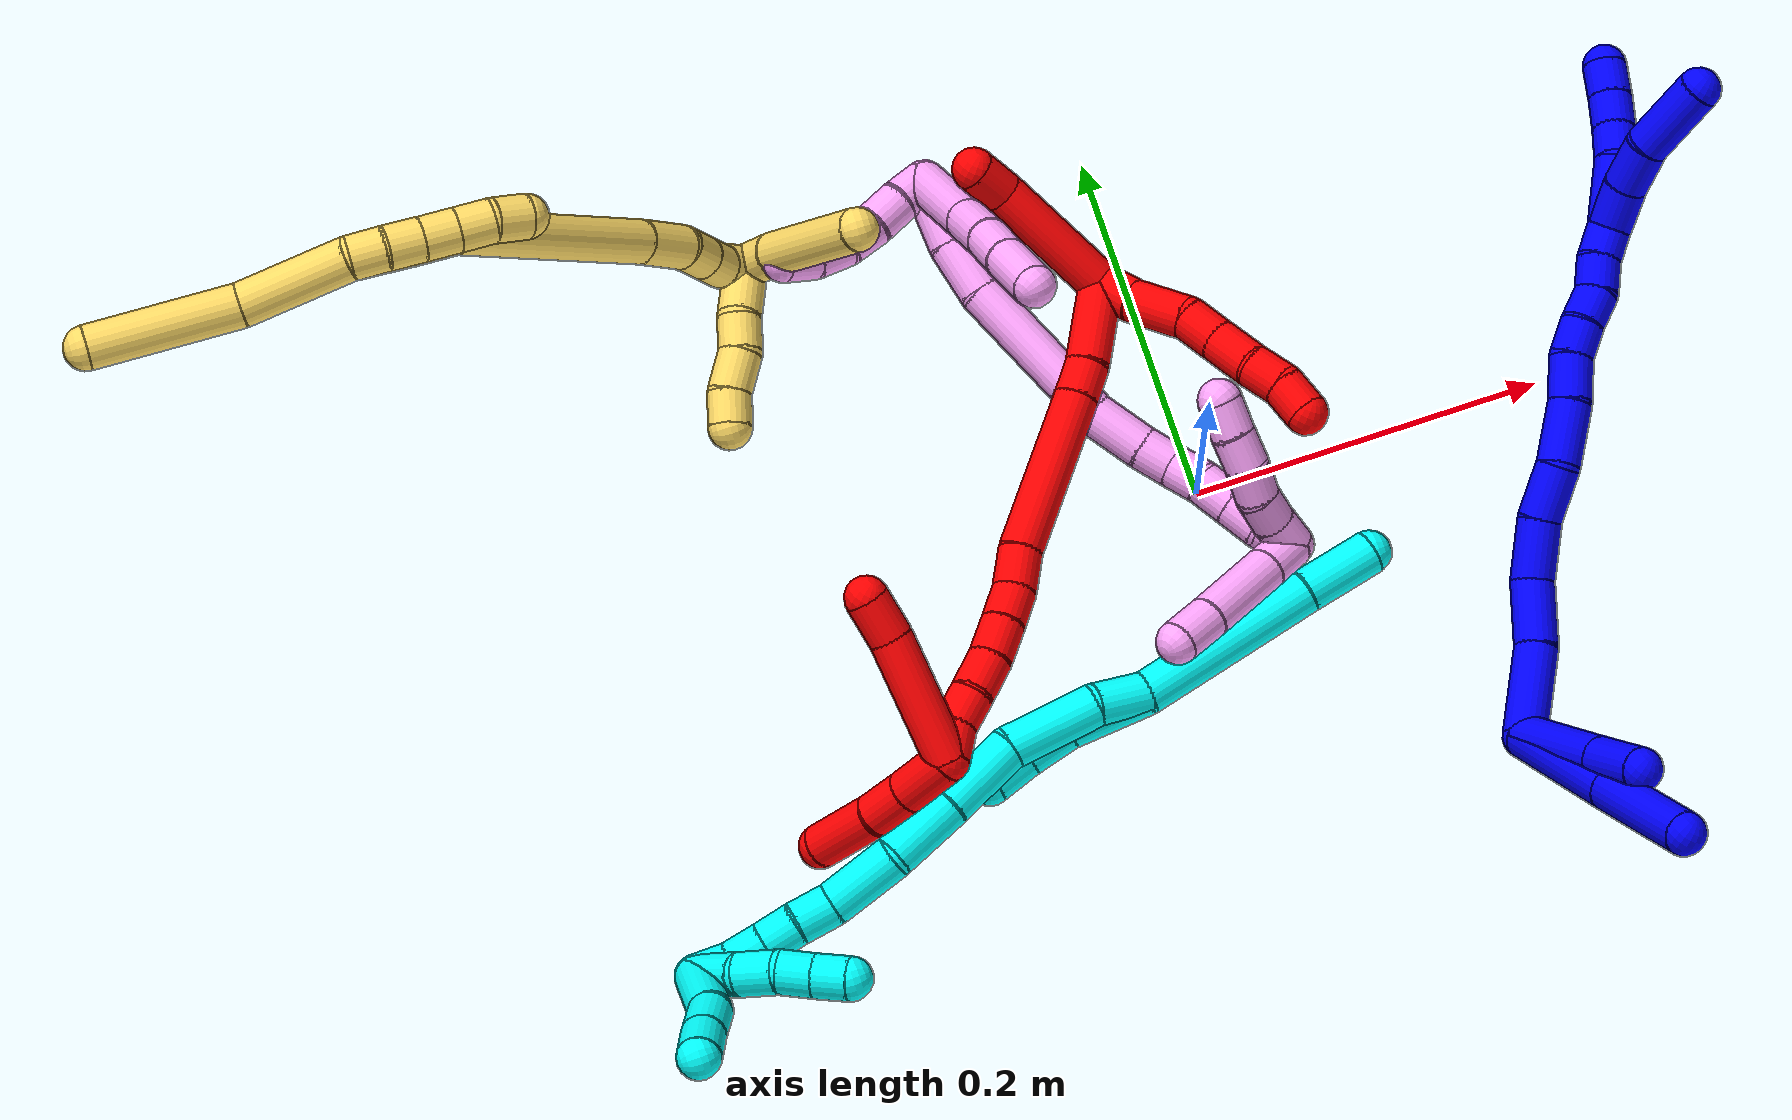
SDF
<sdf version="1.7">
 <world name="default">
  <plugin name="TubeGeneratorPlugin" filename="libtube_generator_plugin.so"/>
  <model name="photoneo_s_sensor">
   <static>1</static>
   <pose>0 0 2 1.57079 1.57079 3.14159</pose>
   <link name="link">
    <inertial><mass>0.1</mass></inertial>
    <sensor name="sensor" type="depth">
     <update_rate>30</update_rate>
     <camera>
      <horizontal_fov>1.22</horizontal_fov>
      <image><width>1920</width><height>1200</height><format>B8G8R8</format></image>
      <clip><near>0.1</near><far>4</far></clip>
      <depth_camera><output>points</output></depth_camera>
     </camera>
     <plugin name="camera_plugin" filename="libgazebo_ros_depth_camera.so">
      <baseline>0.2</baseline>
      <alwaysOn>1</alwaysOn>
      <updateRate>0.0</updateRate>
      <cameraName>camera_ir</cameraName>
      <imageTopicName>/camera/color/image_raw</imageTopicName>
      <cameraInfoTopicName>/camera/color/camera_info</cameraInfoTopicName>
      <depthImageTopicName>/camera/depth/image_raw</depthImageTopicName>
      <depthImageCameraInfoTopicName>/camera/depth/camera_info</depthImageCameraInfoTopicName>
      <pointCloudTopicName>/camera/depth/points</pointCloudTopicName>
      <frameName>fr_optical</frameName>
      <pointCloudCutoff>0.1</pointCloudCutoff>
      <pointCloudCutoffMax>2.0</pointCloudCutoffMax>
      <distortionK1>0</distortionK1>
      <distortionK2>0</distortionK2>
      <distortionK3>0</distortionK3>
      <distortionT1>0</distortionT1>
      <distortionT2>0</distortionT2>
      <CxPrime>0</CxPrime>
      <Cx>0</Cx>
      <Cy>0</Cy>
      <focalLength>0</focalLength>
      <hackBaseline>0</hackBaseline>
     </plugin>
    </sensor>
   </link>
  </model>
  <gravity>0 0 -9.8</gravity>
  <magnetic_field>6e-06 2.3e-05 -4.2e-05</magnetic_field>
  <atmosphere type="adiabatic"/>
  <physics name="default_physics" default="0" type="ode">
   <max_step_size>0.003</max_step_size>
   <real_time_factor>1</real_time_factor>
   <real_time_update_rate>1000</real_time_update_rate>
   <max_contacts>10000</max_contacts>
   <ode>
    <solver>
     <type>quick</type>
     <iters>100</iters>
     <sor>1.3</sor>
     <use_dynamic_moi_rescaling>0</use_dynamic_moi_rescaling>
    </solver>
    <constraints>
     <contact_max_correcting_vel>0</contact_max_correcting_vel>
     <contact_surface_layer>0.001</contact_surface_layer>
     <cfm>0</cfm>
     <erp>0.2</erp>
    </constraints>
   </ode>
  </physics>
  <scene><ambient>0.4 0.4 0.4 1</ambient><background>0.7 0.7 0.7 1</background><shadows>0</shadows></scene>
  <audio><device>default</device></audio>
  <spherical_coordinates>
   <surface_model>EARTH_WGS84</surface_model>
   <latitude_deg>0</latitude_deg>
   <longitude_deg>0</longitude_deg>
   <elevation>0</elevation>
   <heading_deg>0</heading_deg>
  </spherical_coordinates>
  <model name="bin">
   <static>1</static>
   <link name="bottom">
    <collision name="collision-bottom">
     <pose>0 0 -0.01 0 -0 0</pose>
     <geometry><box><size>0.8 0.6 0.02</size></box></geometry>
     <surface>
      <friction><ode><mu>100</mu><mu2>100</mu2></ode></friction>
      <contact><collide_bitmask>65535</collide_bitmask></contact>
     </surface>
    </collision>
   </link>
   <link name="west_wall">
    <collision name="collision-west_wall">
     <pose>-0.41 0 0.1 0 -0 0</pose>
     <geometry><box><size>0.02 0.6 0.2</size></box></geometry>
     <surface>
      <friction><ode><mu>100</mu><mu2>100</mu2></ode></friction>
      <contact><collide_bitmask>65535</collide_bitmask></contact>
     </surface>
    </collision>
   </link>
   <link name="east_wall">
    <collision name="collision-east_wall">
     <pose>0.41 0 0.1 0 -0 0</pose>
     <geometry><box><size>0.02 0.6 0.2</size></box></geometry>
     <surface>
      <friction><ode><mu>100</mu><mu2>100</mu2></ode></friction>
      <contact><collide_bitmask>65535</collide_bitmask></contact>
     </surface>
    </collision>
   </link>
   <link name="south_wall">
    <collision name="collision-south_wall">
     <pose>0 -0.31 0.1 0 -0 0</pose>
     <geometry><box><size>0.8 0.02 0.2</size></box></geometry>
     <surface>
      <friction><ode><mu>100</mu><mu2>100</mu2></ode></friction>
      <contact><collide_bitmask>65535</collide_bitmask></contact>
     </surface>
    </collision>
   </link>
   <link name="north_wall">
    <collision name="collision-north_wall">
     <pose>0 0.31 0.1 0 -0 0</pose>
     <geometry><box><size>0.8 0.02 0.2</size></box></geometry>
     <surface>
      <friction><ode><mu>100</mu><mu2>100</mu2></ode></friction>
      <contact><collide_bitmask>65535</collide_bitmask></contact>
     </surface>
    </collision>
   </link>
  </model>
  <model name="1">
   <static>0</static>
   <link name="1">
    <collision name="collision-cylinder-e_1_2_8">
     <pose>-0.028312 -0.02252 0.015623 0.964288 -0.801622 -0.436466</pose>
     <geometry><cylinder><radius>0.0125</radius><length>0.078811</length></cylinder></geometry>
     <surface>
      <friction><ode><mu>1.16</mu><mu2>1.16</mu2><slip1>0</slip1><slip2>0</slip2></ode></friction>
      <contact><ode><kp>1e+06</kp><kd>1</kd><max_vel>0</max_vel><min_depth>0.001</min_depth></ode></contact>
     </surface>
    </collision>
    <visual name="visual-cylinder-e_1_2_8">
     <pose>-0.028312 -0.02252 0.015623 0.964288 -0.801622 -0.436466</pose>
     <geometry><cylinder><radius>0.0125</radius><length>0.078811</length></cylinder></geometry>
     <material><ambient>0 0 1 1</ambient></material>
    </visual>
    <collision name="collision-cylinder-e_2_8_6">
     <pose>-0.082785 -0.064034 0.046139 0.905836 -0.825586 -0.419986</pose>
     <geometry><cylinder><radius>0.0125</radius><length>0.071189</length></cylinder></geometry>
     <surface>
      <friction><ode><mu>1.16</mu><mu2>1.16</mu2><slip1>0</slip1><slip2>0</slip2></ode></friction>
      <contact><ode><kp>1e+06</kp><kd>1</kd><max_vel>0</max_vel><min_depth>0.001</min_depth></ode></contact>
     </surface>
    </collision>
    <visual name="visual-cylinder-e_2_8_6">
     <pose>-0.082785 -0.064034 0.046139 0.905836 -0.825586 -0.419986</pose>
     <geometry><cylinder><radius>0.0125</radius><length>0.071189</length></cylinder></geometry>
     <material><ambient>0 0 1 1</ambient></material>
    </visual>
    <collision name="collision-cylinder-e_1_2_9">
     <pose>-0.021203 -0.016487 0.018034 0.740618 -0.714716 -0.287908</pose>
     <geometry><cylinder><radius>0.0125</radius><length>0.064703</length></cylinder></geometry>
     <surface>
      <friction><ode><mu>1.16</mu><mu2>1.16</mu2><slip1>0</slip1><slip2>0</slip2></ode></friction>
      <contact><ode><kp>1e+06</kp><kd>1</kd><max_vel>0</max_vel><min_depth>0.001</min_depth></ode></contact>
     </surface>
    </collision>
    <visual name="visual-cylinder-e_1_2_9">
     <pose>-0.021203 -0.016487 0.018034 0.740618 -0.714716 -0.287908</pose>
     <geometry><cylinder><radius>0.0125</radius><length>0.064703</length></cylinder></geometry>
     <material><ambient>0 0 1 1</ambient></material>
    </visual>
    <collision name="collision-cylinder-e_2_9_5">
     <pose>-0.054084 -0.041598 0.046105 0.709823 -0.723028 -0.278462</pose>
     <geometry><cylinder><radius>0.0125</radius><length>0.035297</length></cylinder></geometry>
     <surface>
      <friction><ode><mu>1.16</mu><mu2>1.16</mu2><slip1>0</slip1><slip2>0</slip2></ode></friction>
      <contact><ode><kp>1e+06</kp><kd>1</kd><max_vel>0</max_vel><min_depth>0.001</min_depth></ode></contact>
     </surface>
    </collision>
    <visual name="visual-cylinder-e_2_9_5">
     <pose>-0.054084 -0.041598 0.046105 0.709823 -0.723028 -0.278462</pose>
     <geometry><cylinder><radius>0.0125</radius><length>0.035297</length></cylinder></geometry>
     <material><ambient>0 0 1 1</ambient></material>
    </visual>
    <collision name="collision-cylinder-e_1_2_10">
     <pose>0.018372 0.010208 0.015402 -0.585309 0.782534 -0.247331</pose>
     <geometry><cylinder><radius>0.0125</radius><length>0.052113</length></cylinder></geometry>
     <surface>
      <friction><ode><mu>1.16</mu><mu2>1.16</mu2><slip1>0</slip1><slip2>0</slip2></ode></friction>
      <contact><ode><kp>1e+06</kp><kd>1</kd><max_vel>0</max_vel><min_depth>0.001</min_depth></ode></contact>
     </surface>
    </collision>
    <visual name="visual-cylinder-e_1_2_10">
     <pose>0.018372 0.010208 0.015402 -0.585309 0.782534 -0.247331</pose>
     <geometry><cylinder><radius>0.0125</radius><length>0.052113</length></cylinder></geometry>
     <material><ambient>0 0 1 1</ambient></material>
    </visual>
    <collision name="collision-cylinder-e_2_10_11">
     <pose>0.049372 0.030859 0.040514 -0.821732 0.72477 -0.327387</pose>
     <geometry><cylinder><radius>0.0125</radius><length>0.038096</length></cylinder></geometry>
     <surface>
      <friction><ode><mu>1.16</mu><mu2>1.16</mu2><slip1>0</slip1><slip2>0</slip2></ode></friction>
      <contact><ode><kp>1e+06</kp><kd>1</kd><max_vel>0</max_vel><min_depth>0.001</min_depth></ode></contact>
     </surface>
    </collision>
    <visual name="visual-cylinder-e_2_10_11">
     <pose>0.049372 0.030859 0.040514 -0.821732 0.72477 -0.327387</pose>
     <geometry><cylinder><radius>0.0125</radius><length>0.038096</length></cylinder></geometry>
     <material><ambient>0 0 1 1</ambient></material>
    </visual>
    <collision name="collision-cylinder-e_3_11_12">
     <pose>0.069877 0.049465 0.063495 -0.551435 0.468121 -0.134711</pose>
     <geometry><cylinder><radius>0.0125</radius><length>0.034914</length></cylinder></geometry>
     <surface>
      <friction><ode><mu>1.16</mu><mu2>1.16</mu2><slip1>0</slip1><slip2>0</slip2></ode></friction>
      <contact><ode><kp>1e+06</kp><kd>1</kd><max_vel>0</max_vel><min_depth>0.001</min_depth></ode></contact>
     </surface>
    </collision>
    <visual name="visual-cylinder-e_3_11_12">
     <pose>0.069877 0.049465 0.063495 -0.551435 0.468121 -0.134711</pose>
     <geometry><cylinder><radius>0.0125</radius><length>0.034914</length></cylinder></geometry>
     <material><ambient>0 0 1 1</ambient></material>
    </visual>
    <collision name="collision-cylinder-e_4_12_13">
     <pose>0.083986 0.061998 0.090509 -0.307936 0.407863 -0.064169</pose>
     <geometry><cylinder><radius>0.0125</radius><length>0.031424</length></cylinder></geometry>
     <surface>
      <friction><ode><mu>1.16</mu><mu2>1.16</mu2><slip1>0</slip1><slip2>0</slip2></ode></friction>
      <contact><ode><kp>1e+06</kp><kd>1</kd><max_vel>0</max_vel><min_depth>0.001</min_depth></ode></contact>
     </surface>
    </collision>
    <visual name="visual-cylinder-e_4_12_13">
     <pose>0.083986 0.061998 0.090509 -0.307936 0.407863 -0.064169</pose>
     <geometry><cylinder><radius>0.0125</radius><length>0.031424</length></cylinder></geometry>
     <material><ambient>0 0 1 1</ambient></material>
    </visual>
    <collision name="collision-cylinder-e_5_13_14">
     <pose>0.101276 0.073218 0.116943 -0.49489 0.654251 -0.17102</pose>
     <geometry><cylinder><radius>0.0125</radius><length>0.036341</length></cylinder></geometry>
     <surface>
      <friction><ode><mu>1.16</mu><mu2>1.16</mu2><slip1>0</slip1><slip2>0</slip2></ode></friction>
      <contact><ode><kp>1e+06</kp><kd>1</kd><max_vel>0</max_vel><min_depth>0.001</min_depth></ode></contact>
     </surface>
    </collision>
    <visual name="visual-cylinder-e_5_13_14">
     <pose>0.101276 0.073218 0.116943 -0.49489 0.654251 -0.17102</pose>
     <geometry><cylinder><radius>0.0125</radius><length>0.036341</length></cylinder></geometry>
     <material><ambient>0 0 1 1</ambient></material>
    </visual>
    <collision name="collision-cylinder-e_6_14_15">
     <pose>0.120743 0.086557 0.137237 -0.706511 0.699175 -0.267242</pose>
     <geometry><cylinder><radius>0.0125</radius><length>0.02613</length></cylinder></geometry>
     <surface>
      <friction><ode><mu>1.16</mu><mu2>1.16</mu2><slip1>0</slip1><slip2>0</slip2></ode></friction>
      <contact><ode><kp>1e+06</kp><kd>1</kd><max_vel>0</max_vel><min_depth>0.001</min_depth></ode></contact>
     </surface>
    </collision>
    <visual name="visual-cylinder-e_6_14_15">
     <pose>0.120743 0.086557 0.137237 -0.706511 0.699175 -0.267242</pose>
     <geometry><cylinder><radius>0.0125</radius><length>0.02613</length></cylinder></geometry>
     <material><ambient>0 0 1 1</ambient></material>
    </visual>
    <collision name="collision-cylinder-e_7_15_16">
     <pose>0.135917 0.095504 0.152139 -0.324605 0.721012 -0.123299</pose>
     <geometry><cylinder><radius>0.0125</radius><length>0.020496</length></cylinder></geometry>
     <surface>
      <friction><ode><mu>1.16</mu><mu2>1.16</mu2><slip1>0</slip1><slip2>0</slip2></ode></friction>
      <contact><ode><kp>1e+06</kp><kd>1</kd><max_vel>0</max_vel><min_depth>0.001</min_depth></ode></contact>
     </surface>
    </collision>
    <visual name="visual-cylinder-e_7_15_16">
     <pose>0.135917 0.095504 0.152139 -0.324605 0.721012 -0.123299</pose>
     <geometry><cylinder><radius>0.0125</radius><length>0.020496</length></cylinder></geometry>
     <material><ambient>0 0 1 1</ambient></material>
    </visual>
    <collision name="collision-cylinder-e_8_16_17">
     <pose>0.150294 0.099149 0.166049 -0.17802 0.847483 -0.080469</pose>
     <geometry><cylinder><radius>0.0125</radius><length>0.020309</length></cylinder></geometry>
     <surface>
      <friction><ode><mu>1.16</mu><mu2>1.16</mu2><slip1>0</slip1><slip2>0</slip2></ode></friction>
      <contact><ode><kp>1e+06</kp><kd>1</kd><max_vel>0</max_vel><min_depth>0.001</min_depth></ode></contact>
     </surface>
    </collision>
    <visual name="visual-cylinder-e_8_16_17">
     <pose>0.150294 0.099149 0.166049 -0.17802 0.847483 -0.080469</pose>
     <geometry><cylinder><radius>0.0125</radius><length>0.020309</length></cylinder></geometry>
     <material><ambient>0 0 1 1</ambient></material>
    </visual>
    <collision name="collision-cylinder-e_9_17_18">
     <pose>0.164819 0.104796 0.17849 -0.65302 0.755795 -0.267254</pose>
     <geometry><cylinder><radius>0.0125</radius><length>0.020159</length></cylinder></geometry>
     <surface>
      <friction><ode><mu>1.16</mu><mu2>1.16</mu2><slip1>0</slip1><slip2>0</slip2></ode></friction>
      <contact><ode><kp>1e+06</kp><kd>1</kd><max_vel>0</max_vel><min_depth>0.001</min_depth></ode></contact>
     </surface>
    </collision>
    <visual name="visual-cylinder-e_9_17_18">
     <pose>0.164819 0.104796 0.17849 -0.65302 0.755795 -0.267254</pose>
     <geometry><cylinder><radius>0.0125</radius><length>0.020159</length></cylinder></geometry>
     <material><ambient>0 0 1 1</ambient></material>
    </visual>
    <collision name="collision-cylinder-e_10_18_1">
     <pose>0.178744 0.111599 0.191061 -0.334719 0.776246 -0.137927</pose>
     <geometry><cylinder><radius>0.0125</radius><length>0.020017</length></cylinder></geometry>
     <surface>
      <friction><ode><mu>1.16</mu><mu2>1.16</mu2><slip1>0</slip1><slip2>0</slip2></ode></friction>
      <contact><ode><kp>1e+06</kp><kd>1</kd><max_vel>0</max_vel><min_depth>0.001</min_depth></ode></contact>
     </surface>
    </collision>
    <visual name="visual-cylinder-e_10_18_1">
     <pose>0.178744 0.111599 0.191061 -0.334719 0.776246 -0.137927</pose>
     <geometry><cylinder><radius>0.0125</radius><length>0.020017</length></cylinder></geometry>
     <material><ambient>0 0 1 1</ambient></material>
    </visual>
    <collision name="collision-cylinder-e_1_1_19">
     <pose>0.198618 0.122484 0.210267 -0.600805 0.705332 -0.227048</pose>
     <geometry><cylinder><radius>0.0125</radius><length>0.039679</length></cylinder></geometry>
     <surface>
      <friction><ode><mu>1.16</mu><mu2>1.16</mu2><slip1>0</slip1><slip2>0</slip2></ode></friction>
      <contact><ode><kp>1e+06</kp><kd>1</kd><max_vel>0</max_vel><min_depth>0.001</min_depth></ode></contact>
     </surface>
    </collision>
    <visual name="visual-cylinder-e_1_1_19">
     <pose>0.198618 0.122484 0.210267 -0.600805 0.705332 -0.227048</pose>
     <geometry><cylinder><radius>0.0125</radius><length>0.039679</length></cylinder></geometry>
     <material><ambient>0 0 1 1</ambient></material>
    </visual>
    <collision name="collision-cylinder-e_2_19_20">
     <pose>0.219473 0.135772 0.226431 -0.908417 0.925155 -0.477657</pose>
     <geometry><cylinder><radius>0.0125</radius><length>0.020016</length></cylinder></geometry>
     <surface>
      <friction><ode><mu>1.16</mu><mu2>1.16</mu2><slip1>0</slip1><slip2>0</slip2></ode></friction>
      <contact><ode><kp>1e+06</kp><kd>1</kd><max_vel>0</max_vel><min_depth>0.001</min_depth></ode></contact>
     </surface>
    </collision>
    <visual name="visual-cylinder-e_2_19_20">
     <pose>0.219473 0.135772 0.226431 -0.908417 0.925155 -0.477657</pose>
     <geometry><cylinder><radius>0.0125</radius><length>0.020016</length></cylinder></geometry>
     <material><ambient>0 0 1 1</ambient></material>
    </visual>
    <collision name="collision-cylinder-e_3_20_21">
     <pose>0.234685 0.146109 0.234338 -0.925874 0.801265 -0.416653</pose>
     <geometry><cylinder><radius>0.0125</radius><length>0.020102</length></cylinder></geometry>
     <surface>
      <friction><ode><mu>1.16</mu><mu2>1.16</mu2><slip1>0</slip1><slip2>0</slip2></ode></friction>
      <contact><ode><kp>1e+06</kp><kd>1</kd><max_vel>0</max_vel><min_depth>0.001</min_depth></ode></contact>
     </surface>
    </collision>
    <visual name="visual-cylinder-e_3_20_21">
     <pose>0.234685 0.146109 0.234338 -0.925874 0.801265 -0.416653</pose>
     <geometry><cylinder><radius>0.0125</radius><length>0.020102</length></cylinder></geometry>
     <material><ambient>0 0 1 1</ambient></material>
    </visual>
    <collision name="collision-cylinder-e_4_21_4">
     <pose>0.248937 0.157719 0.242585 -0.979493 0.770037 -0.425502</pose>
     <geometry><cylinder><radius>0.0125</radius><length>0.020203</length></cylinder></geometry>
     <surface>
      <friction><ode><mu>1.16</mu><mu2>1.16</mu2><slip1>0</slip1><slip2>0</slip2></ode></friction>
      <contact><ode><kp>1e+06</kp><kd>1</kd><max_vel>0</max_vel><min_depth>0.001</min_depth></ode></contact>
     </surface>
    </collision>
    <visual name="visual-cylinder-e_4_21_4">
     <pose>0.248937 0.157719 0.242585 -0.979493 0.770037 -0.425502</pose>
     <geometry><cylinder><radius>0.0125</radius><length>0.020203</length></cylinder></geometry>
     <material><ambient>0 0 1 1</ambient></material>
    </visual>
    <collision name="collision-cylinder-e_1_1_22">
     <pose>0.186724 0.11761 0.210725 -0.276477 0.07194 -0.010013</pose>
     <geometry><cylinder><radius>0.0125</radius><length>0.026926</length></cylinder></geometry>
     <surface>
      <friction><ode><mu>1.16</mu><mu2>1.16</mu2><slip1>0</slip1><slip2>0</slip2></ode></friction>
      <contact><ode><kp>1e+06</kp><kd>1</kd><max_vel>0</max_vel><min_depth>0.001</min_depth></ode></contact>
     </surface>
    </collision>
    <visual name="visual-cylinder-e_1_1_22">
     <pose>0.186724 0.11761 0.210725 -0.276477 0.07194 -0.010013</pose>
     <geometry><cylinder><radius>0.0125</radius><length>0.026926</length></cylinder></geometry>
     <material><ambient>0 0 1 1</ambient></material>
    </visual>
    <collision name="collision-cylinder-e_2_22_23">
     <pose>0.187022 0.123495 0.237296 -0.161113 -0.048368 0.003906</pose>
     <geometry><cylinder><radius>0.0125</radius><length>0.027697</length></cylinder></geometry>
     <surface>
      <friction><ode><mu>1.16</mu><mu2>1.16</mu2><slip1>0</slip1><slip2>0</slip2></ode></friction>
      <contact><ode><kp>1e+06</kp><kd>1</kd><max_vel>0</max_vel><min_depth>0.001</min_depth></ode></contact>
     </surface>
    </collision>
    <visual name="visual-cylinder-e_2_22_23">
     <pose>0.187022 0.123495 0.237296 -0.161113 -0.048368 0.003906</pose>
     <geometry><cylinder><radius>0.0125</radius><length>0.027697</length></cylinder></geometry>
     <material><ambient>0 0 1 1</ambient></material>
    </visual>
    <collision name="collision-cylinder-e_3_23_3">
     <pose>0.186526 0.123926 0.273566 0.078864 0.007676 0.000303</pose>
     <geometry><cylinder><radius>0.0125</radius><length>0.045377</length></cylinder></geometry>
     <surface>
      <friction><ode><mu>1.16</mu><mu2>1.16</mu2><slip1>0</slip1><slip2>0</slip2></ode></friction>
      <contact><ode><kp>1e+06</kp><kd>1</kd><max_vel>0</max_vel><min_depth>0.001</min_depth></ode></contact>
     </surface>
    </collision>
    <visual name="visual-cylinder-e_3_23_3">
     <pose>0.186526 0.123926 0.273566 0.078864 0.007676 0.000303</pose>
     <geometry><cylinder><radius>0.0125</radius><length>0.045377</length></cylinder></geometry>
     <material><ambient>0 0 1 1</ambient></material>
    </visual>
    <collision name="collision-sphere-3">
     <pose>0.186701 0.122139 0.296184 0 -0 0</pose>
     <geometry><sphere><radius>0.0125</radius></sphere></geometry>
     <surface>
      <friction><ode><mu>1.16</mu><mu2>1.16</mu2><slip1>0</slip1><slip2>0</slip2></ode></friction>
      <contact><ode><kp>1e+06</kp><kd>1</kd><max_vel>0</max_vel><min_depth>0.001</min_depth></ode></contact>
     </surface>
    </collision>
    <visual name="visual-sphere-3">
     <pose>0.186701 0.122139 0.296184 0 -0 0</pose>
     <geometry><sphere><radius>0.0125</radius></sphere></geometry>
     <material><ambient>0 0 1 1</ambient></material>
    </visual>
    <collision name="collision-sphere-23">
     <pose>0.186352 0.125714 0.250949 0 -0 0</pose>
     <geometry><sphere><radius>0.0125</radius></sphere></geometry>
     <surface>
      <friction><ode><mu>1.16</mu><mu2>1.16</mu2><slip1>0</slip1><slip2>0</slip2></ode></friction>
      <contact><ode><kp>1e+06</kp><kd>1</kd><max_vel>0</max_vel><min_depth>0.001</min_depth></ode></contact>
     </surface>
    </collision>
    <visual name="visual-sphere-23">
     <pose>0.186352 0.125714 0.250949 0 -0 0</pose>
     <geometry><sphere><radius>0.0125</radius></sphere></geometry>
     <material><ambient>0 0 1 1</ambient></material>
    </visual>
    <collision name="collision-sphere-22">
     <pose>0.187691 0.121276 0.223643 0 -0 0</pose>
     <geometry><sphere><radius>0.0125</radius></sphere></geometry>
     <surface>
      <friction><ode><mu>1.16</mu><mu2>1.16</mu2><slip1>0</slip1><slip2>0</slip2></ode></friction>
      <contact><ode><kp>1e+06</kp><kd>1</kd><max_vel>0</max_vel><min_depth>0.001</min_depth></ode></contact>
     </surface>
    </collision>
    <visual name="visual-sphere-22">
     <pose>0.187691 0.121276 0.223643 0 -0 0</pose>
     <geometry><sphere><radius>0.0125</radius></sphere></geometry>
     <material><ambient>0 0 1 1</ambient></material>
    </visual>
    <collision name="collision-sphere-4">
     <pose>0.255969 0.163739 0.246627 0 -0 0</pose>
     <geometry><sphere><radius>0.0125</radius></sphere></geometry>
     <surface>
      <friction><ode><mu>1.16</mu><mu2>1.16</mu2><slip1>0</slip1><slip2>0</slip2></ode></friction>
      <contact><ode><kp>1e+06</kp><kd>1</kd><max_vel>0</max_vel><min_depth>0.001</min_depth></ode></contact>
     </surface>
    </collision>
    <visual name="visual-sphere-4">
     <pose>0.255969 0.163739 0.246627 0 -0 0</pose>
     <geometry><sphere><radius>0.0125</radius></sphere></geometry>
     <material><ambient>0 0 1 1</ambient></material>
    </visual>
    <collision name="collision-sphere-21">
     <pose>0.241905 0.151698 0.238542 0 -0 0</pose>
     <geometry><sphere><radius>0.0125</radius></sphere></geometry>
     <surface>
      <friction><ode><mu>1.16</mu><mu2>1.16</mu2><slip1>0</slip1><slip2>0</slip2></ode></friction>
      <contact><ode><kp>1e+06</kp><kd>1</kd><max_vel>0</max_vel><min_depth>0.001</min_depth></ode></contact>
     </surface>
    </collision>
    <visual name="visual-sphere-21">
     <pose>0.241905 0.151698 0.238542 0 -0 0</pose>
     <geometry><sphere><radius>0.0125</radius></sphere></geometry>
     <material><ambient>0 0 1 1</ambient></material>
    </visual>
    <collision name="collision-sphere-20">
     <pose>0.227466 0.14052 0.230134 0 -0 0</pose>
     <geometry><sphere><radius>0.0125</radius></sphere></geometry>
     <surface>
      <friction><ode><mu>1.16</mu><mu2>1.16</mu2><slip1>0</slip1><slip2>0</slip2></ode></friction>
      <contact><ode><kp>1e+06</kp><kd>1</kd><max_vel>0</max_vel><min_depth>0.001</min_depth></ode></contact>
     </surface>
    </collision>
    <visual name="visual-sphere-20">
     <pose>0.227466 0.14052 0.230134 0 -0 0</pose>
     <geometry><sphere><radius>0.0125</radius></sphere></geometry>
     <material><ambient>0 0 1 1</ambient></material>
    </visual>
    <collision name="collision-sphere-10">
     <pose>0.036744 0.020416 0.030803 0 -0 0</pose>
     <geometry><sphere><radius>0.0125</radius></sphere></geometry>
     <surface>
      <friction><ode><mu>1.16</mu><mu2>1.16</mu2><slip1>0</slip1><slip2>0</slip2></ode></friction>
      <contact><ode><kp>1e+06</kp><kd>1</kd><max_vel>0</max_vel><min_depth>0.001</min_depth></ode></contact>
     </surface>
    </collision>
    <visual name="visual-sphere-10">
     <pose>0.036744 0.020416 0.030803 0 -0 0</pose>
     <geometry><sphere><radius>0.0125</radius></sphere></geometry>
     <material><ambient>0 0 1 1</ambient></material>
    </visual>
    <collision name="collision-sphere-5">
     <pose>-0.065761 -0.050222 0.056141 0 -0 0</pose>
     <geometry><sphere><radius>0.0125</radius></sphere></geometry>
     <surface>
      <friction><ode><mu>1.16</mu><mu2>1.16</mu2><slip1>0</slip1><slip2>0</slip2></ode></friction>
      <contact><ode><kp>1e+06</kp><kd>1</kd><max_vel>0</max_vel><min_depth>0.001</min_depth></ode></contact>
     </surface>
    </collision>
    <visual name="visual-sphere-5">
     <pose>-0.065761 -0.050222 0.056141 0 -0 0</pose>
     <geometry><sphere><radius>0.0125</radius></sphere></geometry>
     <material><ambient>0 0 1 1</ambient></material>
    </visual>
    <collision name="collision-sphere-6">
     <pose>-0.108945 -0.083029 0.061033 0 -0 0</pose>
     <geometry><sphere><radius>0.0125</radius></sphere></geometry>
     <surface>
      <friction><ode><mu>1.16</mu><mu2>1.16</mu2><slip1>0</slip1><slip2>0</slip2></ode></friction>
      <contact><ode><kp>1e+06</kp><kd>1</kd><max_vel>0</max_vel><min_depth>0.001</min_depth></ode></contact>
     </surface>
    </collision>
    <visual name="visual-sphere-6">
     <pose>-0.108945 -0.083029 0.061033 0 -0 0</pose>
     <geometry><sphere><radius>0.0125</radius></sphere></geometry>
     <material><ambient>0 0 1 1</ambient></material>
    </visual>
    <collision name="collision-sphere-9">
     <pose>-0.042407 -0.032974 0.036068 0 -0 0</pose>
     <geometry><sphere><radius>0.0125</radius></sphere></geometry>
     <surface>
      <friction><ode><mu>1.16</mu><mu2>1.16</mu2><slip1>0</slip1><slip2>0</slip2></ode></friction>
      <contact><ode><kp>1e+06</kp><kd>1</kd><max_vel>0</max_vel><min_depth>0.001</min_depth></ode></contact>
     </surface>
    </collision>
    <visual name="visual-sphere-9">
     <pose>-0.042407 -0.032974 0.036068 0 -0 0</pose>
     <geometry><sphere><radius>0.0125</radius></sphere></geometry>
     <material><ambient>0 0 1 1</ambient></material>
    </visual>
    <collision name="collision-sphere-2">
     <geometry><sphere><radius>0.0125</radius></sphere></geometry>
     <surface>
      <friction><ode><mu>1.16</mu><mu2>1.16</mu2><slip1>0</slip1><slip2>0</slip2></ode></friction>
      <contact><ode><kp>1e+06</kp><kd>1</kd><max_vel>0</max_vel><min_depth>0.001</min_depth></ode></contact>
     </surface>
    </collision>
    <visual name="visual-sphere-2">
     <geometry><sphere><radius>0.0125</radius></sphere></geometry>
     <material><ambient>0 0 1 1</ambient></material>
    </visual>
    <collision name="collision-sphere-19">
     <pose>0.211479 0.131024 0.222727 0 -0 0</pose>
     <geometry><sphere><radius>0.0125</radius></sphere></geometry>
     <surface>
      <friction><ode><mu>1.16</mu><mu2>1.16</mu2><slip1>0</slip1><slip2>0</slip2></ode></friction>
      <contact><ode><kp>1e+06</kp><kd>1</kd><max_vel>0</max_vel><min_depth>0.001</min_depth></ode></contact>
     </surface>
    </collision>
    <visual name="visual-sphere-19">
     <pose>0.211479 0.131024 0.222727 0 -0 0</pose>
     <geometry><sphere><radius>0.0125</radius></sphere></geometry>
     <material><ambient>0 0 1 1</ambient></material>
    </visual>
    <collision name="collision-sphere-8">
     <pose>-0.056625 -0.04504 0.031245 0 -0 0</pose>
     <geometry><sphere><radius>0.0125</radius></sphere></geometry>
     <surface>
      <friction><ode><mu>1.16</mu><mu2>1.16</mu2><slip1>0</slip1><slip2>0</slip2></ode></friction>
      <contact><ode><kp>1e+06</kp><kd>1</kd><max_vel>0</max_vel><min_depth>0.001</min_depth></ode></contact>
     </surface>
    </collision>
    <visual name="visual-sphere-8">
     <pose>-0.056625 -0.04504 0.031245 0 -0 0</pose>
     <geometry><sphere><radius>0.0125</radius></sphere></geometry>
     <material><ambient>0 0 1 1</ambient></material>
    </visual>
    <collision name="collision-sphere-11">
     <pose>0.062 0.041303 0.050225 0 -0 0</pose>
     <geometry><sphere><radius>0.0125</radius></sphere></geometry>
     <surface>
      <friction><ode><mu>1.16</mu><mu2>1.16</mu2><slip1>0</slip1><slip2>0</slip2></ode></friction>
      <contact><ode><kp>1e+06</kp><kd>1</kd><max_vel>0</max_vel><min_depth>0.001</min_depth></ode></contact>
     </surface>
    </collision>
    <visual name="visual-sphere-11">
     <pose>0.062 0.041303 0.050225 0 -0 0</pose>
     <geometry><sphere><radius>0.0125</radius></sphere></geometry>
     <material><ambient>0 0 1 1</ambient></material>
    </visual>
    <collision name="collision-sphere-12">
     <pose>0.077754 0.057627 0.076764 0 -0 0</pose>
     <geometry><sphere><radius>0.0125</radius></sphere></geometry>
     <surface>
      <friction><ode><mu>1.16</mu><mu2>1.16</mu2><slip1>0</slip1><slip2>0</slip2></ode></friction>
      <contact><ode><kp>1e+06</kp><kd>1</kd><max_vel>0</max_vel><min_depth>0.001</min_depth></ode></contact>
     </surface>
    </collision>
    <visual name="visual-sphere-12">
     <pose>0.077754 0.057627 0.076764 0 -0 0</pose>
     <geometry><sphere><radius>0.0125</radius></sphere></geometry>
     <material><ambient>0 0 1 1</ambient></material>
    </visual>
    <collision name="collision-sphere-13">
     <pose>0.090218 0.06637 0.104254 0 -0 0</pose>
     <geometry><sphere><radius>0.0125</radius></sphere></geometry>
     <surface>
      <friction><ode><mu>1.16</mu><mu2>1.16</mu2><slip1>0</slip1><slip2>0</slip2></ode></friction>
      <contact><ode><kp>1e+06</kp><kd>1</kd><max_vel>0</max_vel><min_depth>0.001</min_depth></ode></contact>
     </surface>
    </collision>
    <visual name="visual-sphere-13">
     <pose>0.090218 0.06637 0.104254 0 -0 0</pose>
     <geometry><sphere><radius>0.0125</radius></sphere></geometry>
     <material><ambient>0 0 1 1</ambient></material>
    </visual>
    <collision name="collision-sphere-14">
     <pose>0.112334 0.080065 0.129631 0 -0 0</pose>
     <geometry><sphere><radius>0.0125</radius></sphere></geometry>
     <surface>
      <friction><ode><mu>1.16</mu><mu2>1.16</mu2><slip1>0</slip1><slip2>0</slip2></ode></friction>
      <contact><ode><kp>1e+06</kp><kd>1</kd><max_vel>0</max_vel><min_depth>0.001</min_depth></ode></contact>
     </surface>
    </collision>
    <visual name="visual-sphere-14">
     <pose>0.112334 0.080065 0.129631 0 -0 0</pose>
     <geometry><sphere><radius>0.0125</radius></sphere></geometry>
     <material><ambient>0 0 1 1</ambient></material>
    </visual>
    <collision name="collision-sphere-15">
     <pose>0.129151 0.093049 0.144843 0 -0 0</pose>
     <geometry><sphere><radius>0.0125</radius></sphere></geometry>
     <surface>
      <friction><ode><mu>1.16</mu><mu2>1.16</mu2><slip1>0</slip1><slip2>0</slip2></ode></friction>
      <contact><ode><kp>1e+06</kp><kd>1</kd><max_vel>0</max_vel><min_depth>0.001</min_depth></ode></contact>
     </surface>
    </collision>
    <visual name="visual-sphere-15">
     <pose>0.129151 0.093049 0.144843 0 -0 0</pose>
     <geometry><sphere><radius>0.0125</radius></sphere></geometry>
     <material><ambient>0 0 1 1</ambient></material>
    </visual>
    <collision name="collision-sphere-16">
     <pose>0.142682 0.097959 0.159435 0 -0 0</pose>
     <geometry><sphere><radius>0.0125</radius></sphere></geometry>
     <surface>
      <friction><ode><mu>1.16</mu><mu2>1.16</mu2><slip1>0</slip1><slip2>0</slip2></ode></friction>
      <contact><ode><kp>1e+06</kp><kd>1</kd><max_vel>0</max_vel><min_depth>0.001</min_depth></ode></contact>
     </surface>
    </collision>
    <visual name="visual-sphere-16">
     <pose>0.142682 0.097959 0.159435 0 -0 0</pose>
     <geometry><sphere><radius>0.0125</radius></sphere></geometry>
     <material><ambient>0 0 1 1</ambient></material>
    </visual>
    <collision name="collision-sphere-17">
     <pose>0.157906 0.100339 0.172664 0 -0 0</pose>
     <geometry><sphere><radius>0.0125</radius></sphere></geometry>
     <surface>
      <friction><ode><mu>1.16</mu><mu2>1.16</mu2><slip1>0</slip1><slip2>0</slip2></ode></friction>
      <contact><ode><kp>1e+06</kp><kd>1</kd><max_vel>0</max_vel><min_depth>0.001</min_depth></ode></contact>
     </surface>
    </collision>
    <visual name="visual-sphere-17">
     <pose>0.157906 0.100339 0.172664 0 -0 0</pose>
     <geometry><sphere><radius>0.0125</radius></sphere></geometry>
     <material><ambient>0 0 1 1</ambient></material>
    </visual>
    <collision name="collision-sphere-18">
     <pose>0.171732 0.109253 0.184316 0 -0 0</pose>
     <geometry><sphere><radius>0.0125</radius></sphere></geometry>
     <surface>
      <friction><ode><mu>1.16</mu><mu2>1.16</mu2><slip1>0</slip1><slip2>0</slip2></ode></friction>
      <contact><ode><kp>1e+06</kp><kd>1</kd><max_vel>0</max_vel><min_depth>0.001</min_depth></ode></contact>
     </surface>
    </collision>
    <visual name="visual-sphere-18">
     <pose>0.171732 0.109253 0.184316 0 -0 0</pose>
     <geometry><sphere><radius>0.0125</radius></sphere></geometry>
     <material><ambient>0 0 1 1</ambient></material>
    </visual>
    <collision name="collision-sphere-1">
     <pose>0.185756 0.113945 0.197806 0 -0 0</pose>
     <geometry><sphere><radius>0.0125</radius></sphere></geometry>
     <surface>
      <friction><ode><mu>1.16</mu><mu2>1.16</mu2><slip1>0</slip1><slip2>0</slip2></ode></friction>
      <contact><ode><kp>1e+06</kp><kd>1</kd><max_vel>0</max_vel><min_depth>0.001</min_depth></ode></contact>
     </surface>
    </collision>
    <visual name="visual-sphere-1">
     <pose>0.185756 0.113945 0.197806 0 -0 0</pose>
     <geometry><sphere><radius>0.0125</radius></sphere></geometry>
     <material><ambient>0 0 1 1</ambient></material>
    </visual>
    <inertial>
     <pose>0.075704 0.047555 0.111484 0 -0 0</pose>
     <mass>0.75</mass>
     <inertia>
      <ixx>9.4e-05</ixx>
      <ixy>0</ixy>
      <ixz>0</ixz>
      <iyy>0.000113</iyy>
      <iyz>0</iyz>
      <izz>0.000112</izz>
     </inertia>
    </inertial>
   </link>
   <pose>0.124062 -0.191846 0.020022 0.313015 0.861526 0.908189</pose>
  </model>
  <model name="2">
   <static>0</static>
   <link name="2">
    <collision name="collision-cylinder-e_1_2_8">
     <pose>0.006027 -0.009273 -0.002185 1.80219 0.564032 0.701603</pose>
     <geometry><cylinder><radius>0.0125</radius><length>0.022547</length></cylinder></geometry>
     <surface>
      <friction><ode><mu>1.16</mu><mu2>1.16</mu2><slip1>0</slip1><slip2>0</slip2></ode></friction>
      <contact><ode><kp>1e+06</kp><kd>1</kd><max_vel>0</max_vel><min_depth>0.001</min_depth></ode></contact>
     </surface>
    </collision>
    <visual name="visual-cylinder-e_1_2_8">
     <pose>0.006027 -0.009273 -0.002185 1.80219 0.564032 0.701603</pose>
     <geometry><cylinder><radius>0.0125</radius><length>0.022547</length></cylinder></geometry>
     <material><ambient>1 0 0 1</ambient></material>
    </visual>
    <collision name="collision-cylinder-e_2_8_9">
     <pose>0.021125 -0.032661 -0.010888 2.00341 0.528213 0.799918</pose>
     <geometry><cylinder><radius>0.0125</radius><length>0.035999</length></cylinder></geometry>
     <surface>
      <friction><ode><mu>1.16</mu><mu2>1.16</mu2><slip1>0</slip1><slip2>0</slip2></ode></friction>
      <contact><ode><kp>1e+06</kp><kd>1</kd><max_vel>0</max_vel><min_depth>0.001</min_depth></ode></contact>
     </surface>
    </collision>
    <visual name="visual-cylinder-e_2_8_9">
     <pose>0.021125 -0.032661 -0.010888 2.00341 0.528213 0.799918</pose>
     <geometry><cylinder><radius>0.0125</radius><length>0.035999</length></cylinder></geometry>
     <material><ambient>1 0 0 1</ambient></material>
    </visual>
    <collision name="collision-cylinder-e_3_9_10">
     <pose>0.036575 -0.056117 -0.017904 1.62413 0.598414 0.629138</pose>
     <geometry><cylinder><radius>0.0125</radius><length>0.022645</length></cylinder></geometry>
     <surface>
      <friction><ode><mu>1.16</mu><mu2>1.16</mu2><slip1>0</slip1><slip2>0</slip2></ode></friction>
      <contact><ode><kp>1e+06</kp><kd>1</kd><max_vel>0</max_vel><min_depth>0.001</min_depth></ode></contact>
     </surface>
    </collision>
    <visual name="visual-cylinder-e_3_9_10">
     <pose>0.036575 -0.056117 -0.017904 1.62413 0.598414 0.629138</pose>
     <geometry><cylinder><radius>0.0125</radius><length>0.022645</length></cylinder></geometry>
     <material><ambient>1 0 0 1</ambient></material>
    </visual>
    <collision name="collision-cylinder-e_4_10_11">
     <pose>0.052124 -0.075251 -0.020342 1.76628 0.743038 0.885792</pose>
     <geometry><cylinder><radius>0.0125</radius><length>0.027112</length></cylinder></geometry>
     <surface>
      <friction><ode><mu>1.16</mu><mu2>1.16</mu2><slip1>0</slip1><slip2>0</slip2></ode></friction>
      <contact><ode><kp>1e+06</kp><kd>1</kd><max_vel>0</max_vel><min_depth>0.001</min_depth></ode></contact>
     </surface>
    </collision>
    <visual name="visual-cylinder-e_4_10_11">
     <pose>0.052124 -0.075251 -0.020342 1.76628 0.743038 0.885792</pose>
     <geometry><cylinder><radius>0.0125</radius><length>0.027112</length></cylinder></geometry>
     <material><ambient>1 0 0 1</ambient></material>
    </visual>
    <collision name="collision-cylinder-e_5_11_12">
     <pose>0.066941 -0.093852 -0.023356 1.69228 0.566674 0.635472</pose>
     <geometry><cylinder><radius>0.0125</radius><length>0.021036</length></cylinder></geometry>
     <surface>
      <friction><ode><mu>1.16</mu><mu2>1.16</mu2><slip1>0</slip1><slip2>0</slip2></ode></friction>
      <contact><ode><kp>1e+06</kp><kd>1</kd><max_vel>0</max_vel><min_depth>0.001</min_depth></ode></contact>
     </surface>
    </collision>
    <visual name="visual-cylinder-e_5_11_12">
     <pose>0.066941 -0.093852 -0.023356 1.69228 0.566674 0.635472</pose>
     <geometry><cylinder><radius>0.0125</radius><length>0.021036</length></cylinder></geometry>
     <material><ambient>1 0 0 1</ambient></material>
    </visual>
    <collision name="collision-cylinder-e_6_12_6">
     <pose>0.079025 -0.110566 -0.022761 1.36258 0.672671 0.552444</pose>
     <geometry><cylinder><radius>0.0125</radius><length>0.020661</length></cylinder></geometry>
     <surface>
      <friction><ode><mu>1.16</mu><mu2>1.16</mu2><slip1>0</slip1><slip2>0</slip2></ode></friction>
      <contact><ode><kp>1e+06</kp><kd>1</kd><max_vel>0</max_vel><min_depth>0.001</min_depth></ode></contact>
     </surface>
    </collision>
    <visual name="visual-cylinder-e_6_12_6">
     <pose>0.079025 -0.110566 -0.022761 1.36258 0.672671 0.552444</pose>
     <geometry><cylinder><radius>0.0125</radius><length>0.020661</length></cylinder></geometry>
     <material><ambient>1 0 0 1</ambient></material>
    </visual>
    <collision name="collision-cylinder-e_1_2_13">
     <pose>-0.004127 0.035588 -0.013418 -1.93134 -0.108081 0.156092</pose>
     <geometry><cylinder><radius>0.0125</radius><length>0.076514</length></cylinder></geometry>
     <surface>
      <friction><ode><mu>1.16</mu><mu2>1.16</mu2><slip1>0</slip1><slip2>0</slip2></ode></friction>
      <contact><ode><kp>1e+06</kp><kd>1</kd><max_vel>0</max_vel><min_depth>0.001</min_depth></ode></contact>
     </surface>
    </collision>
    <visual name="visual-cylinder-e_1_2_13">
     <pose>-0.004127 0.035588 -0.013418 -1.93134 -0.108081 0.156092</pose>
     <geometry><cylinder><radius>0.0125</radius><length>0.076514</length></cylinder></geometry>
     <material><ambient>1 0 0 1</ambient></material>
    </visual>
    <collision name="collision-cylinder-e_2_13_5">
     <pose>-0.005956 0.0816 -0.031732 -2.00996 0.196928 -0.308618</pose>
     <geometry><cylinder><radius>0.0125</radius><length>0.023486</length></cylinder></geometry>
     <surface>
      <friction><ode><mu>1.16</mu><mu2>1.16</mu2><slip1>0</slip1><slip2>0</slip2></ode></friction>
      <contact><ode><kp>1e+06</kp><kd>1</kd><max_vel>0</max_vel><min_depth>0.001</min_depth></ode></contact>
     </surface>
    </collision>
    <visual name="visual-cylinder-e_2_13_5">
     <pose>-0.005956 0.0816 -0.031732 -2.00996 0.196928 -0.308618</pose>
     <geometry><cylinder><radius>0.0125</radius><length>0.023486</length></cylinder></geometry>
     <material><ambient>1 0 0 1</ambient></material>
    </visual>
    <collision name="collision-cylinder-e_1_2_14">
     <pose>0.020476 -0.00294 0.013821 0.209629 0.96675 0.110329</pose>
     <geometry><cylinder><radius>0.0125</radius><length>0.049757</length></cylinder></geometry>
     <surface>
      <friction><ode><mu>1.16</mu><mu2>1.16</mu2><slip1>0</slip1><slip2>0</slip2></ode></friction>
      <contact><ode><kp>1e+06</kp><kd>1</kd><max_vel>0</max_vel><min_depth>0.001</min_depth></ode></contact>
     </surface>
    </collision>
    <visual name="visual-cylinder-e_1_2_14">
     <pose>0.020476 -0.00294 0.013821 0.209629 0.96675 0.110329</pose>
     <geometry><cylinder><radius>0.0125</radius><length>0.049757</length></cylinder></geometry>
     <material><ambient>1 0 0 1</ambient></material>
    </visual>
    <collision name="collision-cylinder-e_2_14_15">
     <pose>0.048908 -0.005764 0.034232 -0.017764 0.878896 -0.008351</pose>
     <geometry><cylinder><radius>0.0125</radius><length>0.020663</length></cylinder></geometry>
     <surface>
      <friction><ode><mu>1.16</mu><mu2>1.16</mu2><slip1>0</slip1><slip2>0</slip2></ode></friction>
      <contact><ode><kp>1e+06</kp><kd>1</kd><max_vel>0</max_vel><min_depth>0.001</min_depth></ode></contact>
     </surface>
    </collision>
    <visual name="visual-cylinder-e_2_14_15">
     <pose>0.048908 -0.005764 0.034232 -0.017764 0.878896 -0.008351</pose>
     <geometry><cylinder><radius>0.0125</radius><length>0.020663</length></cylinder></geometry>
     <material><ambient>1 0 0 1</ambient></material>
    </visual>
    <collision name="collision-cylinder-e_3_15_16">
     <pose>0.093904 -0.003799 0.070558 -0.062056 0.893424 -0.029733</pose>
     <geometry><cylinder><radius>0.0125</radius><length>0.095071</length></cylinder></geometry>
     <surface>
      <friction><ode><mu>1.16</mu><mu2>1.16</mu2><slip1>0</slip1><slip2>0</slip2></ode></friction>
      <contact><ode><kp>1e+06</kp><kd>1</kd><max_vel>0</max_vel><min_depth>0.001</min_depth></ode></contact>
     </surface>
    </collision>
    <visual name="visual-cylinder-e_3_15_16">
     <pose>0.093904 -0.003799 0.070558 -0.062056 0.893424 -0.029733</pose>
     <geometry><cylinder><radius>0.0125</radius><length>0.095071</length></cylinder></geometry>
     <material><ambient>1 0 0 1</ambient></material>
    </visual>
    <collision name="collision-cylinder-e_4_16_17">
     <pose>0.140652 -0.003583 0.107229 0.231103 0.937665 0.117442</pose>
     <geometry><cylinder><radius>0.0125</radius><length>0.024082</length></cylinder></geometry>
     <surface>
      <friction><ode><mu>1.16</mu><mu2>1.16</mu2><slip1>0</slip1><slip2>0</slip2></ode></friction>
      <contact><ode><kp>1e+06</kp><kd>1</kd><max_vel>0</max_vel><min_depth>0.001</min_depth></ode></contact>
     </surface>
    </collision>
    <visual name="visual-cylinder-e_4_16_17">
     <pose>0.140652 -0.003583 0.107229 0.231103 0.937665 0.117442</pose>
     <geometry><cylinder><radius>0.0125</radius><length>0.024082</length></cylinder></geometry>
     <material><ambient>1 0 0 1</ambient></material>
    </visual>
    <collision name="collision-cylinder-e_5_17_18">
     <pose>0.160124 -0.004621 0.119229 -0.116685 1.08945 -0.070747</pose>
     <geometry><cylinder><radius>0.0125</radius><length>0.022033</length></cylinder></geometry>
     <surface>
      <friction><ode><mu>1.16</mu><mu2>1.16</mu2><slip1>0</slip1><slip2>0</slip2></ode></friction>
      <contact><ode><kp>1e+06</kp><kd>1</kd><max_vel>0</max_vel><min_depth>0.001</min_depth></ode></contact>
     </surface>
    </collision>
    <visual name="visual-cylinder-e_5_17_18">
     <pose>0.160124 -0.004621 0.119229 -0.116685 1.08945 -0.070747</pose>
     <geometry><cylinder><radius>0.0125</radius><length>0.022033</length></cylinder></geometry>
     <material><ambient>1 0 0 1</ambient></material>
    </visual>
    <collision name="collision-cylinder-e_6_18_19">
     <pose>0.179955 -0.003243 0.130041 -0.135703 1.04816 -0.078515</pose>
     <geometry><cylinder><radius>0.0125</radius><length>0.023235</length></cylinder></geometry>
     <surface>
      <friction><ode><mu>1.16</mu><mu2>1.16</mu2><slip1>0</slip1><slip2>0</slip2></ode></friction>
      <contact><ode><kp>1e+06</kp><kd>1</kd><max_vel>0</max_vel><min_depth>0.001</min_depth></ode></contact>
     </surface>
    </collision>
    <visual name="visual-cylinder-e_6_18_19">
     <pose>0.179955 -0.003243 0.130041 -0.135703 1.04816 -0.078515</pose>
     <geometry><cylinder><radius>0.0125</radius><length>0.023235</length></cylinder></geometry>
     <material><ambient>1 0 0 1</ambient></material>
    </visual>
    <collision name="collision-cylinder-e_7_19_20">
     <pose>0.200057 -0.000334 0.141699 -0.34497 1.01147 -0.192356</pose>
     <geometry><cylinder><radius>0.0125</radius><length>0.023681</length></cylinder></geometry>
     <surface>
      <friction><ode><mu>1.16</mu><mu2>1.16</mu2><slip1>0</slip1><slip2>0</slip2></ode></friction>
      <contact><ode><kp>1e+06</kp><kd>1</kd><max_vel>0</max_vel><min_depth>0.001</min_depth></ode></contact>
     </surface>
    </collision>
    <visual name="visual-cylinder-e_7_19_20">
     <pose>0.200057 -0.000334 0.141699 -0.34497 1.01147 -0.192356</pose>
     <geometry><cylinder><radius>0.0125</radius><length>0.023681</length></cylinder></geometry>
     <material><ambient>1 0 0 1</ambient></material>
    </visual>
    <collision name="collision-cylinder-e_8_20_21">
     <pose>0.217677 0.003596 0.154231 -0.266299 0.835364 -0.118746</pose>
     <geometry><cylinder><radius>0.0125</radius><length>0.020453</length></cylinder></geometry>
     <surface>
      <friction><ode><mu>1.16</mu><mu2>1.16</mu2><slip1>0</slip1><slip2>0</slip2></ode></friction>
      <contact><ode><kp>1e+06</kp><kd>1</kd><max_vel>0</max_vel><min_depth>0.001</min_depth></ode></contact>
     </surface>
    </collision>
    <visual name="visual-cylinder-e_8_20_21">
     <pose>0.217677 0.003596 0.154231 -0.266299 0.835364 -0.118746</pose>
     <geometry><cylinder><radius>0.0125</radius><length>0.020453</length></cylinder></geometry>
     <material><ambient>1 0 0 1</ambient></material>
    </visual>
    <collision name="collision-cylinder-e_9_21_1">
     <pose>0.234121 0.004534 0.166441 0.153997 1.00253 0.084499</pose>
     <geometry><cylinder><radius>0.0125</radius><length>0.021026</length></cylinder></geometry>
     <surface>
      <friction><ode><mu>1.16</mu><mu2>1.16</mu2><slip1>0</slip1><slip2>0</slip2></ode></friction>
      <contact><ode><kp>1e+06</kp><kd>1</kd><max_vel>0</max_vel><min_depth>0.001</min_depth></ode></contact>
     </surface>
    </collision>
    <visual name="visual-cylinder-e_9_21_1">
     <pose>0.234121 0.004534 0.166441 0.153997 1.00253 0.084499</pose>
     <geometry><cylinder><radius>0.0125</radius><length>0.021026</length></cylinder></geometry>
     <material><ambient>1 0 0 1</ambient></material>
    </visual>
    <collision name="collision-cylinder-e_1_1_22">
     <pose>0.2289 0.030278 0.150578 -2.24928 -0.390777 0.784631</pose>
     <geometry><cylinder><radius>0.0125</radius><length>0.07394</length></cylinder></geometry>
     <surface>
      <friction><ode><mu>1.16</mu><mu2>1.16</mu2><slip1>0</slip1><slip2>0</slip2></ode></friction>
      <contact><ode><kp>1e+06</kp><kd>1</kd><max_vel>0</max_vel><min_depth>0.001</min_depth></ode></contact>
     </surface>
    </collision>
    <visual name="visual-cylinder-e_1_1_22">
     <pose>0.2289 0.030278 0.150578 -2.24928 -0.390777 0.784631</pose>
     <geometry><cylinder><radius>0.0125</radius><length>0.07394</length></cylinder></geometry>
     <material><ambient>1 0 0 1</ambient></material>
    </visual>
    <collision name="collision-cylinder-e_2_22_4">
     <pose>0.211812 0.067218 0.12177 -2.18962 -0.23277 0.446031</pose>
     <geometry><cylinder><radius>0.0125</radius><length>0.02606</length></cylinder></geometry>
     <surface>
      <friction><ode><mu>1.16</mu><mu2>1.16</mu2><slip1>0</slip1><slip2>0</slip2></ode></friction>
      <contact><ode><kp>1e+06</kp><kd>1</kd><max_vel>0</max_vel><min_depth>0.001</min_depth></ode></contact>
     </surface>
    </collision>
    <visual name="visual-cylinder-e_2_22_4">
     <pose>0.211812 0.067218 0.12177 -2.18962 -0.23277 0.446031</pose>
     <geometry><cylinder><radius>0.0125</radius><length>0.02606</length></cylinder></geometry>
     <material><ambient>1 0 0 1</ambient></material>
    </visual>
    <collision name="collision-cylinder-e_1_1_23">
     <pose>0.241339 0.009608 0.187688 -0.362721 -0.097753 0.017939</pose>
     <geometry><cylinder><radius>0.0125</radius><length>0.033652</length></cylinder></geometry>
     <surface>
      <friction><ode><mu>1.16</mu><mu2>1.16</mu2><slip1>0</slip1><slip2>0</slip2></ode></friction>
      <contact><ode><kp>1e+06</kp><kd>1</kd><max_vel>0</max_vel><min_depth>0.001</min_depth></ode></contact>
     </surface>
    </collision>
    <visual name="visual-cylinder-e_1_1_23">
     <pose>0.241339 0.009608 0.187688 -0.362721 -0.097753 0.017939</pose>
     <geometry><cylinder><radius>0.0125</radius><length>0.033652</length></cylinder></geometry>
     <material><ambient>1 0 0 1</ambient></material>
    </visual>
    <collision name="collision-cylinder-e_2_23_24">
     <pose>0.239006 0.020567 0.214933 -0.40857 -0.054677 0.01133</pose>
     <geometry><cylinder><radius>0.0125</radius><length>0.025296</length></cylinder></geometry>
     <surface>
      <friction><ode><mu>1.16</mu><mu2>1.16</mu2><slip1>0</slip1><slip2>0</slip2></ode></friction>
      <contact><ode><kp>1e+06</kp><kd>1</kd><max_vel>0</max_vel><min_depth>0.001</min_depth></ode></contact>
     </surface>
    </collision>
    <visual name="visual-cylinder-e_2_23_24">
     <pose>0.239006 0.020567 0.214933 -0.40857 -0.054677 0.01133</pose>
     <geometry><cylinder><radius>0.0125</radius><length>0.025296</length></cylinder></geometry>
     <material><ambient>1 0 0 1</ambient></material>
    </visual>
    <collision name="collision-cylinder-e_3_24_3">
     <pose>0.234532 0.034098 0.244813 -0.435644 -0.185333 0.041132</pose>
     <geometry><cylinder><radius>0.0125</radius><length>0.041052</length></cylinder></geometry>
     <surface>
      <friction><ode><mu>1.16</mu><mu2>1.16</mu2><slip1>0</slip1><slip2>0</slip2></ode></friction>
      <contact><ode><kp>1e+06</kp><kd>1</kd><max_vel>0</max_vel><min_depth>0.001</min_depth></ode></contact>
     </surface>
    </collision>
    <visual name="visual-cylinder-e_3_24_3">
     <pose>0.234532 0.034098 0.244813 -0.435644 -0.185333 0.041132</pose>
     <geometry><cylinder><radius>0.0125</radius><length>0.041052</length></cylinder></geometry>
     <material><ambient>1 0 0 1</ambient></material>
    </visual>
    <collision name="collision-sphere-3">
     <pose>0.23075 0.042611 0.263103 0 -0 0</pose>
     <geometry><sphere><radius>0.0125</radius></sphere></geometry>
     <surface>
      <friction><ode><mu>1.16</mu><mu2>1.16</mu2><slip1>0</slip1><slip2>0</slip2></ode></friction>
      <contact><ode><kp>1e+06</kp><kd>1</kd><max_vel>0</max_vel><min_depth>0.001</min_depth></ode></contact>
     </surface>
    </collision>
    <visual name="visual-sphere-3">
     <pose>0.23075 0.042611 0.263103 0 -0 0</pose>
     <geometry><sphere><radius>0.0125</radius></sphere></geometry>
     <material><ambient>1 0 0 1</ambient></material>
    </visual>
    <collision name="collision-sphere-24">
     <pose>0.238315 0.025584 0.226523 0 -0 0</pose>
     <geometry><sphere><radius>0.0125</radius></sphere></geometry>
     <surface>
      <friction><ode><mu>1.16</mu><mu2>1.16</mu2><slip1>0</slip1><slip2>0</slip2></ode></friction>
      <contact><ode><kp>1e+06</kp><kd>1</kd><max_vel>0</max_vel><min_depth>0.001</min_depth></ode></contact>
     </surface>
    </collision>
    <visual name="visual-sphere-24">
     <pose>0.238315 0.025584 0.226523 0 -0 0</pose>
     <geometry><sphere><radius>0.0125</radius></sphere></geometry>
     <material><ambient>1 0 0 1</ambient></material>
    </visual>
    <collision name="collision-sphere-23">
     <pose>0.239697 0.015549 0.203344 0 -0 0</pose>
     <geometry><sphere><radius>0.0125</radius></sphere></geometry>
     <surface>
      <friction><ode><mu>1.16</mu><mu2>1.16</mu2><slip1>0</slip1><slip2>0</slip2></ode></friction>
      <contact><ode><kp>1e+06</kp><kd>1</kd><max_vel>0</max_vel><min_depth>0.001</min_depth></ode></contact>
     </surface>
    </collision>
    <visual name="visual-sphere-23">
     <pose>0.239697 0.015549 0.203344 0 -0 0</pose>
     <geometry><sphere><radius>0.0125</radius></sphere></geometry>
     <material><ambient>1 0 0 1</ambient></material>
    </visual>
    <collision name="collision-sphere-4">
     <pose>0.208806 0.077546 0.114415 0 -0 0</pose>
     <geometry><sphere><radius>0.0125</radius></sphere></geometry>
     <surface>
      <friction><ode><mu>1.16</mu><mu2>1.16</mu2><slip1>0</slip1><slip2>0</slip2></ode></friction>
      <contact><ode><kp>1e+06</kp><kd>1</kd><max_vel>0</max_vel><min_depth>0.001</min_depth></ode></contact>
     </surface>
    </collision>
    <visual name="visual-sphere-4">
     <pose>0.208806 0.077546 0.114415 0 -0 0</pose>
     <geometry><sphere><radius>0.0125</radius></sphere></geometry>
     <material><ambient>1 0 0 1</ambient></material>
    </visual>
    <collision name="collision-sphere-22">
     <pose>0.214818 0.05689 0.129124 0 -0 0</pose>
     <geometry><sphere><radius>0.0125</radius></sphere></geometry>
     <surface>
      <friction><ode><mu>1.16</mu><mu2>1.16</mu2><slip1>0</slip1><slip2>0</slip2></ode></friction>
      <contact><ode><kp>1e+06</kp><kd>1</kd><max_vel>0</max_vel><min_depth>0.001</min_depth></ode></contact>
     </surface>
    </collision>
    <visual name="visual-sphere-22">
     <pose>0.214818 0.05689 0.129124 0 -0 0</pose>
     <geometry><sphere><radius>0.0125</radius></sphere></geometry>
     <material><ambient>1 0 0 1</ambient></material>
    </visual>
    <collision name="collision-sphere-1">
     <pose>0.242982 0.003666 0.172031 0 -0 0</pose>
     <geometry><sphere><radius>0.0125</radius></sphere></geometry>
     <surface>
      <friction><ode><mu>1.16</mu><mu2>1.16</mu2><slip1>0</slip1><slip2>0</slip2></ode></friction>
      <contact><ode><kp>1e+06</kp><kd>1</kd><max_vel>0</max_vel><min_depth>0.001</min_depth></ode></contact>
     </surface>
    </collision>
    <visual name="visual-sphere-1">
     <pose>0.242982 0.003666 0.172031 0 -0 0</pose>
     <geometry><sphere><radius>0.0125</radius></sphere></geometry>
     <material><ambient>1 0 0 1</ambient></material>
    </visual>
    <collision name="collision-sphere-21">
     <pose>0.22526 0.005402 0.16085 0 -0 0</pose>
     <geometry><sphere><radius>0.0125</radius></sphere></geometry>
     <surface>
      <friction><ode><mu>1.16</mu><mu2>1.16</mu2><slip1>0</slip1><slip2>0</slip2></ode></friction>
      <contact><ode><kp>1e+06</kp><kd>1</kd><max_vel>0</max_vel><min_depth>0.001</min_depth></ode></contact>
     </surface>
    </collision>
    <visual name="visual-sphere-21">
     <pose>0.22526 0.005402 0.16085 0 -0 0</pose>
     <geometry><sphere><radius>0.0125</radius></sphere></geometry>
     <material><ambient>1 0 0 1</ambient></material>
    </visual>
    <collision name="collision-sphere-12">
     <pose>0.072588 -0.102661 -0.024432 0 -0 0</pose>
     <geometry><sphere><radius>0.0125</radius></sphere></geometry>
     <surface>
      <friction><ode><mu>1.16</mu><mu2>1.16</mu2><slip1>0</slip1><slip2>0</slip2></ode></friction>
      <contact><ode><kp>1e+06</kp><kd>1</kd><max_vel>0</max_vel><min_depth>0.001</min_depth></ode></contact>
     </surface>
    </collision>
    <visual name="visual-sphere-12">
     <pose>0.072588 -0.102661 -0.024432 0 -0 0</pose>
     <geometry><sphere><radius>0.0125</radius></sphere></geometry>
     <material><ambient>1 0 0 1</ambient></material>
    </visual>
    <collision name="collision-sphere-11">
     <pose>0.061295 -0.085043 -0.022281 0 -0 0</pose>
     <geometry><sphere><radius>0.0125</radius></sphere></geometry>
     <surface>
      <friction><ode><mu>1.16</mu><mu2>1.16</mu2><slip1>0</slip1><slip2>0</slip2></ode></friction>
      <contact><ode><kp>1e+06</kp><kd>1</kd><max_vel>0</max_vel><min_depth>0.001</min_depth></ode></contact>
     </surface>
    </collision>
    <visual name="visual-sphere-11">
     <pose>0.061295 -0.085043 -0.022281 0 -0 0</pose>
     <geometry><sphere><radius>0.0125</radius></sphere></geometry>
     <material><ambient>1 0 0 1</ambient></material>
    </visual>
    <collision name="collision-sphere-10">
     <pose>0.042953 -0.065458 -0.018403 0 -0 0</pose>
     <geometry><sphere><radius>0.0125</radius></sphere></geometry>
     <surface>
      <friction><ode><mu>1.16</mu><mu2>1.16</mu2><slip1>0</slip1><slip2>0</slip2></ode></friction>
      <contact><ode><kp>1e+06</kp><kd>1</kd><max_vel>0</max_vel><min_depth>0.001</min_depth></ode></contact>
     </surface>
    </collision>
    <visual name="visual-sphere-10">
     <pose>0.042953 -0.065458 -0.018403 0 -0 0</pose>
     <geometry><sphere><radius>0.0125</radius></sphere></geometry>
     <material><ambient>1 0 0 1</ambient></material>
    </visual>
    <collision name="collision-sphere-9">
     <pose>0.030197 -0.046775 -0.017405 0 -0 0</pose>
     <geometry><sphere><radius>0.0125</radius></sphere></geometry>
     <surface>
      <friction><ode><mu>1.16</mu><mu2>1.16</mu2><slip1>0</slip1><slip2>0</slip2></ode></friction>
      <contact><ode><kp>1e+06</kp><kd>1</kd><max_vel>0</max_vel><min_depth>0.001</min_depth></ode></contact>
     </surface>
    </collision>
    <visual name="visual-sphere-9">
     <pose>0.030197 -0.046775 -0.017405 0 -0 0</pose>
     <geometry><sphere><radius>0.0125</radius></sphere></geometry>
     <material><ambient>1 0 0 1</ambient></material>
    </visual>
    <collision name="collision-sphere-2">
     <geometry><sphere><radius>0.0125</radius></sphere></geometry>
     <surface>
      <friction><ode><mu>1.16</mu><mu2>1.16</mu2><slip1>0</slip1><slip2>0</slip2></ode></friction>
      <contact><ode><kp>1e+06</kp><kd>1</kd><max_vel>0</max_vel><min_depth>0.001</min_depth></ode></contact>
     </surface>
    </collision>
    <visual name="visual-sphere-2">
     <geometry><sphere><radius>0.0125</radius></sphere></geometry>
     <material><ambient>1 0 0 1</ambient></material>
    </visual>
    <collision name="collision-sphere-19">
     <pose>0.190021 -0.002459 0.135786 0 -0 0</pose>
     <geometry><sphere><radius>0.0125</radius></sphere></geometry>
     <surface>
      <friction><ode><mu>1.16</mu><mu2>1.16</mu2><slip1>0</slip1><slip2>0</slip2></ode></friction>
      <contact><ode><kp>1e+06</kp><kd>1</kd><max_vel>0</max_vel><min_depth>0.001</min_depth></ode></contact>
     </surface>
    </collision>
    <visual name="visual-sphere-19">
     <pose>0.190021 -0.002459 0.135786 0 -0 0</pose>
     <geometry><sphere><radius>0.0125</radius></sphere></geometry>
     <material><ambient>1 0 0 1</ambient></material>
    </visual>
    <collision name="collision-sphere-8">
     <pose>0.012054 -0.018547 -0.00437 0 -0 0</pose>
     <geometry><sphere><radius>0.0125</radius></sphere></geometry>
     <surface>
      <friction><ode><mu>1.16</mu><mu2>1.16</mu2><slip1>0</slip1><slip2>0</slip2></ode></friction>
      <contact><ode><kp>1e+06</kp><kd>1</kd><max_vel>0</max_vel><min_depth>0.001</min_depth></ode></contact>
     </surface>
    </collision>
    <visual name="visual-sphere-8">
     <pose>0.012054 -0.018547 -0.00437 0 -0 0</pose>
     <geometry><sphere><radius>0.0125</radius></sphere></geometry>
     <material><ambient>1 0 0 1</ambient></material>
    </visual>
    <collision name="collision-sphere-6">
     <pose>0.085462 -0.118472 -0.021091 0 -0 0</pose>
     <geometry><sphere><radius>0.0125</radius></sphere></geometry>
     <surface>
      <friction><ode><mu>1.16</mu><mu2>1.16</mu2><slip1>0</slip1><slip2>0</slip2></ode></friction>
      <contact><ode><kp>1e+06</kp><kd>1</kd><max_vel>0</max_vel><min_depth>0.001</min_depth></ode></contact>
     </surface>
    </collision>
    <visual name="visual-sphere-6">
     <pose>0.085462 -0.118472 -0.021091 0 -0 0</pose>
     <geometry><sphere><radius>0.0125</radius></sphere></geometry>
     <material><ambient>1 0 0 1</ambient></material>
    </visual>
    <collision name="collision-sphere-13">
     <pose>-0.008254 0.071177 -0.026836 0 -0 0</pose>
     <geometry><sphere><radius>0.0125</radius></sphere></geometry>
     <surface>
      <friction><ode><mu>1.16</mu><mu2>1.16</mu2><slip1>0</slip1><slip2>0</slip2></ode></friction>
      <contact><ode><kp>1e+06</kp><kd>1</kd><max_vel>0</max_vel><min_depth>0.001</min_depth></ode></contact>
     </surface>
    </collision>
    <visual name="visual-sphere-13">
     <pose>-0.008254 0.071177 -0.026836 0 -0 0</pose>
     <geometry><sphere><radius>0.0125</radius></sphere></geometry>
     <material><ambient>1 0 0 1</ambient></material>
    </visual>
    <collision name="collision-sphere-5">
     <pose>-0.003658 0.092023 -0.036629 0 -0 0</pose>
     <geometry><sphere><radius>0.0125</radius></sphere></geometry>
     <surface>
      <friction><ode><mu>1.16</mu><mu2>1.16</mu2><slip1>0</slip1><slip2>0</slip2></ode></friction>
      <contact><ode><kp>1e+06</kp><kd>1</kd><max_vel>0</max_vel><min_depth>0.001</min_depth></ode></contact>
     </surface>
    </collision>
    <visual name="visual-sphere-5">
     <pose>-0.003658 0.092023 -0.036629 0 -0 0</pose>
     <geometry><sphere><radius>0.0125</radius></sphere></geometry>
     <material><ambient>1 0 0 1</ambient></material>
    </visual>
    <collision name="collision-sphere-14">
     <pose>0.040952 -0.005881 0.027642 0 -0 0</pose>
     <geometry><sphere><radius>0.0125</radius></sphere></geometry>
     <surface>
      <friction><ode><mu>1.16</mu><mu2>1.16</mu2><slip1>0</slip1><slip2>0</slip2></ode></friction>
      <contact><ode><kp>1e+06</kp><kd>1</kd><max_vel>0</max_vel><min_depth>0.001</min_depth></ode></contact>
     </surface>
    </collision>
    <visual name="visual-sphere-14">
     <pose>0.040952 -0.005881 0.027642 0 -0 0</pose>
     <geometry><sphere><radius>0.0125</radius></sphere></geometry>
     <material><ambient>1 0 0 1</ambient></material>
    </visual>
    <collision name="collision-sphere-15">
     <pose>0.056863 -0.005647 0.040823 0 -0 0</pose>
     <geometry><sphere><radius>0.0125</radius></sphere></geometry>
     <surface>
      <friction><ode><mu>1.16</mu><mu2>1.16</mu2><slip1>0</slip1><slip2>0</slip2></ode></friction>
      <contact><ode><kp>1e+06</kp><kd>1</kd><max_vel>0</max_vel><min_depth>0.001</min_depth></ode></contact>
     </surface>
    </collision>
    <visual name="visual-sphere-15">
     <pose>0.056863 -0.005647 0.040823 0 -0 0</pose>
     <geometry><sphere><radius>0.0125</radius></sphere></geometry>
     <material><ambient>1 0 0 1</ambient></material>
    </visual>
    <collision name="collision-sphere-16">
     <pose>0.130945 -0.001952 0.100294 0 -0 0</pose>
     <geometry><sphere><radius>0.0125</radius></sphere></geometry>
     <surface>
      <friction><ode><mu>1.16</mu><mu2>1.16</mu2><slip1>0</slip1><slip2>0</slip2></ode></friction>
      <contact><ode><kp>1e+06</kp><kd>1</kd><max_vel>0</max_vel><min_depth>0.001</min_depth></ode></contact>
     </surface>
    </collision>
    <visual name="visual-sphere-16">
     <pose>0.130945 -0.001952 0.100294 0 -0 0</pose>
     <geometry><sphere><radius>0.0125</radius></sphere></geometry>
     <material><ambient>1 0 0 1</ambient></material>
    </visual>
    <collision name="collision-sphere-17">
     <pose>0.150359 -0.005215 0.114164 0 -0 0</pose>
     <geometry><sphere><radius>0.0125</radius></sphere></geometry>
     <surface>
      <friction><ode><mu>1.16</mu><mu2>1.16</mu2><slip1>0</slip1><slip2>0</slip2></ode></friction>
      <contact><ode><kp>1e+06</kp><kd>1</kd><max_vel>0</max_vel><min_depth>0.001</min_depth></ode></contact>
     </surface>
    </collision>
    <visual name="visual-sphere-17">
     <pose>0.150359 -0.005215 0.114164 0 -0 0</pose>
     <geometry><sphere><radius>0.0125</radius></sphere></geometry>
     <material><ambient>1 0 0 1</ambient></material>
    </visual>
    <collision name="collision-sphere-18">
     <pose>0.169889 -0.004028 0.124295 0 -0 0</pose>
     <geometry><sphere><radius>0.0125</radius></sphere></geometry>
     <surface>
      <friction><ode><mu>1.16</mu><mu2>1.16</mu2><slip1>0</slip1><slip2>0</slip2></ode></friction>
      <contact><ode><kp>1e+06</kp><kd>1</kd><max_vel>0</max_vel><min_depth>0.001</min_depth></ode></contact>
     </surface>
    </collision>
    <visual name="visual-sphere-18">
     <pose>0.169889 -0.004028 0.124295 0 -0 0</pose>
     <geometry><sphere><radius>0.0125</radius></sphere></geometry>
     <material><ambient>1 0 0 1</ambient></material>
    </visual>
    <collision name="collision-sphere-20">
     <pose>0.210093 0.001791 0.147612 0 -0 0</pose>
     <geometry><sphere><radius>0.0125</radius></sphere></geometry>
     <surface>
      <friction><ode><mu>1.16</mu><mu2>1.16</mu2><slip1>0</slip1><slip2>0</slip2></ode></friction>
      <contact><ode><kp>1e+06</kp><kd>1</kd><max_vel>0</max_vel><min_depth>0.001</min_depth></ode></contact>
     </surface>
    </collision>
    <visual name="visual-sphere-20">
     <pose>0.210093 0.001791 0.147612 0 -0 0</pose>
     <geometry><sphere><radius>0.0125</radius></sphere></geometry>
     <material><ambient>1 0 0 1</ambient></material>
    </visual>
    <inertial>
     <pose>0.117505 0.001586 0.077762 0 -0 0</pose>
     <mass>0.75</mass>
     <inertia>
      <ixx>0.000212</ixx>
      <ixy>0</ixy>
      <ixz>0</ixz>
      <iyy>0.000137</iyy>
      <iyz>0</iyz>
      <izz>-0.000119</izz>
     </inertia>
    </inertial>
   </link>
   <pose>-0.015068 0.124325 0.03016 2.82066 -0.743544 -1.99234</pose>
  </model>
  <model name="3">
   <static>0</static>
   <link name="3">
    <collision name="collision-cylinder-e_1_2_8">
     <pose>-0.00631 0.01017 -0.051983 -2.9484 -0.118577 1.09923</pose>
     <geometry><cylinder><radius>0.0125</radius><length>0.106687</length></cylinder></geometry>
     <surface>
      <friction><ode><mu>1.16</mu><mu2>1.16</mu2><slip1>0</slip1><slip2>0</slip2></ode></friction>
      <contact><ode><kp>1e+06</kp><kd>1</kd><max_vel>0</max_vel><min_depth>0.001</min_depth></ode></contact>
     </surface>
    </collision>
    <visual name="visual-cylinder-e_1_2_8">
     <pose>-0.00631 0.01017 -0.051983 -2.9484 -0.118577 1.09923</pose>
     <geometry><cylinder><radius>0.0125</radius><length>0.106687</length></cylinder></geometry>
     <material><ambient>0.003922 1 0.996078 1</ambient></material>
    </visual>
    <collision name="collision-cylinder-e_2_8_6">
     <pose>-0.016137 0.023586 -0.125088 -2.9891 -0.163062 1.63802</pose>
     <geometry><cylinder><radius>0.0125</radius><length>0.043313</length></cylinder></geometry>
     <surface>
      <friction><ode><mu>1.16</mu><mu2>1.16</mu2><slip1>0</slip1><slip2>0</slip2></ode></friction>
      <contact><ode><kp>1e+06</kp><kd>1</kd><max_vel>0</max_vel><min_depth>0.001</min_depth></ode></contact>
     </surface>
    </collision>
    <visual name="visual-cylinder-e_2_8_6">
     <pose>-0.016137 0.023586 -0.125088 -2.9891 -0.163062 1.63802</pose>
     <geometry><cylinder><radius>0.0125</radius><length>0.043313</length></cylinder></geometry>
     <material><ambient>0.003922 1 0.996078 1</ambient></material>
    </visual>
    <collision name="collision-cylinder-e_1_2_9">
     <pose>0.000117 -0.001576 0.023484 0.067004 0.00498 0.000167</pose>
     <geometry><cylinder><radius>0.0125</radius><length>0.047075</length></cylinder></geometry>
     <surface>
      <friction><ode><mu>1.16</mu><mu2>1.16</mu2><slip1>0</slip1><slip2>0</slip2></ode></friction>
      <contact><ode><kp>1e+06</kp><kd>1</kd><max_vel>0</max_vel><min_depth>0.001</min_depth></ode></contact>
     </surface>
    </collision>
    <visual name="visual-cylinder-e_1_2_9">
     <pose>0.000117 -0.001576 0.023484 0.067004 0.00498 0.000167</pose>
     <geometry><cylinder><radius>0.0125</radius><length>0.047075</length></cylinder></geometry>
     <material><ambient>0.003922 1 0.996078 1</ambient></material>
    </visual>
    <collision name="collision-cylinder-e_2_9_10">
     <pose>-0.001504 -0.007371 0.060091 0.311095 -0.125486 -0.019703</pose>
     <geometry><cylinder><radius>0.0125</radius><length>0.027786</length></cylinder></geometry>
     <surface>
      <friction><ode><mu>1.16</mu><mu2>1.16</mu2><slip1>0</slip1><slip2>0</slip2></ode></friction>
      <contact><ode><kp>1e+06</kp><kd>1</kd><max_vel>0</max_vel><min_depth>0.001</min_depth></ode></contact>
     </surface>
    </collision>
    <visual name="visual-cylinder-e_2_9_10">
     <pose>-0.001504 -0.007371 0.060091 0.311095 -0.125486 -0.019703</pose>
     <geometry><cylinder><radius>0.0125</radius><length>0.027786</length></cylinder></geometry>
     <material><ambient>0.003922 1 0.996078 1</ambient></material>
    </visual>
    <collision name="collision-cylinder-e_3_10_5">
     <pose>-0.001006 -0.014964 0.085113 0.276272 0.178917 0.024939</pose>
     <geometry><cylinder><radius>0.0125</radius><length>0.025139</length></cylinder></geometry>
     <surface>
      <friction><ode><mu>1.16</mu><mu2>1.16</mu2><slip1>0</slip1><slip2>0</slip2></ode></friction>
      <contact><ode><kp>1e+06</kp><kd>1</kd><max_vel>0</max_vel><min_depth>0.001</min_depth></ode></contact>
     </surface>
    </collision>
    <visual name="visual-cylinder-e_3_10_5">
     <pose>-0.001006 -0.014964 0.085113 0.276272 0.178917 0.024939</pose>
     <geometry><cylinder><radius>0.0125</radius><length>0.025139</length></cylinder></geometry>
     <material><ambient>0.003922 1 0.996078 1</ambient></material>
    </visual>
    <collision name="collision-cylinder-e_1_2_11">
     <pose>0.002573 0.002629 0.014765 -0.176198 0.169934 -0.015046</pose>
     <geometry><cylinder><radius>0.0125</radius><length>0.030433</length></cylinder></geometry>
     <surface>
      <friction><ode><mu>1.16</mu><mu2>1.16</mu2><slip1>0</slip1><slip2>0</slip2></ode></friction>
      <contact><ode><kp>1e+06</kp><kd>1</kd><max_vel>0</max_vel><min_depth>0.001</min_depth></ode></contact>
     </surface>
    </collision>
    <visual name="visual-cylinder-e_1_2_11">
     <pose>0.002573 0.002629 0.014765 -0.176198 0.169934 -0.015046</pose>
     <geometry><cylinder><radius>0.0125</radius><length>0.030433</length></cylinder></geometry>
     <material><ambient>0.003922 1 0.996078 1</ambient></material>
    </visual>
    <collision name="collision-cylinder-e_2_11_12">
     <pose>0.007164 0.002763 0.056134 0.093491 0.075362 0.003527</pose>
     <geometry><cylinder><radius>0.0125</radius><length>0.053592</length></cylinder></geometry>
     <surface>
      <friction><ode><mu>1.16</mu><mu2>1.16</mu2><slip1>0</slip1><slip2>0</slip2></ode></friction>
      <contact><ode><kp>1e+06</kp><kd>1</kd><max_vel>0</max_vel><min_depth>0.001</min_depth></ode></contact>
     </surface>
    </collision>
    <visual name="visual-cylinder-e_2_11_12">
     <pose>0.007164 0.002763 0.056134 0.093491 0.075362 0.003527</pose>
     <geometry><cylinder><radius>0.0125</radius><length>0.053592</length></cylinder></geometry>
     <material><ambient>0.003922 1 0.996078 1</ambient></material>
    </visual>
    <collision name="collision-cylinder-e_3_12_13">
     <pose>0.014766 -0.007732 0.103663 0.365172 0.244279 0.045322</pose>
     <geometry><cylinder><radius>0.0125</radius><length>0.046178</length></cylinder></geometry>
     <surface>
      <friction><ode><mu>1.16</mu><mu2>1.16</mu2><slip1>0</slip1><slip2>0</slip2></ode></friction>
      <contact><ode><kp>1e+06</kp><kd>1</kd><max_vel>0</max_vel><min_depth>0.001</min_depth></ode></contact>
     </surface>
    </collision>
    <visual name="visual-cylinder-e_3_12_13">
     <pose>0.014766 -0.007732 0.103663 0.365172 0.244279 0.045322</pose>
     <geometry><cylinder><radius>0.0125</radius><length>0.046178</length></cylinder></geometry>
     <material><ambient>0.003922 1 0.996078 1</ambient></material>
    </visual>
    <collision name="collision-cylinder-e_4_13_14">
     <pose>0.024056 -0.02286 0.143934 0.353007 0.177837 0.0318</pose>
     <geometry><cylinder><radius>0.0125</radius><length>0.041892</length></cylinder></geometry>
     <surface>
      <friction><ode><mu>1.16</mu><mu2>1.16</mu2><slip1>0</slip1><slip2>0</slip2></ode></friction>
      <contact><ode><kp>1e+06</kp><kd>1</kd><max_vel>0</max_vel><min_depth>0.001</min_depth></ode></contact>
     </surface>
    </collision>
    <visual name="visual-cylinder-e_4_13_14">
     <pose>0.024056 -0.02286 0.143934 0.353007 0.177837 0.0318</pose>
     <geometry><cylinder><radius>0.0125</radius><length>0.041892</length></cylinder></geometry>
     <material><ambient>0.003922 1 0.996078 1</ambient></material>
    </visual>
    <collision name="collision-cylinder-e_5_14_15">
     <pose>0.025189 -0.037897 0.183053 0.380542 -0.120195 -0.023177</pose>
     <geometry><cylinder><radius>0.0125</radius><length>0.042905</length></cylinder></geometry>
     <surface>
      <friction><ode><mu>1.16</mu><mu2>1.16</mu2><slip1>0</slip1><slip2>0</slip2></ode></friction>
      <contact><ode><kp>1e+06</kp><kd>1</kd><max_vel>0</max_vel><min_depth>0.001</min_depth></ode></contact>
     </surface>
    </collision>
    <visual name="visual-cylinder-e_5_14_15">
     <pose>0.025189 -0.037897 0.183053 0.380542 -0.120195 -0.023177</pose>
     <geometry><cylinder><radius>0.0125</radius><length>0.042905</length></cylinder></geometry>
     <material><ambient>0.003922 1 0.996078 1</ambient></material>
    </visual>
    <collision name="collision-cylinder-e_6_15_16">
     <pose>0.022685 -0.047621 0.213998 0.160885 0.006036 0.000487</pose>
     <geometry><cylinder><radius>0.0125</radius><length>0.022635</length></cylinder></geometry>
     <surface>
      <friction><ode><mu>1.16</mu><mu2>1.16</mu2><slip1>0</slip1><slip2>0</slip2></ode></friction>
      <contact><ode><kp>1e+06</kp><kd>1</kd><max_vel>0</max_vel><min_depth>0.001</min_depth></ode></contact>
     </surface>
    </collision>
    <visual name="visual-cylinder-e_6_15_16">
     <pose>0.022685 -0.047621 0.213998 0.160885 0.006036 0.000487</pose>
     <geometry><cylinder><radius>0.0125</radius><length>0.022635</length></cylinder></geometry>
     <material><ambient>0.003922 1 0.996078 1</ambient></material>
    </visual>
    <collision name="collision-cylinder-e_7_16_17">
     <pose>0.021976 -0.052071 0.234996 0.262158 -0.076263 -0.010059</pose>
     <geometry><cylinder><radius>0.0125</radius><length>0.020408</length></cylinder></geometry>
     <surface>
      <friction><ode><mu>1.16</mu><mu2>1.16</mu2><slip1>0</slip1><slip2>0</slip2></ode></friction>
      <contact><ode><kp>1e+06</kp><kd>1</kd><max_vel>0</max_vel><min_depth>0.001</min_depth></ode></contact>
     </surface>
    </collision>
    <visual name="visual-cylinder-e_7_16_17">
     <pose>0.021976 -0.052071 0.234996 0.262158 -0.076263 -0.010059</pose>
     <geometry><cylinder><radius>0.0125</radius><length>0.020408</length></cylinder></geometry>
     <material><ambient>0.003922 1 0.996078 1</ambient></material>
    </visual>
    <collision name="collision-cylinder-e_8_17_18">
     <pose>0.020512 -0.057147 0.255011 0.234986 -0.065434 -0.007726</pose>
     <geometry><cylinder><radius>0.0125</radius><length>0.020997</length></cylinder></geometry>
     <surface>
      <friction><ode><mu>1.16</mu><mu2>1.16</mu2><slip1>0</slip1><slip2>0</slip2></ode></friction>
      <contact><ode><kp>1e+06</kp><kd>1</kd><max_vel>0</max_vel><min_depth>0.001</min_depth></ode></contact>
     </surface>
    </collision>
    <visual name="visual-cylinder-e_8_17_18">
     <pose>0.020512 -0.057147 0.255011 0.234986 -0.065434 -0.007726</pose>
     <geometry><cylinder><radius>0.0125</radius><length>0.020997</length></cylinder></geometry>
     <material><ambient>0.003922 1 0.996078 1</ambient></material>
    </visual>
    <collision name="collision-cylinder-e_9_18_1">
     <pose>0.017252 -0.060573 0.27531 0.097305 -0.248039 -0.012139</pose>
     <geometry><cylinder><radius>0.0125</radius><length>0.020959</length></cylinder></geometry>
     <surface>
      <friction><ode><mu>1.16</mu><mu2>1.16</mu2><slip1>0</slip1><slip2>0</slip2></ode></friction>
      <contact><ode><kp>1e+06</kp><kd>1</kd><max_vel>0</max_vel><min_depth>0.001</min_depth></ode></contact>
     </surface>
    </collision>
    <visual name="visual-cylinder-e_9_18_1">
     <pose>0.017252 -0.060573 0.27531 0.097305 -0.248039 -0.012139</pose>
     <geometry><cylinder><radius>0.0125</radius><length>0.020959</length></cylinder></geometry>
     <material><ambient>0.003922 1 0.996078 1</ambient></material>
    </visual>
    <collision name="collision-cylinder-e_1_1_19">
     <pose>0.028754 -0.060072 0.275269 -2.99609 0.940864 -2.8569</pose>
     <geometry><cylinder><radius>0.0125</radius><length>0.034836</length></cylinder></geometry>
     <surface>
      <friction><ode><mu>1.16</mu><mu2>1.16</mu2><slip1>0</slip1><slip2>0</slip2></ode></friction>
      <contact><ode><kp>1e+06</kp><kd>1</kd><max_vel>0</max_vel><min_depth>0.001</min_depth></ode></contact>
     </surface>
    </collision>
    <visual name="visual-cylinder-e_1_1_19">
     <pose>0.028754 -0.060072 0.275269 -2.99609 0.940864 -2.8569</pose>
     <geometry><cylinder><radius>0.0125</radius><length>0.034836</length></cylinder></geometry>
     <material><ambient>0.003922 1 0.996078 1</ambient></material>
    </visual>
    <collision name="collision-cylinder-e_2_19_20">
     <pose>0.050278 -0.058979 0.255224 3.10174 0.645071 3.02248</pose>
     <geometry><cylinder><radius>0.0125</radius><length>0.024779</length></cylinder></geometry>
     <surface>
      <friction><ode><mu>1.16</mu><mu2>1.16</mu2><slip1>0</slip1><slip2>0</slip2></ode></friction>
      <contact><ode><kp>1e+06</kp><kd>1</kd><max_vel>0</max_vel><min_depth>0.001</min_depth></ode></contact>
     </surface>
    </collision>
    <visual name="visual-cylinder-e_2_19_20">
     <pose>0.050278 -0.058979 0.255224 3.10174 0.645071 3.02248</pose>
     <geometry><cylinder><radius>0.0125</radius><length>0.024779</length></cylinder></geometry>
     <material><ambient>0.003922 1 0.996078 1</ambient></material>
    </visual>
    <collision name="collision-cylinder-e_3_20_21">
     <pose>0.062303 -0.062265 0.236865 2.81249 0.472709 1.93441</pose>
     <geometry><cylinder><radius>0.0125</radius><length>0.020099</length></cylinder></geometry>
     <surface>
      <friction><ode><mu>1.16</mu><mu2>1.16</mu2><slip1>0</slip1><slip2>0</slip2></ode></friction>
      <contact><ode><kp>1e+06</kp><kd>1</kd><max_vel>0</max_vel><min_depth>0.001</min_depth></ode></contact>
     </surface>
    </collision>
    <visual name="visual-cylinder-e_3_20_21">
     <pose>0.062303 -0.062265 0.236865 2.81249 0.472709 1.93441</pose>
     <geometry><cylinder><radius>0.0125</radius><length>0.020099</length></cylinder></geometry>
     <material><ambient>0.003922 1 0.996078 1</ambient></material>
    </visual>
    <collision name="collision-cylinder-e_4_21_4">
     <pose>0.071833 -0.067586 0.219887 2.86357 0.510333 2.15695</pose>
     <geometry><cylinder><radius>0.0125</radius><length>0.020287</length></cylinder></geometry>
     <surface>
      <friction><ode><mu>1.16</mu><mu2>1.16</mu2><slip1>0</slip1><slip2>0</slip2></ode></friction>
      <contact><ode><kp>1e+06</kp><kd>1</kd><max_vel>0</max_vel><min_depth>0.001</min_depth></ode></contact>
     </surface>
    </collision>
    <visual name="visual-cylinder-e_4_21_4">
     <pose>0.071833 -0.067586 0.219887 2.86357 0.510333 2.15695</pose>
     <geometry><cylinder><radius>0.0125</radius><length>0.020287</length></cylinder></geometry>
     <material><ambient>0.003922 1 0.996078 1</ambient></material>
    </visual>
    <collision name="collision-cylinder-e_1_1_22">
     <pose>0.038472 -0.063625 0.286831 0.971685 1.46608 0.887657</pose>
     <geometry><cylinder><radius>0.0125</radius><length>0.047848</length></cylinder></geometry>
     <surface>
      <friction><ode><mu>1.16</mu><mu2>1.16</mu2><slip1>0</slip1><slip2>0</slip2></ode></friction>
      <contact><ode><kp>1e+06</kp><kd>1</kd><max_vel>0</max_vel><min_depth>0.001</min_depth></ode></contact>
     </surface>
    </collision>
    <visual name="visual-cylinder-e_1_1_22">
     <pose>0.038472 -0.063625 0.286831 0.971685 1.46608 0.887657</pose>
     <geometry><cylinder><radius>0.0125</radius><length>0.047848</length></cylinder></geometry>
     <material><ambient>0.003922 1 0.996078 1</ambient></material>
    </visual>
    <collision name="collision-cylinder-e_2_22_23">
     <pose>0.074353 -0.066814 0.29303 0.230498 1.18433 0.15543</pose>
     <geometry><cylinder><radius>0.0125</radius><length>0.026101</length></cylinder></geometry>
     <surface>
      <friction><ode><mu>1.16</mu><mu2>1.16</mu2><slip1>0</slip1><slip2>0</slip2></ode></friction>
      <contact><ode><kp>1e+06</kp><kd>1</kd><max_vel>0</max_vel><min_depth>0.001</min_depth></ode></contact>
     </surface>
    </collision>
    <visual name="visual-cylinder-e_2_22_23">
     <pose>0.074353 -0.066814 0.29303 0.230498 1.18433 0.15543</pose>
     <geometry><cylinder><radius>0.0125</radius><length>0.026101</length></cylinder></geometry>
     <material><ambient>0.003922 1 0.996078 1</ambient></material>
    </visual>
    <collision name="collision-cylinder-e_3_23_3">
     <pose>0.09878 -0.068914 0.301876 0.236172 1.24468 0.169824</pose>
     <geometry><cylinder><radius>0.0125</radius><length>0.026051</length></cylinder></geometry>
     <surface>
      <friction><ode><mu>1.16</mu><mu2>1.16</mu2><slip1>0</slip1><slip2>0</slip2></ode></friction>
      <contact><ode><kp>1e+06</kp><kd>1</kd><max_vel>0</max_vel><min_depth>0.001</min_depth></ode></contact>
     </surface>
    </collision>
    <visual name="visual-cylinder-e_3_23_3">
     <pose>0.09878 -0.068914 0.301876 0.236172 1.24468 0.169824</pose>
     <geometry><cylinder><radius>0.0125</radius><length>0.026051</length></cylinder></geometry>
     <material><ambient>0.003922 1 0.996078 1</ambient></material>
    </visual>
    <collision name="collision-sphere-3">
     <pose>0.111119 -0.06989 0.305934 0 -0 0</pose>
     <geometry><sphere><radius>0.0125</radius></sphere></geometry>
     <surface>
      <friction><ode><mu>1.16</mu><mu2>1.16</mu2><slip1>0</slip1><slip2>0</slip2></ode></friction>
      <contact><ode><kp>1e+06</kp><kd>1</kd><max_vel>0</max_vel><min_depth>0.001</min_depth></ode></contact>
     </surface>
    </collision>
    <visual name="visual-sphere-3">
     <pose>0.111119 -0.06989 0.305934 0 -0 0</pose>
     <geometry><sphere><radius>0.0125</radius></sphere></geometry>
     <material><ambient>0.003922 1 0.996078 1</ambient></material>
    </visual>
    <collision name="collision-sphere-23">
     <pose>0.086441 -0.067938 0.297819 0 -0 0</pose>
     <geometry><sphere><radius>0.0125</radius></sphere></geometry>
     <surface>
      <friction><ode><mu>1.16</mu><mu2>1.16</mu2><slip1>0</slip1><slip2>0</slip2></ode></friction>
      <contact><ode><kp>1e+06</kp><kd>1</kd><max_vel>0</max_vel><min_depth>0.001</min_depth></ode></contact>
     </surface>
    </collision>
    <visual name="visual-sphere-23">
     <pose>0.086441 -0.067938 0.297819 0 -0 0</pose>
     <geometry><sphere><radius>0.0125</radius></sphere></geometry>
     <material><ambient>0.003922 1 0.996078 1</ambient></material>
    </visual>
    <collision name="collision-sphere-22">
     <pose>0.062265 -0.06569 0.288241 0 -0 0</pose>
     <geometry><sphere><radius>0.0125</radius></sphere></geometry>
     <surface>
      <friction><ode><mu>1.16</mu><mu2>1.16</mu2><slip1>0</slip1><slip2>0</slip2></ode></friction>
      <contact><ode><kp>1e+06</kp><kd>1</kd><max_vel>0</max_vel><min_depth>0.001</min_depth></ode></contact>
     </surface>
    </collision>
    <visual name="visual-sphere-22">
     <pose>0.062265 -0.06569 0.288241 0 -0 0</pose>
     <geometry><sphere><radius>0.0125</radius></sphere></geometry>
     <material><ambient>0.003922 1 0.996078 1</ambient></material>
    </visual>
    <collision name="collision-sphere-4">
     <pose>0.076788 -0.070015 0.211376 0 -0 0</pose>
     <geometry><sphere><radius>0.0125</radius></sphere></geometry>
     <surface>
      <friction><ode><mu>1.16</mu><mu2>1.16</mu2><slip1>0</slip1><slip2>0</slip2></ode></friction>
      <contact><ode><kp>1e+06</kp><kd>1</kd><max_vel>0</max_vel><min_depth>0.001</min_depth></ode></contact>
     </surface>
    </collision>
    <visual name="visual-sphere-4">
     <pose>0.076788 -0.070015 0.211376 0 -0 0</pose>
     <geometry><sphere><radius>0.0125</radius></sphere></geometry>
     <material><ambient>0.003922 1 0.996078 1</ambient></material>
    </visual>
    <collision name="collision-sphere-21">
     <pose>0.066878 -0.065157 0.228398 0 -0 0</pose>
     <geometry><sphere><radius>0.0125</radius></sphere></geometry>
     <surface>
      <friction><ode><mu>1.16</mu><mu2>1.16</mu2><slip1>0</slip1><slip2>0</slip2></ode></friction>
      <contact><ode><kp>1e+06</kp><kd>1</kd><max_vel>0</max_vel><min_depth>0.001</min_depth></ode></contact>
     </surface>
    </collision>
    <visual name="visual-sphere-21">
     <pose>0.066878 -0.065157 0.228398 0 -0 0</pose>
     <geometry><sphere><radius>0.0125</radius></sphere></geometry>
     <material><ambient>0.003922 1 0.996078 1</ambient></material>
    </visual>
    <collision name="collision-sphere-20">
     <pose>0.057727 -0.059373 0.245333 0 -0 0</pose>
     <geometry><sphere><radius>0.0125</radius></sphere></geometry>
     <surface>
      <friction><ode><mu>1.16</mu><mu2>1.16</mu2><slip1>0</slip1><slip2>0</slip2></ode></friction>
      <contact><ode><kp>1e+06</kp><kd>1</kd><max_vel>0</max_vel><min_depth>0.001</min_depth></ode></contact>
     </surface>
    </collision>
    <visual name="visual-sphere-20">
     <pose>0.057727 -0.059373 0.245333 0 -0 0</pose>
     <geometry><sphere><radius>0.0125</radius></sphere></geometry>
     <material><ambient>0.003922 1 0.996078 1</ambient></material>
    </visual>
    <collision name="collision-sphere-5">
     <pose>0.001231 -0.018338 0.097013 0 -0 0</pose>
     <geometry><sphere><radius>0.0125</radius></sphere></geometry>
     <surface>
      <friction><ode><mu>1.16</mu><mu2>1.16</mu2><slip1>0</slip1><slip2>0</slip2></ode></friction>
      <contact><ode><kp>1e+06</kp><kd>1</kd><max_vel>0</max_vel><min_depth>0.001</min_depth></ode></contact>
     </surface>
    </collision>
    <visual name="visual-sphere-5">
     <pose>0.001231 -0.018338 0.097013 0 -0 0</pose>
     <geometry><sphere><radius>0.0125</radius></sphere></geometry>
     <material><ambient>0.003922 1 0.996078 1</ambient></material>
    </visual>
    <collision name="collision-sphere-10">
     <pose>-0.003243 -0.01159 0.073213 0 -0 0</pose>
     <geometry><sphere><radius>0.0125</radius></sphere></geometry>
     <surface>
      <friction><ode><mu>1.16</mu><mu2>1.16</mu2><slip1>0</slip1><slip2>0</slip2></ode></friction>
      <contact><ode><kp>1e+06</kp><kd>1</kd><max_vel>0</max_vel><min_depth>0.001</min_depth></ode></contact>
     </surface>
    </collision>
    <visual name="visual-sphere-10">
     <pose>-0.003243 -0.01159 0.073213 0 -0 0</pose>
     <geometry><sphere><radius>0.0125</radius></sphere></geometry>
     <material><ambient>0.003922 1 0.996078 1</ambient></material>
    </visual>
    <collision name="collision-sphere-6">
     <pose>-0.019652 0.026832 -0.146209 0 -0 0</pose>
     <geometry><sphere><radius>0.0125</radius></sphere></geometry>
     <surface>
      <friction><ode><mu>1.16</mu><mu2>1.16</mu2><slip1>0</slip1><slip2>0</slip2></ode></friction>
      <contact><ode><kp>1e+06</kp><kd>1</kd><max_vel>0</max_vel><min_depth>0.001</min_depth></ode></contact>
     </surface>
    </collision>
    <visual name="visual-sphere-6">
     <pose>-0.019652 0.026832 -0.146209 0 -0 0</pose>
     <geometry><sphere><radius>0.0125</radius></sphere></geometry>
     <material><ambient>0.003922 1 0.996078 1</ambient></material>
    </visual>
    <collision name="collision-sphere-9">
     <pose>0.000234 -0.003152 0.046968 0 -0 0</pose>
     <geometry><sphere><radius>0.0125</radius></sphere></geometry>
     <surface>
      <friction><ode><mu>1.16</mu><mu2>1.16</mu2><slip1>0</slip1><slip2>0</slip2></ode></friction>
      <contact><ode><kp>1e+06</kp><kd>1</kd><max_vel>0</max_vel><min_depth>0.001</min_depth></ode></contact>
     </surface>
    </collision>
    <visual name="visual-sphere-9">
     <pose>0.000234 -0.003152 0.046968 0 -0 0</pose>
     <geometry><sphere><radius>0.0125</radius></sphere></geometry>
     <material><ambient>0.003922 1 0.996078 1</ambient></material>
    </visual>
    <collision name="collision-sphere-2">
     <geometry><sphere><radius>0.0125</radius></sphere></geometry>
     <surface>
      <friction><ode><mu>1.16</mu><mu2>1.16</mu2><slip1>0</slip1><slip2>0</slip2></ode></friction>
      <contact><ode><kp>1e+06</kp><kd>1</kd><max_vel>0</max_vel><min_depth>0.001</min_depth></ode></contact>
     </surface>
    </collision>
    <visual name="visual-sphere-2">
     <geometry><sphere><radius>0.0125</radius></sphere></geometry>
     <material><ambient>0.003922 1 0.996078 1</ambient></material>
    </visual>
    <collision name="collision-sphere-19">
     <pose>0.042829 -0.058584 0.265116 0 -0 0</pose>
     <geometry><sphere><radius>0.0125</radius></sphere></geometry>
     <surface>
      <friction><ode><mu>1.16</mu><mu2>1.16</mu2><slip1>0</slip1><slip2>0</slip2></ode></friction>
      <contact><ode><kp>1e+06</kp><kd>1</kd><max_vel>0</max_vel><min_depth>0.001</min_depth></ode></contact>
     </surface>
    </collision>
    <visual name="visual-sphere-19">
     <pose>0.042829 -0.058584 0.265116 0 -0 0</pose>
     <geometry><sphere><radius>0.0125</radius></sphere></geometry>
     <material><ambient>0.003922 1 0.996078 1</ambient></material>
    </visual>
    <collision name="collision-sphere-8">
     <pose>-0.012621 0.020339 -0.103967 0 -0 0</pose>
     <geometry><sphere><radius>0.0125</radius></sphere></geometry>
     <surface>
      <friction><ode><mu>1.16</mu><mu2>1.16</mu2><slip1>0</slip1><slip2>0</slip2></ode></friction>
      <contact><ode><kp>1e+06</kp><kd>1</kd><max_vel>0</max_vel><min_depth>0.001</min_depth></ode></contact>
     </surface>
    </collision>
    <visual name="visual-sphere-8">
     <pose>-0.012621 0.020339 -0.103967 0 -0 0</pose>
     <geometry><sphere><radius>0.0125</radius></sphere></geometry>
     <material><ambient>0.003922 1 0.996078 1</ambient></material>
    </visual>
    <collision name="collision-sphere-11">
     <pose>0.005147 0.005258 0.02953 0 -0 0</pose>
     <geometry><sphere><radius>0.0125</radius></sphere></geometry>
     <surface>
      <friction><ode><mu>1.16</mu><mu2>1.16</mu2><slip1>0</slip1><slip2>0</slip2></ode></friction>
      <contact><ode><kp>1e+06</kp><kd>1</kd><max_vel>0</max_vel><min_depth>0.001</min_depth></ode></contact>
     </surface>
    </collision>
    <visual name="visual-sphere-11">
     <pose>0.005147 0.005258 0.02953 0 -0 0</pose>
     <geometry><sphere><radius>0.0125</radius></sphere></geometry>
     <material><ambient>0.003922 1 0.996078 1</ambient></material>
    </visual>
    <collision name="collision-sphere-12">
     <pose>0.009182 0.000269 0.082737 0 -0 0</pose>
     <geometry><sphere><radius>0.0125</radius></sphere></geometry>
     <surface>
      <friction><ode><mu>1.16</mu><mu2>1.16</mu2><slip1>0</slip1><slip2>0</slip2></ode></friction>
      <contact><ode><kp>1e+06</kp><kd>1</kd><max_vel>0</max_vel><min_depth>0.001</min_depth></ode></contact>
     </surface>
    </collision>
    <visual name="visual-sphere-12">
     <pose>0.009182 0.000269 0.082737 0 -0 0</pose>
     <geometry><sphere><radius>0.0125</radius></sphere></geometry>
     <material><ambient>0.003922 1 0.996078 1</ambient></material>
    </visual>
    <collision name="collision-sphere-13">
     <pose>0.02035 -0.015732 0.12459 0 -0 0</pose>
     <geometry><sphere><radius>0.0125</radius></sphere></geometry>
     <surface>
      <friction><ode><mu>1.16</mu><mu2>1.16</mu2><slip1>0</slip1><slip2>0</slip2></ode></friction>
      <contact><ode><kp>1e+06</kp><kd>1</kd><max_vel>0</max_vel><min_depth>0.001</min_depth></ode></contact>
     </surface>
    </collision>
    <visual name="visual-sphere-13">
     <pose>0.02035 -0.015732 0.12459 0 -0 0</pose>
     <geometry><sphere><radius>0.0125</radius></sphere></geometry>
     <material><ambient>0.003922 1 0.996078 1</ambient></material>
    </visual>
    <collision name="collision-sphere-14">
     <pose>0.027761 -0.029987 0.163279 0 -0 0</pose>
     <geometry><sphere><radius>0.0125</radius></sphere></geometry>
     <surface>
      <friction><ode><mu>1.16</mu><mu2>1.16</mu2><slip1>0</slip1><slip2>0</slip2></ode></friction>
      <contact><ode><kp>1e+06</kp><kd>1</kd><max_vel>0</max_vel><min_depth>0.001</min_depth></ode></contact>
     </surface>
    </collision>
    <visual name="visual-sphere-14">
     <pose>0.027761 -0.029987 0.163279 0 -0 0</pose>
     <geometry><sphere><radius>0.0125</radius></sphere></geometry>
     <material><ambient>0.003922 1 0.996078 1</ambient></material>
    </visual>
    <collision name="collision-sphere-15">
     <pose>0.022616 -0.045808 0.202827 0 -0 0</pose>
     <geometry><sphere><radius>0.0125</radius></sphere></geometry>
     <surface>
      <friction><ode><mu>1.16</mu><mu2>1.16</mu2><slip1>0</slip1><slip2>0</slip2></ode></friction>
      <contact><ode><kp>1e+06</kp><kd>1</kd><max_vel>0</max_vel><min_depth>0.001</min_depth></ode></contact>
     </surface>
    </collision>
    <visual name="visual-sphere-15">
     <pose>0.022616 -0.045808 0.202827 0 -0 0</pose>
     <geometry><sphere><radius>0.0125</radius></sphere></geometry>
     <material><ambient>0.003922 1 0.996078 1</ambient></material>
    </visual>
    <collision name="collision-sphere-16">
     <pose>0.022753 -0.049434 0.225169 0 -0 0</pose>
     <geometry><sphere><radius>0.0125</radius></sphere></geometry>
     <surface>
      <friction><ode><mu>1.16</mu><mu2>1.16</mu2><slip1>0</slip1><slip2>0</slip2></ode></friction>
      <contact><ode><kp>1e+06</kp><kd>1</kd><max_vel>0</max_vel><min_depth>0.001</min_depth></ode></contact>
     </surface>
    </collision>
    <visual name="visual-sphere-16">
     <pose>0.022753 -0.049434 0.225169 0 -0 0</pose>
     <geometry><sphere><radius>0.0125</radius></sphere></geometry>
     <material><ambient>0.003922 1 0.996078 1</ambient></material>
    </visual>
    <collision name="collision-sphere-17">
     <pose>0.021198 -0.054707 0.244823 0 -0 0</pose>
     <geometry><sphere><radius>0.0125</radius></sphere></geometry>
     <surface>
      <friction><ode><mu>1.16</mu><mu2>1.16</mu2><slip1>0</slip1><slip2>0</slip2></ode></friction>
      <contact><ode><kp>1e+06</kp><kd>1</kd><max_vel>0</max_vel><min_depth>0.001</min_depth></ode></contact>
     </surface>
    </collision>
    <visual name="visual-sphere-17">
     <pose>0.021198 -0.054707 0.244823 0 -0 0</pose>
     <geometry><sphere><radius>0.0125</radius></sphere></geometry>
     <material><ambient>0.003922 1 0.996078 1</ambient></material>
    </visual>
    <collision name="collision-sphere-18">
     <pose>0.019825 -0.059586 0.265199 0 -0 0</pose>
     <geometry><sphere><radius>0.0125</radius></sphere></geometry>
     <surface>
      <friction><ode><mu>1.16</mu><mu2>1.16</mu2><slip1>0</slip1><slip2>0</slip2></ode></friction>
      <contact><ode><kp>1e+06</kp><kd>1</kd><max_vel>0</max_vel><min_depth>0.001</min_depth></ode></contact>
     </surface>
    </collision>
    <visual name="visual-sphere-18">
     <pose>0.019825 -0.059586 0.265199 0 -0 0</pose>
     <geometry><sphere><radius>0.0125</radius></sphere></geometry>
     <material><ambient>0.003922 1 0.996078 1</ambient></material>
    </visual>
    <collision name="collision-sphere-1">
     <pose>0.01468 -0.06156 0.285421 0 -0 0</pose>
     <geometry><sphere><radius>0.0125</radius></sphere></geometry>
     <surface>
      <friction><ode><mu>1.16</mu><mu2>1.16</mu2><slip1>0</slip1><slip2>0</slip2></ode></friction>
      <contact><ode><kp>1e+06</kp><kd>1</kd><max_vel>0</max_vel><min_depth>0.001</min_depth></ode></contact>
     </surface>
    </collision>
    <visual name="visual-sphere-1">
     <pose>0.01468 -0.06156 0.285421 0 -0 0</pose>
     <geometry><sphere><radius>0.0125</radius></sphere></geometry>
     <material><ambient>0.003922 1 0.996078 1</ambient></material>
    </visual>
    <inertial>
     <pose>0.01982 -0.024842 0.12162 0 -0 0</pose>
     <mass>0.75</mass>
     <inertia><ixx>0.000227</ixx><ixy>0</ixy><ixz>0</ixz><iyy>0.000144</iyy><iyz>0</iyz><izz>-4e-06</izz></inertia>
    </inertial>
   </link>
   <pose>-0.066324 -0.10285 0.019978 1.49871 -1.02994 -1.47312</pose>
  </model>
  <model name="4">
   <static>0</static>
   <link name="4">
    <collision name="collision-cylinder-e_1_2_8">
     <pose>0.027998 -0.003136 0.012501 0.245818 1.13939 0.157925</pose>
     <geometry><cylinder><radius>0.0125</radius><length>0.061644</length></cylinder></geometry>
     <surface>
      <friction><ode><mu>1.16</mu><mu2>1.16</mu2><slip1>0</slip1><slip2>0</slip2></ode></friction>
      <contact><ode><kp>1e+06</kp><kd>1</kd><max_vel>0</max_vel><min_depth>0.001</min_depth></ode></contact>
     </surface>
    </collision>
    <visual name="visual-cylinder-e_1_2_8">
     <pose>0.027998 -0.003136 0.012501 0.245818 1.13939 0.157925</pose>
     <geometry><cylinder><radius>0.0125</radius><length>0.061644</length></cylinder></geometry>
     <material><ambient>1 0.65098 0.996078 1</ambient></material>
    </visual>
    <collision name="collision-cylinder-e_2_8_9">
     <pose>0.069842 -0.007715 0.031268 0.226247 1.13597 0.144741</pose>
     <geometry><cylinder><radius>0.0125</radius><length>0.030532</length></cylinder></geometry>
     <surface>
      <friction><ode><mu>1.16</mu><mu2>1.16</mu2><slip1>0</slip1><slip2>0</slip2></ode></friction>
      <contact><ode><kp>1e+06</kp><kd>1</kd><max_vel>0</max_vel><min_depth>0.001</min_depth></ode></contact>
     </surface>
    </collision>
    <visual name="visual-cylinder-e_2_8_9">
     <pose>0.069842 -0.007715 0.031268 0.226247 1.13597 0.144741</pose>
     <geometry><cylinder><radius>0.0125</radius><length>0.030532</length></cylinder></geometry>
     <material><ambient>1 0.65098 0.996078 1</ambient></material>
    </visual>
    <collision name="collision-cylinder-e_3_9_10">
     <pose>0.094927 -0.011644 0.042809 0.440575 1.09228 0.270539</pose>
     <geometry><cylinder><radius>0.0125</radius><length>0.025325</length></cylinder></geometry>
     <surface>
      <friction><ode><mu>1.16</mu><mu2>1.16</mu2><slip1>0</slip1><slip2>0</slip2></ode></friction>
      <contact><ode><kp>1e+06</kp><kd>1</kd><max_vel>0</max_vel><min_depth>0.001</min_depth></ode></contact>
     </surface>
    </collision>
    <visual name="visual-cylinder-e_3_9_10">
     <pose>0.094927 -0.011644 0.042809 0.440575 1.09228 0.270539</pose>
     <geometry><cylinder><radius>0.0125</radius><length>0.025325</length></cylinder></geometry>
     <material><ambient>1 0.65098 0.996078 1</ambient></material>
    </visual>
    <collision name="collision-cylinder-e_4_10_6">
     <pose>0.120757 -0.018084 0.054047 0.585383 1.11483 0.371364</pose>
     <geometry><cylinder><radius>0.0125</radius><length>0.032499</length></cylinder></geometry>
     <surface>
      <friction><ode><mu>1.16</mu><mu2>1.16</mu2><slip1>0</slip1><slip2>0</slip2></ode></friction>
      <contact><ode><kp>1e+06</kp><kd>1</kd><max_vel>0</max_vel><min_depth>0.001</min_depth></ode></contact>
     </surface>
    </collision>
    <visual name="visual-cylinder-e_4_10_6">
     <pose>0.120757 -0.018084 0.054047 0.585383 1.11483 0.371364</pose>
     <geometry><cylinder><radius>0.0125</radius><length>0.032499</length></cylinder></geometry>
     <material><ambient>1 0.65098 0.996078 1</ambient></material>
    </visual>
    <collision name="collision-cylinder-e_1_2_11">
     <pose>-0.001327 -0.000703 0.009887 0.070946 -0.133048 -0.004729</pose>
     <geometry><cylinder><radius>0.0125</radius><length>0.02</length></cylinder></geometry>
     <surface>
      <friction><ode><mu>1.16</mu><mu2>1.16</mu2><slip1>0</slip1><slip2>0</slip2></ode></friction>
      <contact><ode><kp>1e+06</kp><kd>1</kd><max_vel>0</max_vel><min_depth>0.001</min_depth></ode></contact>
     </surface>
    </collision>
    <visual name="visual-cylinder-e_1_2_11">
     <pose>-0.001327 -0.000703 0.009887 0.070946 -0.133048 -0.004729</pose>
     <geometry><cylinder><radius>0.0125</radius><length>0.02</length></cylinder></geometry>
     <material><ambient>1 0.65098 0.996078 1</ambient></material>
    </visual>
    <collision name="collision-cylinder-e_2_11_12">
     <pose>-0.004336 -0.003191 0.029468 0.182121 -0.169106 -0.015478</pose>
     <geometry><cylinder><radius>0.0125</radius><length>0.02</length></cylinder></geometry>
     <surface>
      <friction><ode><mu>1.16</mu><mu2>1.16</mu2><slip1>0</slip1><slip2>0</slip2></ode></friction>
      <contact><ode><kp>1e+06</kp><kd>1</kd><max_vel>0</max_vel><min_depth>0.001</min_depth></ode></contact>
     </surface>
    </collision>
    <visual name="visual-cylinder-e_2_11_12">
     <pose>-0.004336 -0.003191 0.029468 0.182121 -0.169106 -0.015478</pose>
     <geometry><cylinder><radius>0.0125</radius><length>0.02</length></cylinder></geometry>
     <material><ambient>1 0.65098 0.996078 1</ambient></material>
    </visual>
    <collision name="collision-cylinder-e_3_12_13">
     <pose>-0.008825 -0.006137 0.04869 0.121296 -0.284358 -0.017384</pose>
     <geometry><cylinder><radius>0.0125</radius><length>0.02</length></cylinder></geometry>
     <surface>
      <friction><ode><mu>1.16</mu><mu2>1.16</mu2><slip1>0</slip1><slip2>0</slip2></ode></friction>
      <contact><ode><kp>1e+06</kp><kd>1</kd><max_vel>0</max_vel><min_depth>0.001</min_depth></ode></contact>
     </surface>
    </collision>
    <visual name="visual-cylinder-e_3_12_13">
     <pose>-0.008825 -0.006137 0.04869 0.121296 -0.284358 -0.017384</pose>
     <geometry><cylinder><radius>0.0125</radius><length>0.02</length></cylinder></geometry>
     <material><ambient>1 0.65098 0.996078 1</ambient></material>
    </visual>
    <collision name="collision-cylinder-e_4_13_14">
     <pose>-0.015148 -0.006283 0.067523 -0.108734 -0.359446 0.019774</pose>
     <geometry><cylinder><radius>0.0125</radius><length>0.02</length></cylinder></geometry>
     <surface>
      <friction><ode><mu>1.16</mu><mu2>1.16</mu2><slip1>0</slip1><slip2>0</slip2></ode></friction>
      <contact><ode><kp>1e+06</kp><kd>1</kd><max_vel>0</max_vel><min_depth>0.001</min_depth></ode></contact>
     </surface>
    </collision>
    <visual name="visual-cylinder-e_4_13_14">
     <pose>-0.015148 -0.006283 0.067523 -0.108734 -0.359446 0.019774</pose>
     <geometry><cylinder><radius>0.0125</radius><length>0.02</length></cylinder></geometry>
     <material><ambient>1 0.65098 0.996078 1</ambient></material>
    </visual>
    <collision name="collision-cylinder-e_5_14_5">
     <pose>-0.020793 -0.001217 0.085721 -0.42734 -0.214411 0.046694</pose>
     <geometry><cylinder><radius>0.0125</radius><length>0.02</length></cylinder></geometry>
     <surface>
      <friction><ode><mu>1.16</mu><mu2>1.16</mu2><slip1>0</slip1><slip2>0</slip2></ode></friction>
      <contact><ode><kp>1e+06</kp><kd>1</kd><max_vel>0</max_vel><min_depth>0.001</min_depth></ode></contact>
     </surface>
    </collision>
    <visual name="visual-cylinder-e_5_14_5">
     <pose>-0.020793 -0.001217 0.085721 -0.42734 -0.214411 0.046694</pose>
     <geometry><cylinder><radius>0.0125</radius><length>0.02</length></cylinder></geometry>
     <material><ambient>1 0.65098 0.996078 1</ambient></material>
    </visual>
    <collision name="collision-cylinder-e_1_2_15">
     <pose>0.008753 -0.016503 0.006197 1.2116 0.460881 0.322204</pose>
     <geometry><cylinder><radius>0.0125</radius><length>0.039363</length></cylinder></geometry>
     <surface>
      <friction><ode><mu>1.16</mu><mu2>1.16</mu2><slip1>0</slip1><slip2>0</slip2></ode></friction>
      <contact><ode><kp>1e+06</kp><kd>1</kd><max_vel>0</max_vel><min_depth>0.001</min_depth></ode></contact>
     </surface>
    </collision>
    <visual name="visual-cylinder-e_1_2_15">
     <pose>0.008753 -0.016503 0.006197 1.2116 0.460881 0.322204</pose>
     <geometry><cylinder><radius>0.0125</radius><length>0.039363</length></cylinder></geometry>
     <material><ambient>1 0.65098 0.996078 1</ambient></material>
    </visual>
    <collision name="collision-cylinder-e_2_15_16">
     <pose>0.026782 -0.0458 0.015562 1.32803 0.613243 0.485742</pose>
     <geometry><cylinder><radius>0.0125</radius><length>0.032236</length></cylinder></geometry>
     <surface>
      <friction><ode><mu>1.16</mu><mu2>1.16</mu2><slip1>0</slip1><slip2>0</slip2></ode></friction>
      <contact><ode><kp>1e+06</kp><kd>1</kd><max_vel>0</max_vel><min_depth>0.001</min_depth></ode></contact>
     </surface>
    </collision>
    <visual name="visual-cylinder-e_2_15_16">
     <pose>0.026782 -0.0458 0.015562 1.32803 0.613243 0.485742</pose>
     <geometry><cylinder><radius>0.0125</radius><length>0.032236</length></cylinder></geometry>
     <material><ambient>1 0.65098 0.996078 1</ambient></material>
    </visual>
    <collision name="collision-cylinder-e_3_16_17">
     <pose>0.058805 -0.085863 0.019511 1.54216 0.695034 0.676893</pose>
     <geometry><cylinder><radius>0.0125</radius><length>0.071036</length></cylinder></geometry>
     <surface>
      <friction><ode><mu>1.16</mu><mu2>1.16</mu2><slip1>0</slip1><slip2>0</slip2></ode></friction>
      <contact><ode><kp>1e+06</kp><kd>1</kd><max_vel>0</max_vel><min_depth>0.001</min_depth></ode></contact>
     </surface>
    </collision>
    <visual name="visual-cylinder-e_3_16_17">
     <pose>0.058805 -0.085863 0.019511 1.54216 0.695034 0.676893</pose>
     <geometry><cylinder><radius>0.0125</radius><length>0.071036</length></cylinder></geometry>
     <material><ambient>1 0.65098 0.996078 1</ambient></material>
    </visual>
    <collision name="collision-cylinder-e_4_17_18">
     <pose>0.08848 -0.12174 0.021048 1.48329 0.67577 0.622819</pose>
     <geometry><cylinder><radius>0.0125</radius><length>0.022156</length></cylinder></geometry>
     <surface>
      <friction><ode><mu>1.16</mu><mu2>1.16</mu2><slip1>0</slip1><slip2>0</slip2></ode></friction>
      <contact><ode><kp>1e+06</kp><kd>1</kd><max_vel>0</max_vel><min_depth>0.001</min_depth></ode></contact>
     </surface>
    </collision>
    <visual name="visual-cylinder-e_4_17_18">
     <pose>0.08848 -0.12174 0.021048 1.48329 0.67577 0.622819</pose>
     <geometry><cylinder><radius>0.0125</radius><length>0.022156</length></cylinder></geometry>
     <material><ambient>1 0.65098 0.996078 1</ambient></material>
    </visual>
    <collision name="collision-cylinder-e_5_18_19">
     <pose>0.106746 -0.142206 0.01895 1.80701 0.749006 0.925521</pose>
     <geometry><cylinder><radius>0.0125</radius><length>0.033301</length></cylinder></geometry>
     <surface>
      <friction><ode><mu>1.16</mu><mu2>1.16</mu2><slip1>0</slip1><slip2>0</slip2></ode></friction>
      <contact><ode><kp>1e+06</kp><kd>1</kd><max_vel>0</max_vel><min_depth>0.001</min_depth></ode></contact>
     </surface>
    </collision>
    <visual name="visual-cylinder-e_5_18_19">
     <pose>0.106746 -0.142206 0.01895 1.80701 0.749006 0.925521</pose>
     <geometry><cylinder><radius>0.0125</radius><length>0.033301</length></cylinder></geometry>
     <material><ambient>1 0.65098 0.996078 1</ambient></material>
    </visual>
    <collision name="collision-cylinder-e_6_19_20">
     <pose>0.125377 -0.160945 0.013705 1.90509 0.785866 1.05527</pose>
     <geometry><cylinder><radius>0.0125</radius><length>0.020619</length></cylinder></geometry>
     <surface>
      <friction><ode><mu>1.16</mu><mu2>1.16</mu2><slip1>0</slip1><slip2>0</slip2></ode></friction>
      <contact><ode><kp>1e+06</kp><kd>1</kd><max_vel>0</max_vel><min_depth>0.001</min_depth></ode></contact>
     </surface>
    </collision>
    <visual name="visual-cylinder-e_6_19_20">
     <pose>0.125377 -0.160945 0.013705 1.90509 0.785866 1.05527</pose>
     <geometry><cylinder><radius>0.0125</radius><length>0.020619</length></cylinder></geometry>
     <material><ambient>1 0.65098 0.996078 1</ambient></material>
    </visual>
    <collision name="collision-cylinder-e_7_20_21">
     <pose>0.141453 -0.172603 0.010841 1.66956 1.07072 1.15951</pose>
     <geometry><cylinder><radius>0.0125</radius><length>0.020015</length></cylinder></geometry>
     <surface>
      <friction><ode><mu>1.16</mu><mu2>1.16</mu2><slip1>0</slip1><slip2>0</slip2></ode></friction>
      <contact><ode><kp>1e+06</kp><kd>1</kd><max_vel>0</max_vel><min_depth>0.001</min_depth></ode></contact>
     </surface>
    </collision>
    <visual name="visual-cylinder-e_7_20_21">
     <pose>0.141453 -0.172603 0.010841 1.66956 1.07072 1.15951</pose>
     <geometry><cylinder><radius>0.0125</radius><length>0.020015</length></cylinder></geometry>
     <material><ambient>1 0.65098 0.996078 1</ambient></material>
    </visual>
    <collision name="collision-cylinder-e_8_21_22">
     <pose>0.158136 -0.184267 0.009797 1.65353 0.852056 0.916084</pose>
     <geometry><cylinder><radius>0.0125</radius><length>0.020996</length></cylinder></geometry>
     <surface>
      <friction><ode><mu>1.16</mu><mu2>1.16</mu2><slip1>0</slip1><slip2>0</slip2></ode></friction>
      <contact><ode><kp>1e+06</kp><kd>1</kd><max_vel>0</max_vel><min_depth>0.001</min_depth></ode></contact>
     </surface>
    </collision>
    <visual name="visual-cylinder-e_8_21_22">
     <pose>0.158136 -0.184267 0.009797 1.65353 0.852056 0.916084</pose>
     <geometry><cylinder><radius>0.0125</radius><length>0.020996</length></cylinder></geometry>
     <material><ambient>1 0.65098 0.996078 1</ambient></material>
    </visual>
    <collision name="collision-cylinder-e_9_22_23">
     <pose>0.173551 -0.197911 0.008586 1.66511 0.836248 0.908547</pose>
     <geometry><cylinder><radius>0.0125</radius><length>0.020249</length></cylinder></geometry>
     <surface>
      <friction><ode><mu>1.16</mu><mu2>1.16</mu2><slip1>0</slip1><slip2>0</slip2></ode></friction>
      <contact><ode><kp>1e+06</kp><kd>1</kd><max_vel>0</max_vel><min_depth>0.001</min_depth></ode></contact>
     </surface>
    </collision>
    <visual name="visual-cylinder-e_9_22_23">
     <pose>0.173551 -0.197911 0.008586 1.66511 0.836248 0.908547</pose>
     <geometry><cylinder><radius>0.0125</radius><length>0.020249</length></cylinder></geometry>
     <material><ambient>1 0.65098 0.996078 1</ambient></material>
    </visual>
    <collision name="collision-cylinder-e_10_23_1">
     <pose>0.187629 -0.211671 0.005091 1.958 0.714737 1.01415</pose>
     <geometry><cylinder><radius>0.0125</radius><length>0.020029</length></cylinder></geometry>
     <surface>
      <friction><ode><mu>1.16</mu><mu2>1.16</mu2><slip1>0</slip1><slip2>0</slip2></ode></friction>
      <contact><ode><kp>1e+06</kp><kd>1</kd><max_vel>0</max_vel><min_depth>0.001</min_depth></ode></contact>
     </surface>
    </collision>
    <visual name="visual-cylinder-e_10_23_1">
     <pose>0.187629 -0.211671 0.005091 1.958 0.714737 1.01415</pose>
     <geometry><cylinder><radius>0.0125</radius><length>0.020029</length></cylinder></geometry>
     <material><ambient>1 0.65098 0.996078 1</ambient></material>
    </visual>
    <collision name="collision-cylinder-e_1_1_24">
     <pose>0.194352 -0.219065 0.013987 0.033171 0.013595 0.000226</pose>
     <geometry><cylinder><radius>0.0125</radius><length>0.023519</length></cylinder></geometry>
     <surface>
      <friction><ode><mu>1.16</mu><mu2>1.16</mu2><slip1>0</slip1><slip2>0</slip2></ode></friction>
      <contact><ode><kp>1e+06</kp><kd>1</kd><max_vel>0</max_vel><min_depth>0.001</min_depth></ode></contact>
     </surface>
    </collision>
    <visual name="visual-cylinder-e_1_1_24">
     <pose>0.194352 -0.219065 0.013987 0.033171 0.013595 0.000226</pose>
     <geometry><cylinder><radius>0.0125</radius><length>0.023519</length></cylinder></geometry>
     <material><ambient>1 0.65098 0.996078 1</ambient></material>
    </visual>
    <collision name="collision-cylinder-e_2_24_25">
     <pose>0.195069 -0.21953 0.051269 0.002932 0.021811 3.2e-05</pose>
     <geometry><cylinder><radius>0.0125</radius><length>0.051072</length></cylinder></geometry>
     <surface>
      <friction><ode><mu>1.16</mu><mu2>1.16</mu2><slip1>0</slip1><slip2>0</slip2></ode></friction>
      <contact><ode><kp>1e+06</kp><kd>1</kd><max_vel>0</max_vel><min_depth>0.001</min_depth></ode></contact>
     </surface>
    </collision>
    <visual name="visual-cylinder-e_2_24_25">
     <pose>0.195069 -0.21953 0.051269 0.002932 0.021811 3.2e-05</pose>
     <geometry><cylinder><radius>0.0125</radius><length>0.051072</length></cylinder></geometry>
     <material><ambient>1 0.65098 0.996078 1</ambient></material>
    </visual>
    <collision name="collision-cylinder-e_3_25_4">
     <pose>0.195422 -0.219609 0.089502 0.000327 -0.016053 -3e-06</pose>
     <geometry><cylinder><radius>0.0125</radius><length>0.025409</length></cylinder></geometry>
     <surface>
      <friction><ode><mu>1.16</mu><mu2>1.16</mu2><slip1>0</slip1><slip2>0</slip2></ode></friction>
      <contact><ode><kp>1e+06</kp><kd>1</kd><max_vel>0</max_vel><min_depth>0.001</min_depth></ode></contact>
     </surface>
    </collision>
    <visual name="visual-cylinder-e_3_25_4">
     <pose>0.195422 -0.219609 0.089502 0.000327 -0.016053 -3e-06</pose>
     <geometry><cylinder><radius>0.0125</radius><length>0.025409</length></cylinder></geometry>
     <material><ambient>1 0.65098 0.996078 1</ambient></material>
    </visual>
    <collision name="collision-cylinder-e_1_1_26">
     <pose>0.1936 -0.209092 0.005032 -1.2868 -0.059258 0.04444</pose>
     <geometry><cylinder><radius>0.0125</radius><length>0.02</length></cylinder></geometry>
     <surface>
      <friction><ode><mu>1.16</mu><mu2>1.16</mu2><slip1>0</slip1><slip2>0</slip2></ode></friction>
      <contact><ode><kp>1e+06</kp><kd>1</kd><max_vel>0</max_vel><min_depth>0.001</min_depth></ode></contact>
     </surface>
    </collision>
    <visual name="visual-cylinder-e_1_1_26">
     <pose>0.1936 -0.209092 0.005032 -1.2868 -0.059258 0.04444</pose>
     <geometry><cylinder><radius>0.0125</radius><length>0.02</length></cylinder></geometry>
     <material><ambient>1 0.65098 0.996078 1</ambient></material>
    </visual>
    <collision name="collision-cylinder-e_2_26_27">
     <pose>0.193575 -0.189875 0.010447 -1.30547 0.056752 -0.043393</pose>
     <geometry><cylinder><radius>0.0125</radius><length>0.02</length></cylinder></geometry>
     <surface>
      <friction><ode><mu>1.16</mu><mu2>1.16</mu2><slip1>0</slip1><slip2>0</slip2></ode></friction>
      <contact><ode><kp>1e+06</kp><kd>1</kd><max_vel>0</max_vel><min_depth>0.001</min_depth></ode></contact>
     </surface>
    </collision>
    <visual name="visual-cylinder-e_2_26_27">
     <pose>0.193575 -0.189875 0.010447 -1.30547 0.056752 -0.043393</pose>
     <geometry><cylinder><radius>0.0125</radius><length>0.02</length></cylinder></geometry>
     <material><ambient>1 0.65098 0.996078 1</ambient></material>
    </visual>
    <collision name="collision-cylinder-e_3_27_28">
     <pose>0.194831 -0.170266 0.013231 -1.55421 0.068896 -0.067764</pose>
     <geometry><cylinder><radius>0.0125</radius><length>0.02</length></cylinder></geometry>
     <surface>
      <friction><ode><mu>1.16</mu><mu2>1.16</mu2><slip1>0</slip1><slip2>0</slip2></ode></friction>
      <contact><ode><kp>1e+06</kp><kd>1</kd><max_vel>0</max_vel><min_depth>0.001</min_depth></ode></contact>
     </surface>
    </collision>
    <visual name="visual-cylinder-e_3_27_28">
     <pose>0.194831 -0.170266 0.013231 -1.55421 0.068896 -0.067764</pose>
     <geometry><cylinder><radius>0.0125</radius><length>0.02</length></cylinder></geometry>
     <material><ambient>1 0.65098 0.996078 1</ambient></material>
    </visual>
    <collision name="collision-cylinder-e_4_28_29">
     <pose>0.194196 -0.150387 0.013003 -1.61043 -0.132762 0.138114</pose>
     <geometry><cylinder><radius>0.0125</radius><length>0.02</length></cylinder></geometry>
     <surface>
      <friction><ode><mu>1.16</mu><mu2>1.16</mu2><slip1>0</slip1><slip2>0</slip2></ode></friction>
      <contact><ode><kp>1e+06</kp><kd>1</kd><max_vel>0</max_vel><min_depth>0.001</min_depth></ode></contact>
     </surface>
    </collision>
    <visual name="visual-cylinder-e_4_28_29">
     <pose>0.194196 -0.150387 0.013003 -1.61043 -0.132762 0.138114</pose>
     <geometry><cylinder><radius>0.0125</radius><length>0.02</length></cylinder></geometry>
     <material><ambient>1 0.65098 0.996078 1</ambient></material>
    </visual>
    <collision name="collision-cylinder-e_5_29_3">
     <pose>0.191062 -0.130723 0.011392 -1.69503 -0.181985 0.205964</pose>
     <geometry><cylinder><radius>0.0125</radius><length>0.02</length></cylinder></geometry>
     <surface>
      <friction><ode><mu>1.16</mu><mu2>1.16</mu2><slip1>0</slip1><slip2>0</slip2></ode></friction>
      <contact><ode><kp>1e+06</kp><kd>1</kd><max_vel>0</max_vel><min_depth>0.001</min_depth></ode></contact>
     </surface>
    </collision>
    <visual name="visual-cylinder-e_5_29_3">
     <pose>0.191062 -0.130723 0.011392 -1.69503 -0.181985 0.205964</pose>
     <geometry><cylinder><radius>0.0125</radius><length>0.02</length></cylinder></geometry>
     <material><ambient>1 0.65098 0.996078 1</ambient></material>
    </visual>
    <collision name="collision-sphere-3">
     <pose>0.189252 -0.120964 0.010173 0 -0 0</pose>
     <geometry><sphere><radius>0.0125</radius></sphere></geometry>
     <surface>
      <friction><ode><mu>1.16</mu><mu2>1.16</mu2><slip1>0</slip1><slip2>0</slip2></ode></friction>
      <contact><ode><kp>1e+06</kp><kd>1</kd><max_vel>0</max_vel><min_depth>0.001</min_depth></ode></contact>
     </surface>
    </collision>
    <visual name="visual-sphere-3">
     <pose>0.189252 -0.120964 0.010173 0 -0 0</pose>
     <geometry><sphere><radius>0.0125</radius></sphere></geometry>
     <material><ambient>1 0.65098 0.996078 1</ambient></material>
    </visual>
    <collision name="collision-sphere-29">
     <pose>0.192872 -0.140482 0.012611 0 -0 0</pose>
     <geometry><sphere><radius>0.0125</radius></sphere></geometry>
     <surface>
      <friction><ode><mu>1.16</mu><mu2>1.16</mu2><slip1>0</slip1><slip2>0</slip2></ode></friction>
      <contact><ode><kp>1e+06</kp><kd>1</kd><max_vel>0</max_vel><min_depth>0.001</min_depth></ode></contact>
     </surface>
    </collision>
    <visual name="visual-sphere-29">
     <pose>0.192872 -0.140482 0.012611 0 -0 0</pose>
     <geometry><sphere><radius>0.0125</radius></sphere></geometry>
     <material><ambient>1 0.65098 0.996078 1</ambient></material>
    </visual>
    <collision name="collision-sphere-28">
     <pose>0.195519 -0.160291 0.013396 0 -0 0</pose>
     <geometry><sphere><radius>0.0125</radius></sphere></geometry>
     <surface>
      <friction><ode><mu>1.16</mu><mu2>1.16</mu2><slip1>0</slip1><slip2>0</slip2></ode></friction>
      <contact><ode><kp>1e+06</kp><kd>1</kd><max_vel>0</max_vel><min_depth>0.001</min_depth></ode></contact>
     </surface>
    </collision>
    <visual name="visual-sphere-28">
     <pose>0.195519 -0.160291 0.013396 0 -0 0</pose>
     <geometry><sphere><radius>0.0125</radius></sphere></geometry>
     <material><ambient>1 0.65098 0.996078 1</ambient></material>
    </visual>
    <collision name="collision-sphere-27">
     <pose>0.194143 -0.180241 0.013065 0 -0 0</pose>
     <geometry><sphere><radius>0.0125</radius></sphere></geometry>
     <surface>
      <friction><ode><mu>1.16</mu><mu2>1.16</mu2><slip1>0</slip1><slip2>0</slip2></ode></friction>
      <contact><ode><kp>1e+06</kp><kd>1</kd><max_vel>0</max_vel><min_depth>0.001</min_depth></ode></contact>
     </surface>
    </collision>
    <visual name="visual-sphere-27">
     <pose>0.194143 -0.180241 0.013065 0 -0 0</pose>
     <geometry><sphere><radius>0.0125</radius></sphere></geometry>
     <material><ambient>1 0.65098 0.996078 1</ambient></material>
    </visual>
    <collision name="collision-sphere-26">
     <pose>0.193008 -0.19951 0.007829 0 -0 0</pose>
     <geometry><sphere><radius>0.0125</radius></sphere></geometry>
     <surface>
      <friction><ode><mu>1.16</mu><mu2>1.16</mu2><slip1>0</slip1><slip2>0</slip2></ode></friction>
      <contact><ode><kp>1e+06</kp><kd>1</kd><max_vel>0</max_vel><min_depth>0.001</min_depth></ode></contact>
     </surface>
    </collision>
    <visual name="visual-sphere-26">
     <pose>0.193008 -0.19951 0.007829 0 -0 0</pose>
     <geometry><sphere><radius>0.0125</radius></sphere></geometry>
     <material><ambient>1 0.65098 0.996078 1</ambient></material>
    </visual>
    <collision name="collision-sphere-4">
     <pose>0.195218 -0.219613 0.102204 0 -0 0</pose>
     <geometry><sphere><radius>0.0125</radius></sphere></geometry>
     <surface>
      <friction><ode><mu>1.16</mu><mu2>1.16</mu2><slip1>0</slip1><slip2>0</slip2></ode></friction>
      <contact><ode><kp>1e+06</kp><kd>1</kd><max_vel>0</max_vel><min_depth>0.001</min_depth></ode></contact>
     </surface>
    </collision>
    <visual name="visual-sphere-4">
     <pose>0.195218 -0.219613 0.102204 0 -0 0</pose>
     <geometry><sphere><radius>0.0125</radius></sphere></geometry>
     <material><ambient>1 0.65098 0.996078 1</ambient></material>
    </visual>
    <collision name="collision-sphere-25">
     <pose>0.195626 -0.219605 0.076799 0 -0 0</pose>
     <geometry><sphere><radius>0.0125</radius></sphere></geometry>
     <surface>
      <friction><ode><mu>1.16</mu><mu2>1.16</mu2><slip1>0</slip1><slip2>0</slip2></ode></friction>
      <contact><ode><kp>1e+06</kp><kd>1</kd><max_vel>0</max_vel><min_depth>0.001</min_depth></ode></contact>
     </surface>
    </collision>
    <visual name="visual-sphere-25">
     <pose>0.195626 -0.219605 0.076799 0 -0 0</pose>
     <geometry><sphere><radius>0.0125</radius></sphere></geometry>
     <material><ambient>1 0.65098 0.996078 1</ambient></material>
    </visual>
    <collision name="collision-sphere-24">
     <pose>0.194512 -0.219455 0.025739 0 -0 0</pose>
     <geometry><sphere><radius>0.0125</radius></sphere></geometry>
     <surface>
      <friction><ode><mu>1.16</mu><mu2>1.16</mu2><slip1>0</slip1><slip2>0</slip2></ode></friction>
      <contact><ode><kp>1e+06</kp><kd>1</kd><max_vel>0</max_vel><min_depth>0.001</min_depth></ode></contact>
     </surface>
    </collision>
    <visual name="visual-sphere-24">
     <pose>0.194512 -0.219455 0.025739 0 -0 0</pose>
     <geometry><sphere><radius>0.0125</radius></sphere></geometry>
     <material><ambient>1 0.65098 0.996078 1</ambient></material>
    </visual>
    <collision name="collision-sphere-1">
     <pose>0.194193 -0.218675 0.002235 0 -0 0</pose>
     <geometry><sphere><radius>0.0125</radius></sphere></geometry>
     <surface>
      <friction><ode><mu>1.16</mu><mu2>1.16</mu2><slip1>0</slip1><slip2>0</slip2></ode></friction>
      <contact><ode><kp>1e+06</kp><kd>1</kd><max_vel>0</max_vel><min_depth>0.001</min_depth></ode></contact>
     </surface>
    </collision>
    <visual name="visual-sphere-1">
     <pose>0.194193 -0.218675 0.002235 0 -0 0</pose>
     <geometry><sphere><radius>0.0125</radius></sphere></geometry>
     <material><ambient>1 0.65098 0.996078 1</ambient></material>
    </visual>
    <collision name="collision-sphere-23">
     <pose>0.181065 -0.204667 0.007947 0 -0 0</pose>
     <geometry><sphere><radius>0.0125</radius></sphere></geometry>
     <surface>
      <friction><ode><mu>1.16</mu><mu2>1.16</mu2><slip1>0</slip1><slip2>0</slip2></ode></friction>
      <contact><ode><kp>1e+06</kp><kd>1</kd><max_vel>0</max_vel><min_depth>0.001</min_depth></ode></contact>
     </surface>
    </collision>
    <visual name="visual-sphere-23">
     <pose>0.181065 -0.204667 0.007947 0 -0 0</pose>
     <geometry><sphere><radius>0.0125</radius></sphere></geometry>
     <material><ambient>1 0.65098 0.996078 1</ambient></material>
    </visual>
    <collision name="collision-sphere-22">
     <pose>0.166037 -0.191155 0.009225 0 -0 0</pose>
     <geometry><sphere><radius>0.0125</radius></sphere></geometry>
     <surface>
      <friction><ode><mu>1.16</mu><mu2>1.16</mu2><slip1>0</slip1><slip2>0</slip2></ode></friction>
      <contact><ode><kp>1e+06</kp><kd>1</kd><max_vel>0</max_vel><min_depth>0.001</min_depth></ode></contact>
     </surface>
    </collision>
    <visual name="visual-sphere-22">
     <pose>0.166037 -0.191155 0.009225 0 -0 0</pose>
     <geometry><sphere><radius>0.0125</radius></sphere></geometry>
     <material><ambient>1 0.65098 0.996078 1</ambient></material>
    </visual>
    <collision name="collision-sphere-21">
     <pose>0.150235 -0.177378 0.010368 0 -0 0</pose>
     <geometry><sphere><radius>0.0125</radius></sphere></geometry>
     <surface>
      <friction><ode><mu>1.16</mu><mu2>1.16</mu2><slip1>0</slip1><slip2>0</slip2></ode></friction>
      <contact><ode><kp>1e+06</kp><kd>1</kd><max_vel>0</max_vel><min_depth>0.001</min_depth></ode></contact>
     </surface>
    </collision>
    <visual name="visual-sphere-21">
     <pose>0.150235 -0.177378 0.010368 0 -0 0</pose>
     <geometry><sphere><radius>0.0125</radius></sphere></geometry>
     <material><ambient>1 0.65098 0.996078 1</ambient></material>
    </visual>
    <collision name="collision-sphere-11">
     <pose>-0.002653 -0.001405 0.019773 0 -0 0</pose>
     <geometry><sphere><radius>0.0125</radius></sphere></geometry>
     <surface>
      <friction><ode><mu>1.16</mu><mu2>1.16</mu2><slip1>0</slip1><slip2>0</slip2></ode></friction>
      <contact><ode><kp>1e+06</kp><kd>1</kd><max_vel>0</max_vel><min_depth>0.001</min_depth></ode></contact>
     </surface>
    </collision>
    <visual name="visual-sphere-11">
     <pose>-0.002653 -0.001405 0.019773 0 -0 0</pose>
     <geometry><sphere><radius>0.0125</radius></sphere></geometry>
     <material><ambient>1 0.65098 0.996078 1</ambient></material>
    </visual>
    <collision name="collision-sphere-6">
     <pose>0.135346 -0.022038 0.06001 0 -0 0</pose>
     <geometry><sphere><radius>0.0125</radius></sphere></geometry>
     <surface>
      <friction><ode><mu>1.16</mu><mu2>1.16</mu2><slip1>0</slip1><slip2>0</slip2></ode></friction>
      <contact><ode><kp>1e+06</kp><kd>1</kd><max_vel>0</max_vel><min_depth>0.001</min_depth></ode></contact>
     </surface>
    </collision>
    <visual name="visual-sphere-6">
     <pose>0.135346 -0.022038 0.06001 0 -0 0</pose>
     <geometry><sphere><radius>0.0125</radius></sphere></geometry>
     <material><ambient>1 0.65098 0.996078 1</ambient></material>
    </visual>
    <collision name="collision-sphere-10">
     <pose>0.106167 -0.014131 0.048083 0 -0 0</pose>
     <geometry><sphere><radius>0.0125</radius></sphere></geometry>
     <surface>
      <friction><ode><mu>1.16</mu><mu2>1.16</mu2><slip1>0</slip1><slip2>0</slip2></ode></friction>
      <contact><ode><kp>1e+06</kp><kd>1</kd><max_vel>0</max_vel><min_depth>0.001</min_depth></ode></contact>
     </surface>
    </collision>
    <visual name="visual-sphere-10">
     <pose>0.106167 -0.014131 0.048083 0 -0 0</pose>
     <geometry><sphere><radius>0.0125</radius></sphere></geometry>
     <material><ambient>1 0.65098 0.996078 1</ambient></material>
    </visual>
    <collision name="collision-sphere-9">
     <pose>0.083687 -0.009158 0.037535 0 -0 0</pose>
     <geometry><sphere><radius>0.0125</radius></sphere></geometry>
     <surface>
      <friction><ode><mu>1.16</mu><mu2>1.16</mu2><slip1>0</slip1><slip2>0</slip2></ode></friction>
      <contact><ode><kp>1e+06</kp><kd>1</kd><max_vel>0</max_vel><min_depth>0.001</min_depth></ode></contact>
     </surface>
    </collision>
    <visual name="visual-sphere-9">
     <pose>0.083687 -0.009158 0.037535 0 -0 0</pose>
     <geometry><sphere><radius>0.0125</radius></sphere></geometry>
     <material><ambient>1 0.65098 0.996078 1</ambient></material>
    </visual>
    <collision name="collision-sphere-2">
     <geometry><sphere><radius>0.0125</radius></sphere></geometry>
     <surface>
      <friction><ode><mu>1.16</mu><mu2>1.16</mu2><slip1>0</slip1><slip2>0</slip2></ode></friction>
      <contact><ode><kp>1e+06</kp><kd>1</kd><max_vel>0</max_vel><min_depth>0.001</min_depth></ode></contact>
     </surface>
    </collision>
    <visual name="visual-sphere-2">
     <geometry><sphere><radius>0.0125</radius></sphere></geometry>
     <material><ambient>1 0.65098 0.996078 1</ambient></material>
    </visual>
    <collision name="collision-sphere-19">
     <pose>0.118084 -0.154061 0.016096 0 -0 0</pose>
     <geometry><sphere><radius>0.0125</radius></sphere></geometry>
     <surface>
      <friction><ode><mu>1.16</mu><mu2>1.16</mu2><slip1>0</slip1><slip2>0</slip2></ode></friction>
      <contact><ode><kp>1e+06</kp><kd>1</kd><max_vel>0</max_vel><min_depth>0.001</min_depth></ode></contact>
     </surface>
    </collision>
    <visual name="visual-sphere-19">
     <pose>0.118084 -0.154061 0.016096 0 -0 0</pose>
     <geometry><sphere><radius>0.0125</radius></sphere></geometry>
     <material><ambient>1 0.65098 0.996078 1</ambient></material>
    </visual>
    <collision name="collision-sphere-8">
     <pose>0.055997 -0.006273 0.025002 0 -0 0</pose>
     <geometry><sphere><radius>0.0125</radius></sphere></geometry>
     <surface>
      <friction><ode><mu>1.16</mu><mu2>1.16</mu2><slip1>0</slip1><slip2>0</slip2></ode></friction>
      <contact><ode><kp>1e+06</kp><kd>1</kd><max_vel>0</max_vel><min_depth>0.001</min_depth></ode></contact>
     </surface>
    </collision>
    <visual name="visual-sphere-8">
     <pose>0.055997 -0.006273 0.025002 0 -0 0</pose>
     <geometry><sphere><radius>0.0125</radius></sphere></geometry>
     <material><ambient>1 0.65098 0.996078 1</ambient></material>
    </visual>
    <collision name="collision-sphere-12">
     <pose>-0.006019 -0.004976 0.039162 0 -0 0</pose>
     <geometry><sphere><radius>0.0125</radius></sphere></geometry>
     <surface>
      <friction><ode><mu>1.16</mu><mu2>1.16</mu2><slip1>0</slip1><slip2>0</slip2></ode></friction>
      <contact><ode><kp>1e+06</kp><kd>1</kd><max_vel>0</max_vel><min_depth>0.001</min_depth></ode></contact>
     </surface>
    </collision>
    <visual name="visual-sphere-12">
     <pose>-0.006019 -0.004976 0.039162 0 -0 0</pose>
     <geometry><sphere><radius>0.0125</radius></sphere></geometry>
     <material><ambient>1 0.65098 0.996078 1</ambient></material>
    </visual>
    <collision name="collision-sphere-13">
     <pose>-0.01163 -0.007299 0.058218 0 -0 0</pose>
     <geometry><sphere><radius>0.0125</radius></sphere></geometry>
     <surface>
      <friction><ode><mu>1.16</mu><mu2>1.16</mu2><slip1>0</slip1><slip2>0</slip2></ode></friction>
      <contact><ode><kp>1e+06</kp><kd>1</kd><max_vel>0</max_vel><min_depth>0.001</min_depth></ode></contact>
     </surface>
    </collision>
    <visual name="visual-sphere-13">
     <pose>-0.01163 -0.007299 0.058218 0 -0 0</pose>
     <geometry><sphere><radius>0.0125</radius></sphere></geometry>
     <material><ambient>1 0.65098 0.996078 1</ambient></material>
    </visual>
    <collision name="collision-sphere-14">
     <pose>-0.018665 -0.005267 0.076829 0 -0 0</pose>
     <geometry><sphere><radius>0.0125</radius></sphere></geometry>
     <surface>
      <friction><ode><mu>1.16</mu><mu2>1.16</mu2><slip1>0</slip1><slip2>0</slip2></ode></friction>
      <contact><ode><kp>1e+06</kp><kd>1</kd><max_vel>0</max_vel><min_depth>0.001</min_depth></ode></contact>
     </surface>
    </collision>
    <visual name="visual-sphere-14">
     <pose>-0.018665 -0.005267 0.076829 0 -0 0</pose>
     <geometry><sphere><radius>0.0125</radius></sphere></geometry>
     <material><ambient>1 0.65098 0.996078 1</ambient></material>
    </visual>
    <collision name="collision-sphere-5">
     <pose>-0.022921 0.002832 0.094614 0 -0 0</pose>
     <geometry><sphere><radius>0.0125</radius></sphere></geometry>
     <surface>
      <friction><ode><mu>1.16</mu><mu2>1.16</mu2><slip1>0</slip1><slip2>0</slip2></ode></friction>
      <contact><ode><kp>1e+06</kp><kd>1</kd><max_vel>0</max_vel><min_depth>0.001</min_depth></ode></contact>
     </surface>
    </collision>
    <visual name="visual-sphere-5">
     <pose>-0.022921 0.002832 0.094614 0 -0 0</pose>
     <geometry><sphere><radius>0.0125</radius></sphere></geometry>
     <material><ambient>1 0.65098 0.996078 1</ambient></material>
    </visual>
    <collision name="collision-sphere-15">
     <pose>0.017506 -0.033006 0.012393 0 -0 0</pose>
     <geometry><sphere><radius>0.0125</radius></sphere></geometry>
     <surface>
      <friction><ode><mu>1.16</mu><mu2>1.16</mu2><slip1>0</slip1><slip2>0</slip2></ode></friction>
      <contact><ode><kp>1e+06</kp><kd>1</kd><max_vel>0</max_vel><min_depth>0.001</min_depth></ode></contact>
     </surface>
    </collision>
    <visual name="visual-sphere-15">
     <pose>0.017506 -0.033006 0.012393 0 -0 0</pose>
     <geometry><sphere><radius>0.0125</radius></sphere></geometry>
     <material><ambient>1 0.65098 0.996078 1</ambient></material>
    </visual>
    <collision name="collision-sphere-16">
     <pose>0.036059 -0.058595 0.01873 0 -0 0</pose>
     <geometry><sphere><radius>0.0125</radius></sphere></geometry>
     <surface>
      <friction><ode><mu>1.16</mu><mu2>1.16</mu2><slip1>0</slip1><slip2>0</slip2></ode></friction>
      <contact><ode><kp>1e+06</kp><kd>1</kd><max_vel>0</max_vel><min_depth>0.001</min_depth></ode></contact>
     </surface>
    </collision>
    <visual name="visual-sphere-16">
     <pose>0.036059 -0.058595 0.01873 0 -0 0</pose>
     <geometry><sphere><radius>0.0125</radius></sphere></geometry>
     <material><ambient>1 0.65098 0.996078 1</ambient></material>
    </visual>
    <collision name="collision-sphere-17">
     <pose>0.081551 -0.11313 0.020292 0 -0 0</pose>
     <geometry><sphere><radius>0.0125</radius></sphere></geometry>
     <surface>
      <friction><ode><mu>1.16</mu><mu2>1.16</mu2><slip1>0</slip1><slip2>0</slip2></ode></friction>
      <contact><ode><kp>1e+06</kp><kd>1</kd><max_vel>0</max_vel><min_depth>0.001</min_depth></ode></contact>
     </surface>
    </collision>
    <visual name="visual-sphere-17">
     <pose>0.081551 -0.11313 0.020292 0 -0 0</pose>
     <geometry><sphere><radius>0.0125</radius></sphere></geometry>
     <material><ambient>1 0.65098 0.996078 1</ambient></material>
    </visual>
    <collision name="collision-sphere-18">
     <pose>0.095409 -0.13035 0.021803 0 -0 0</pose>
     <geometry><sphere><radius>0.0125</radius></sphere></geometry>
     <surface>
      <friction><ode><mu>1.16</mu><mu2>1.16</mu2><slip1>0</slip1><slip2>0</slip2></ode></friction>
      <contact><ode><kp>1e+06</kp><kd>1</kd><max_vel>0</max_vel><min_depth>0.001</min_depth></ode></contact>
     </surface>
    </collision>
    <visual name="visual-sphere-18">
     <pose>0.095409 -0.13035 0.021803 0 -0 0</pose>
     <geometry><sphere><radius>0.0125</radius></sphere></geometry>
     <material><ambient>1 0.65098 0.996078 1</ambient></material>
    </visual>
    <collision name="collision-sphere-20">
     <pose>0.132671 -0.167828 0.011314 0 -0 0</pose>
     <geometry><sphere><radius>0.0125</radius></sphere></geometry>
     <surface>
      <friction><ode><mu>1.16</mu><mu2>1.16</mu2><slip1>0</slip1><slip2>0</slip2></ode></friction>
      <contact><ode><kp>1e+06</kp><kd>1</kd><max_vel>0</max_vel><min_depth>0.001</min_depth></ode></contact>
     </surface>
    </collision>
    <visual name="visual-sphere-20">
     <pose>0.132671 -0.167828 0.011314 0 -0 0</pose>
     <geometry><sphere><radius>0.0125</radius></sphere></geometry>
     <material><ambient>1 0.65098 0.996078 1</ambient></material>
    </visual>
    <inertial>
     <pose>0.099909 -0.100214 0.026514 0 -0 0</pose>
     <mass>0.75</mass>
     <inertia><ixx>0.000132</ixx><ixy>0</ixy><ixz>0</ixz><iyy>0.000101</iyy><iyz>0</iyz><izz>-2e-06</izz></inertia>
    </inertial>
   </link>
   <pose>-0.0883 0.215044 0.016997 0.979401 -0.762783 -0.687835</pose>
  </model>
  <model name="5">
   <static>0</static>
   <link name="5">
    <collision name="collision-cylinder-e_1_2_8">
     <pose>-0.005041 0.004511 0.03136 -0.142875 -0.157794 0.011315</pose>
     <geometry><cylinder><radius>0.0125</radius><length>0.064163</length></cylinder></geometry>
     <surface>
      <friction><ode><mu>1.16</mu><mu2>1.16</mu2><slip1>0</slip1><slip2>0</slip2></ode></friction>
      <contact><ode><kp>1e+06</kp><kd>1</kd><max_vel>0</max_vel><min_depth>0.001</min_depth></ode></contact>
     </surface>
    </collision>
    <visual name="visual-cylinder-e_1_2_8">
     <pose>-0.005041 0.004511 0.03136 -0.142875 -0.157794 0.011315</pose>
     <geometry><cylinder><radius>0.0125</radius><length>0.064163</length></cylinder></geometry>
     <material><ambient>1 0.858824 0.4 1</ambient></material>
    </visual>
    <collision name="collision-cylinder-e_2_8_6">
     <pose>-0.008001 0.00596 0.105479 0.071513 0.048532 0.001736</pose>
     <geometry><cylinder><radius>0.0125</radius><length>0.085837</length></cylinder></geometry>
     <surface>
      <friction><ode><mu>1.16</mu><mu2>1.16</mu2><slip1>0</slip1><slip2>0</slip2></ode></friction>
      <contact><ode><kp>1e+06</kp><kd>1</kd><max_vel>0</max_vel><min_depth>0.001</min_depth></ode></contact>
     </surface>
    </collision>
    <visual name="visual-cylinder-e_2_8_6">
     <pose>-0.008001 0.00596 0.105479 0.071513 0.048532 0.001736</pose>
     <geometry><cylinder><radius>0.0125</radius><length>0.085837</length></cylinder></geometry>
     <material><ambient>1 0.858824 0.4 1</ambient></material>
    </visual>
    <collision name="collision-cylinder-e_1_2_9">
     <pose>-0.000322 0.000238 -0.009992 -3.11778 -0.032213 1.86834</pose>
     <geometry><cylinder><radius>0.0125</radius><length>0.02</length></cylinder></geometry>
     <surface>
      <friction><ode><mu>1.16</mu><mu2>1.16</mu2><slip1>0</slip1><slip2>0</slip2></ode></friction>
      <contact><ode><kp>1e+06</kp><kd>1</kd><max_vel>0</max_vel><min_depth>0.001</min_depth></ode></contact>
     </surface>
    </collision>
    <visual name="visual-cylinder-e_1_2_9">
     <pose>-0.000322 0.000238 -0.009992 -3.11778 -0.032213 1.86834</pose>
     <geometry><cylinder><radius>0.0125</radius><length>0.02</length></cylinder></geometry>
     <material><ambient>1 0.858824 0.4 1</ambient></material>
    </visual>
    <collision name="collision-cylinder-e_2_9_10">
     <pose>-0.001621 0.002112 -0.029801 -2.97645 -0.09789 1.06886</pose>
     <geometry><cylinder><radius>0.0125</radius><length>0.02</length></cylinder></geometry>
     <surface>
      <friction><ode><mu>1.16</mu><mu2>1.16</mu2><slip1>0</slip1><slip2>0</slip2></ode></friction>
      <contact><ode><kp>1e+06</kp><kd>1</kd><max_vel>0</max_vel><min_depth>0.001</min_depth></ode></contact>
     </surface>
    </collision>
    <visual name="visual-cylinder-e_2_9_10">
     <pose>-0.001621 0.002112 -0.029801 -2.97645 -0.09789 1.06886</pose>
     <geometry><cylinder><radius>0.0125</radius><length>0.02</length></cylinder></geometry>
     <material><ambient>1 0.858824 0.4 1</ambient></material>
    </visual>
    <collision name="collision-cylinder-e_3_10_11">
     <pose>-0.003438 0.00538 -0.049448 -2.97707 -0.084027 0.943049</pose>
     <geometry><cylinder><radius>0.0125</radius><length>0.02</length></cylinder></geometry>
     <surface>
      <friction><ode><mu>1.16</mu><mu2>1.16</mu2><slip1>0</slip1><slip2>0</slip2></ode></friction>
      <contact><ode><kp>1e+06</kp><kd>1</kd><max_vel>0</max_vel><min_depth>0.001</min_depth></ode></contact>
     </surface>
    </collision>
    <visual name="visual-cylinder-e_3_10_11">
     <pose>-0.003438 0.00538 -0.049448 -2.97707 -0.084027 0.943049</pose>
     <geometry><cylinder><radius>0.0125</radius><length>0.02</length></cylinder></geometry>
     <material><ambient>1 0.858824 0.4 1</ambient></material>
    </visual>
    <collision name="collision-cylinder-e_4_11_12">
     <pose>-0.005066 0.008546 -0.069128 -2.98707 -0.078956 0.943581</pose>
     <geometry><cylinder><radius>0.0125</radius><length>0.02</length></cylinder></geometry>
     <surface>
      <friction><ode><mu>1.16</mu><mu2>1.16</mu2><slip1>0</slip1><slip2>0</slip2></ode></friction>
      <contact><ode><kp>1e+06</kp><kd>1</kd><max_vel>0</max_vel><min_depth>0.001</min_depth></ode></contact>
     </surface>
    </collision>
    <visual name="visual-cylinder-e_4_11_12">
     <pose>-0.005066 0.008546 -0.069128 -2.98707 -0.078956 0.943581</pose>
     <geometry><cylinder><radius>0.0125</radius><length>0.02</length></cylinder></geometry>
     <material><ambient>1 0.858824 0.4 1</ambient></material>
    </visual>
    <collision name="collision-cylinder-e_5_12_5">
     <pose>-0.00848 0.013395 -0.08804 -2.79099 -0.265583 1.29234</pose>
     <geometry><cylinder><radius>0.0125</radius><length>0.02</length></cylinder></geometry>
     <surface>
      <friction><ode><mu>1.16</mu><mu2>1.16</mu2><slip1>0</slip1><slip2>0</slip2></ode></friction>
      <contact><ode><kp>1e+06</kp><kd>1</kd><max_vel>0</max_vel><min_depth>0.001</min_depth></ode></contact>
     </surface>
    </collision>
    <visual name="visual-cylinder-e_5_12_5">
     <pose>-0.00848 0.013395 -0.08804 -2.79099 -0.265583 1.29234</pose>
     <geometry><cylinder><radius>0.0125</radius><length>0.02</length></cylinder></geometry>
     <material><ambient>1 0.858824 0.4 1</ambient></material>
    </visual>
    <collision name="collision-cylinder-e_1_2_13">
     <pose>-0.002885 0.006207 -0.017228 -2.79577 -0.15629 0.842933</pose>
     <geometry><cylinder><radius>0.0125</radius><length>0.037075</length></cylinder></geometry>
     <surface>
      <friction><ode><mu>1.16</mu><mu2>1.16</mu2><slip1>0</slip1><slip2>0</slip2></ode></friction>
      <contact><ode><kp>1e+06</kp><kd>1</kd><max_vel>0</max_vel><min_depth>0.001</min_depth></ode></contact>
     </surface>
    </collision>
    <visual name="visual-cylinder-e_1_2_13">
     <pose>-0.002885 0.006207 -0.017228 -2.79577 -0.15629 0.842933</pose>
     <geometry><cylinder><radius>0.0125</radius><length>0.037075</length></cylinder></geometry>
     <material><ambient>1 0.858824 0.4 1</ambient></material>
    </visual>
    <collision name="collision-cylinder-e_2_13_14">
     <pose>-0.008196 0.019015 -0.046727 -2.64812 -0.172345 0.66082</pose>
     <geometry><cylinder><radius>0.0125</radius><length>0.028287</length></cylinder></geometry>
     <surface>
      <friction><ode><mu>1.16</mu><mu2>1.16</mu2><slip1>0</slip1><slip2>0</slip2></ode></friction>
      <contact><ode><kp>1e+06</kp><kd>1</kd><max_vel>0</max_vel><min_depth>0.001</min_depth></ode></contact>
     </surface>
    </collision>
    <visual name="visual-cylinder-e_2_13_14">
     <pose>-0.008196 0.019015 -0.046727 -2.64812 -0.172345 0.66082</pose>
     <geometry><cylinder><radius>0.0125</radius><length>0.028287</length></cylinder></geometry>
     <material><ambient>1 0.858824 0.4 1</ambient></material>
    </visual>
    <collision name="collision-cylinder-e_3_14_15">
     <pose>-0.040651 0.066556 -0.10661 -2.43138 -0.446074 1.09786</pose>
     <geometry><cylinder><radius>0.0125</radius><length>0.139209</length></cylinder></geometry>
     <surface>
      <friction><ode><mu>1.16</mu><mu2>1.16</mu2><slip1>0</slip1><slip2>0</slip2></ode></friction>
      <contact><ode><kp>1e+06</kp><kd>1</kd><max_vel>0</max_vel><min_depth>0.001</min_depth></ode></contact>
     </surface>
    </collision>
    <visual name="visual-cylinder-e_3_14_15">
     <pose>-0.040651 0.066556 -0.10661 -2.43138 -0.446074 1.09786</pose>
     <geometry><cylinder><radius>0.0125</radius><length>0.139209</length></cylinder></geometry>
     <material><ambient>1 0.858824 0.4 1</ambient></material>
    </visual>
    <collision name="collision-cylinder-e_4_15_16">
     <pose>-0.078569 0.116928 -0.165135 -2.42898 -0.500466 1.20351</pose>
     <geometry><cylinder><radius>0.0125</radius><length>0.032881</length></cylinder></geometry>
     <surface>
      <friction><ode><mu>1.16</mu><mu2>1.16</mu2><slip1>0</slip1><slip2>0</slip2></ode></friction>
      <contact><ode><kp>1e+06</kp><kd>1</kd><max_vel>0</max_vel><min_depth>0.001</min_depth></ode></contact>
     </surface>
    </collision>
    <visual name="visual-cylinder-e_4_15_16">
     <pose>-0.078569 0.116928 -0.165135 -2.42898 -0.500466 1.20351</pose>
     <geometry><cylinder><radius>0.0125</radius><length>0.032881</length></cylinder></geometry>
     <material><ambient>1 0.858824 0.4 1</ambient></material>
    </visual>
    <collision name="collision-cylinder-e_5_16_17">
     <pose>-0.093255 0.133774 -0.180919 -2.15182 -0.653805 1.1219</pose>
     <geometry><cylinder><radius>0.0125</radius><length>0.022352</length></cylinder></geometry>
     <surface>
      <friction><ode><mu>1.16</mu><mu2>1.16</mu2><slip1>0</slip1><slip2>0</slip2></ode></friction>
      <contact><ode><kp>1e+06</kp><kd>1</kd><max_vel>0</max_vel><min_depth>0.001</min_depth></ode></contact>
     </surface>
    </collision>
    <visual name="visual-cylinder-e_5_16_17">
     <pose>-0.093255 0.133774 -0.180919 -2.15182 -0.653805 1.1219</pose>
     <geometry><cylinder><radius>0.0125</radius><length>0.022352</length></cylinder></geometry>
     <material><ambient>1 0.858824 0.4 1</ambient></material>
    </visual>
    <collision name="collision-cylinder-e_6_17_18">
     <pose>-0.106182 0.147834 -0.190204 -2.15735 -0.655154 1.12988</pose>
     <geometry><cylinder><radius>0.0125</radius><length>0.020121</length></cylinder></geometry>
     <surface>
      <friction><ode><mu>1.16</mu><mu2>1.16</mu2><slip1>0</slip1><slip2>0</slip2></ode></friction>
      <contact><ode><kp>1e+06</kp><kd>1</kd><max_vel>0</max_vel><min_depth>0.001</min_depth></ode></contact>
     </surface>
    </collision>
    <visual name="visual-cylinder-e_6_17_18">
     <pose>-0.106182 0.147834 -0.190204 -2.15735 -0.655154 1.12988</pose>
     <geometry><cylinder><radius>0.0125</radius><length>0.020121</length></cylinder></geometry>
     <material><ambient>1 0.858824 0.4 1</ambient></material>
    </visual>
    <collision name="collision-cylinder-e_7_18_1">
     <pose>-0.116361 0.160787 -0.201293 -2.38431 -0.415216 0.973885</pose>
     <geometry><cylinder><radius>0.0125</radius><length>0.020074</length></cylinder></geometry>
     <surface>
      <friction><ode><mu>1.16</mu><mu2>1.16</mu2><slip1>0</slip1><slip2>0</slip2></ode></friction>
      <contact><ode><kp>1e+06</kp><kd>1</kd><max_vel>0</max_vel><min_depth>0.001</min_depth></ode></contact>
     </surface>
    </collision>
    <visual name="visual-cylinder-e_7_18_1">
     <pose>-0.116361 0.160787 -0.201293 -2.38431 -0.415216 0.973885</pose>
     <geometry><cylinder><radius>0.0125</radius><length>0.020074</length></cylinder></geometry>
     <material><ambient>1 0.858824 0.4 1</ambient></material>
    </visual>
    <collision name="collision-cylinder-e_1_1_19">
     <pose>-0.130034 0.153482 -0.201641 1.13581 -0.570081 -0.369634</pose>
     <geometry><cylinder><radius>0.0125</radius><length>0.035666</length></cylinder></geometry>
     <surface>
      <friction><ode><mu>1.16</mu><mu2>1.16</mu2><slip1>0</slip1><slip2>0</slip2></ode></friction>
      <contact><ode><kp>1e+06</kp><kd>1</kd><max_vel>0</max_vel><min_depth>0.001</min_depth></ode></contact>
     </surface>
    </collision>
    <visual name="visual-cylinder-e_1_1_19">
     <pose>-0.130034 0.153482 -0.201641 1.13581 -0.570081 -0.369634</pose>
     <geometry><cylinder><radius>0.0125</radius><length>0.035666</length></cylinder></geometry>
     <material><ambient>1 0.858824 0.4 1</ambient></material>
    </visual>
    <collision name="collision-cylinder-e_2_19_20">
     <pose>-0.147419 0.13385 -0.192821 1.17781 -0.872533 -0.603813</pose>
     <geometry><cylinder><radius>0.0125</radius><length>0.020261</length></cylinder></geometry>
     <surface>
      <friction><ode><mu>1.16</mu><mu2>1.16</mu2><slip1>0</slip1><slip2>0</slip2></ode></friction>
      <contact><ode><kp>1e+06</kp><kd>1</kd><max_vel>0</max_vel><min_depth>0.001</min_depth></ode></contact>
     </surface>
    </collision>
    <visual name="visual-cylinder-e_2_19_20">
     <pose>-0.147419 0.13385 -0.192821 1.17781 -0.872533 -0.603813</pose>
     <geometry><cylinder><radius>0.0125</radius><length>0.020261</length></cylinder></geometry>
     <material><ambient>1 0.858824 0.4 1</ambient></material>
    </visual>
    <collision name="collision-cylinder-e_3_20_21">
     <pose>-0.163689 0.122173 -0.184011 0.730822 -0.787128 -0.315093</pose>
     <geometry><cylinder><radius>0.0125</radius><length>0.024029</length></cylinder></geometry>
     <surface>
      <friction><ode><mu>1.16</mu><mu2>1.16</mu2><slip1>0</slip1><slip2>0</slip2></ode></friction>
      <contact><ode><kp>1e+06</kp><kd>1</kd><max_vel>0</max_vel><min_depth>0.001</min_depth></ode></contact>
     </surface>
    </collision>
    <visual name="visual-cylinder-e_3_20_21">
     <pose>-0.163689 0.122173 -0.184011 0.730822 -0.787128 -0.315093</pose>
     <geometry><cylinder><radius>0.0125</radius><length>0.024029</length></cylinder></geometry>
     <material><ambient>1 0.858824 0.4 1</ambient></material>
    </visual>
    <collision name="collision-cylinder-e_4_21_4">
     <pose>-0.180156 0.111029 -0.175041 1.11976 -0.917408 -0.60035</pose>
     <geometry><cylinder><radius>0.0125</radius><length>0.020043</length></cylinder></geometry>
     <surface>
      <friction><ode><mu>1.16</mu><mu2>1.16</mu2><slip1>0</slip1><slip2>0</slip2></ode></friction>
      <contact><ode><kp>1e+06</kp><kd>1</kd><max_vel>0</max_vel><min_depth>0.001</min_depth></ode></contact>
     </surface>
    </collision>
    <visual name="visual-cylinder-e_4_21_4">
     <pose>-0.180156 0.111029 -0.175041 1.11976 -0.917408 -0.60035</pose>
     <geometry><cylinder><radius>0.0125</radius><length>0.020043</length></cylinder></geometry>
     <material><ambient>1 0.858824 0.4 1</ambient></material>
    </visual>
    <collision name="collision-cylinder-e_1_1_22">
     <pose>-0.116326 0.157571 -0.216107 2.27788 0.315062 0.663837</pose>
     <geometry><cylinder><radius>0.0125</radius><length>0.026356</length></cylinder></geometry>
     <surface>
      <friction><ode><mu>1.16</mu><mu2>1.16</mu2><slip1>0</slip1><slip2>0</slip2></ode></friction>
      <contact><ode><kp>1e+06</kp><kd>1</kd><max_vel>0</max_vel><min_depth>0.001</min_depth></ode></contact>
     </surface>
    </collision>
    <visual name="visual-cylinder-e_1_1_22">
     <pose>-0.116326 0.157571 -0.216107 2.27788 0.315062 0.663837</pose>
     <geometry><cylinder><radius>0.0125</radius><length>0.026356</length></cylinder></geometry>
     <material><ambient>1 0.858824 0.4 1</ambient></material>
    </visual>
    <collision name="collision-cylinder-e_2_22_3">
     <pose>-0.103928 0.120339 -0.247029 2.25897 0.227772 0.475127</pose>
     <geometry><cylinder><radius>0.0125</radius><length>0.073644</length></cylinder></geometry>
     <surface>
      <friction><ode><mu>1.16</mu><mu2>1.16</mu2><slip1>0</slip1><slip2>0</slip2></ode></friction>
      <contact><ode><kp>1e+06</kp><kd>1</kd><max_vel>0</max_vel><min_depth>0.001</min_depth></ode></contact>
     </surface>
    </collision>
    <visual name="visual-cylinder-e_2_22_3">
     <pose>-0.103928 0.120339 -0.247029 2.25897 0.227772 0.475127</pose>
     <geometry><cylinder><radius>0.0125</radius><length>0.073644</length></cylinder></geometry>
     <material><ambient>1 0.858824 0.4 1</ambient></material>
    </visual>
    <collision name="collision-sphere-3">
     <pose>-0.095613 0.092632 -0.269812 0 -0 0</pose>
     <geometry><sphere><radius>0.0125</radius></sphere></geometry>
     <surface>
      <friction><ode><mu>1.16</mu><mu2>1.16</mu2><slip1>0</slip1><slip2>0</slip2></ode></friction>
      <contact><ode><kp>1e+06</kp><kd>1</kd><max_vel>0</max_vel><min_depth>0.001</min_depth></ode></contact>
     </surface>
    </collision>
    <visual name="visual-sphere-3">
     <pose>-0.095613 0.092632 -0.269812 0 -0 0</pose>
     <geometry><sphere><radius>0.0125</radius></sphere></geometry>
     <material><ambient>1 0.858824 0.4 1</ambient></material>
    </visual>
    <collision name="collision-sphere-22">
     <pose>-0.112243 0.148045 -0.224246 0 -0 0</pose>
     <geometry><sphere><radius>0.0125</radius></sphere></geometry>
     <surface>
      <friction><ode><mu>1.16</mu><mu2>1.16</mu2><slip1>0</slip1><slip2>0</slip2></ode></friction>
      <contact><ode><kp>1e+06</kp><kd>1</kd><max_vel>0</max_vel><min_depth>0.001</min_depth></ode></contact>
     </surface>
    </collision>
    <visual name="visual-sphere-22">
     <pose>-0.112243 0.148045 -0.224246 0 -0 0</pose>
     <geometry><sphere><radius>0.0125</radius></sphere></geometry>
     <material><ambient>1 0.858824 0.4 1</ambient></material>
    </visual>
    <collision name="collision-sphere-4">
     <pose>-0.188114 0.105547 -0.172385 0 -0 0</pose>
     <geometry><sphere><radius>0.0125</radius></sphere></geometry>
     <surface>
      <friction><ode><mu>1.16</mu><mu2>1.16</mu2><slip1>0</slip1><slip2>0</slip2></ode></friction>
      <contact><ode><kp>1e+06</kp><kd>1</kd><max_vel>0</max_vel><min_depth>0.001</min_depth></ode></contact>
     </surface>
    </collision>
    <visual name="visual-sphere-4">
     <pose>-0.188114 0.105547 -0.172385 0 -0 0</pose>
     <geometry><sphere><radius>0.0125</radius></sphere></geometry>
     <material><ambient>1 0.858824 0.4 1</ambient></material>
    </visual>
    <collision name="collision-sphere-21">
     <pose>-0.172199 0.116512 -0.177696 0 -0 0</pose>
     <geometry><sphere><radius>0.0125</radius></sphere></geometry>
     <surface>
      <friction><ode><mu>1.16</mu><mu2>1.16</mu2><slip1>0</slip1><slip2>0</slip2></ode></friction>
      <contact><ode><kp>1e+06</kp><kd>1</kd><max_vel>0</max_vel><min_depth>0.001</min_depth></ode></contact>
     </surface>
    </collision>
    <visual name="visual-sphere-21">
     <pose>-0.172199 0.116512 -0.177696 0 -0 0</pose>
     <geometry><sphere><radius>0.0125</radius></sphere></geometry>
     <material><ambient>1 0.858824 0.4 1</ambient></material>
    </visual>
    <collision name="collision-sphere-20">
     <pose>-0.155178 0.127834 -0.190327 0 -0 0</pose>
     <geometry><sphere><radius>0.0125</radius></sphere></geometry>
     <surface>
      <friction><ode><mu>1.16</mu><mu2>1.16</mu2><slip1>0</slip1><slip2>0</slip2></ode></friction>
      <contact><ode><kp>1e+06</kp><kd>1</kd><max_vel>0</max_vel><min_depth>0.001</min_depth></ode></contact>
     </surface>
    </collision>
    <visual name="visual-sphere-20">
     <pose>-0.155178 0.127834 -0.190327 0 -0 0</pose>
     <geometry><sphere><radius>0.0125</radius></sphere></geometry>
     <material><ambient>1 0.858824 0.4 1</ambient></material>
    </visual>
    <collision name="collision-sphere-11">
     <pose>-0.004277 0.007012 -0.059278 0 -0 0</pose>
     <geometry><sphere><radius>0.0125</radius></sphere></geometry>
     <surface>
      <friction><ode><mu>1.16</mu><mu2>1.16</mu2><slip1>0</slip1><slip2>0</slip2></ode></friction>
      <contact><ode><kp>1e+06</kp><kd>1</kd><max_vel>0</max_vel><min_depth>0.001</min_depth></ode></contact>
     </surface>
    </collision>
    <visual name="visual-sphere-11">
     <pose>-0.004277 0.007012 -0.059278 0 -0 0</pose>
     <geometry><sphere><radius>0.0125</radius></sphere></geometry>
     <material><ambient>1 0.858824 0.4 1</ambient></material>
    </visual>
    <collision name="collision-sphere-10">
     <pose>-0.002599 0.003748 -0.039617 0 -0 0</pose>
     <geometry><sphere><radius>0.0125</radius></sphere></geometry>
     <surface>
      <friction><ode><mu>1.16</mu><mu2>1.16</mu2><slip1>0</slip1><slip2>0</slip2></ode></friction>
      <contact><ode><kp>1e+06</kp><kd>1</kd><max_vel>0</max_vel><min_depth>0.001</min_depth></ode></contact>
     </surface>
    </collision>
    <visual name="visual-sphere-10">
     <pose>-0.002599 0.003748 -0.039617 0 -0 0</pose>
     <geometry><sphere><radius>0.0125</radius></sphere></geometry>
     <material><ambient>1 0.858824 0.4 1</ambient></material>
    </visual>
    <collision name="collision-sphere-6">
     <pose>-0.005918 0.002897 0.148237 0 -0 0</pose>
     <geometry><sphere><radius>0.0125</radius></sphere></geometry>
     <surface>
      <friction><ode><mu>1.16</mu><mu2>1.16</mu2><slip1>0</slip1><slip2>0</slip2></ode></friction>
      <contact><ode><kp>1e+06</kp><kd>1</kd><max_vel>0</max_vel><min_depth>0.001</min_depth></ode></contact>
     </surface>
    </collision>
    <visual name="visual-sphere-6">
     <pose>-0.005918 0.002897 0.148237 0 -0 0</pose>
     <geometry><sphere><radius>0.0125</radius></sphere></geometry>
     <material><ambient>1 0.858824 0.4 1</ambient></material>
    </visual>
    <collision name="collision-sphere-9">
     <pose>-0.000644 0.000476 -0.019984 0 -0 0</pose>
     <geometry><sphere><radius>0.0125</radius></sphere></geometry>
     <surface>
      <friction><ode><mu>1.16</mu><mu2>1.16</mu2><slip1>0</slip1><slip2>0</slip2></ode></friction>
      <contact><ode><kp>1e+06</kp><kd>1</kd><max_vel>0</max_vel><min_depth>0.001</min_depth></ode></contact>
     </surface>
    </collision>
    <visual name="visual-sphere-9">
     <pose>-0.000644 0.000476 -0.019984 0 -0 0</pose>
     <geometry><sphere><radius>0.0125</radius></sphere></geometry>
     <material><ambient>1 0.858824 0.4 1</ambient></material>
    </visual>
    <collision name="collision-sphere-2">
     <geometry><sphere><radius>0.0125</radius></sphere></geometry>
     <surface>
      <friction><ode><mu>1.16</mu><mu2>1.16</mu2><slip1>0</slip1><slip2>0</slip2></ode></friction>
      <contact><ode><kp>1e+06</kp><kd>1</kd><max_vel>0</max_vel><min_depth>0.001</min_depth></ode></contact>
     </surface>
    </collision>
    <visual name="visual-sphere-2">
     <geometry><sphere><radius>0.0125</radius></sphere></geometry>
     <material><ambient>1 0.858824 0.4 1</ambient></material>
    </visual>
    <collision name="collision-sphere-19">
     <pose>-0.139659 0.139867 -0.195315 0 -0 0</pose>
     <geometry><sphere><radius>0.0125</radius></sphere></geometry>
     <surface>
      <friction><ode><mu>1.16</mu><mu2>1.16</mu2><slip1>0</slip1><slip2>0</slip2></ode></friction>
      <contact><ode><kp>1e+06</kp><kd>1</kd><max_vel>0</max_vel><min_depth>0.001</min_depth></ode></contact>
     </surface>
    </collision>
    <visual name="visual-sphere-19">
     <pose>-0.139659 0.139867 -0.195315 0 -0 0</pose>
     <geometry><sphere><radius>0.0125</radius></sphere></geometry>
     <material><ambient>1 0.858824 0.4 1</ambient></material>
    </visual>
    <collision name="collision-sphere-8">
     <pose>-0.010083 0.009023 0.06272 0 -0 0</pose>
     <geometry><sphere><radius>0.0125</radius></sphere></geometry>
     <surface>
      <friction><ode><mu>1.16</mu><mu2>1.16</mu2><slip1>0</slip1><slip2>0</slip2></ode></friction>
      <contact><ode><kp>1e+06</kp><kd>1</kd><max_vel>0</max_vel><min_depth>0.001</min_depth></ode></contact>
     </surface>
    </collision>
    <visual name="visual-sphere-8">
     <pose>-0.010083 0.009023 0.06272 0 -0 0</pose>
     <geometry><sphere><radius>0.0125</radius></sphere></geometry>
     <material><ambient>1 0.858824 0.4 1</ambient></material>
    </visual>
    <collision name="collision-sphere-12">
     <pose>-0.005855 0.010081 -0.078978 0 -0 0</pose>
     <geometry><sphere><radius>0.0125</radius></sphere></geometry>
     <surface>
      <friction><ode><mu>1.16</mu><mu2>1.16</mu2><slip1>0</slip1><slip2>0</slip2></ode></friction>
      <contact><ode><kp>1e+06</kp><kd>1</kd><max_vel>0</max_vel><min_depth>0.001</min_depth></ode></contact>
     </surface>
    </collision>
    <visual name="visual-sphere-12">
     <pose>-0.005855 0.010081 -0.078978 0 -0 0</pose>
     <geometry><sphere><radius>0.0125</radius></sphere></geometry>
     <material><ambient>1 0.858824 0.4 1</ambient></material>
    </visual>
    <collision name="collision-sphere-5">
     <pose>-0.011104 0.016709 -0.097103 0 -0 0</pose>
     <geometry><sphere><radius>0.0125</radius></sphere></geometry>
     <surface>
      <friction><ode><mu>1.16</mu><mu2>1.16</mu2><slip1>0</slip1><slip2>0</slip2></ode></friction>
      <contact><ode><kp>1e+06</kp><kd>1</kd><max_vel>0</max_vel><min_depth>0.001</min_depth></ode></contact>
     </surface>
    </collision>
    <visual name="visual-sphere-5">
     <pose>-0.011104 0.016709 -0.097103 0 -0 0</pose>
     <geometry><sphere><radius>0.0125</radius></sphere></geometry>
     <material><ambient>1 0.858824 0.4 1</ambient></material>
    </visual>
    <collision name="collision-sphere-13">
     <pose>-0.005771 0.012414 -0.034455 0 -0 0</pose>
     <geometry><sphere><radius>0.0125</radius></sphere></geometry>
     <surface>
      <friction><ode><mu>1.16</mu><mu2>1.16</mu2><slip1>0</slip1><slip2>0</slip2></ode></friction>
      <contact><ode><kp>1e+06</kp><kd>1</kd><max_vel>0</max_vel><min_depth>0.001</min_depth></ode></contact>
     </surface>
    </collision>
    <visual name="visual-sphere-13">
     <pose>-0.005771 0.012414 -0.034455 0 -0 0</pose>
     <geometry><sphere><radius>0.0125</radius></sphere></geometry>
     <material><ambient>1 0.858824 0.4 1</ambient></material>
    </visual>
    <collision name="collision-sphere-14">
     <pose>-0.010622 0.025615 -0.058999 0 -0 0</pose>
     <geometry><sphere><radius>0.0125</radius></sphere></geometry>
     <surface>
      <friction><ode><mu>1.16</mu><mu2>1.16</mu2><slip1>0</slip1><slip2>0</slip2></ode></friction>
      <contact><ode><kp>1e+06</kp><kd>1</kd><max_vel>0</max_vel><min_depth>0.001</min_depth></ode></contact>
     </surface>
    </collision>
    <visual name="visual-sphere-14">
     <pose>-0.010622 0.025615 -0.058999 0 -0 0</pose>
     <geometry><sphere><radius>0.0125</radius></sphere></geometry>
     <material><ambient>1 0.858824 0.4 1</ambient></material>
    </visual>
    <collision name="collision-sphere-15">
     <pose>-0.07068 0.107497 -0.154221 0 -0 0</pose>
     <geometry><sphere><radius>0.0125</radius></sphere></geometry>
     <surface>
      <friction><ode><mu>1.16</mu><mu2>1.16</mu2><slip1>0</slip1><slip2>0</slip2></ode></friction>
      <contact><ode><kp>1e+06</kp><kd>1</kd><max_vel>0</max_vel><min_depth>0.001</min_depth></ode></contact>
     </surface>
    </collision>
    <visual name="visual-sphere-15">
     <pose>-0.07068 0.107497 -0.154221 0 -0 0</pose>
     <geometry><sphere><radius>0.0125</radius></sphere></geometry>
     <material><ambient>1 0.858824 0.4 1</ambient></material>
    </visual>
    <collision name="collision-sphere-16">
     <pose>-0.086458 0.126359 -0.17605 0 -0 0</pose>
     <geometry><sphere><radius>0.0125</radius></sphere></geometry>
     <surface>
      <friction><ode><mu>1.16</mu><mu2>1.16</mu2><slip1>0</slip1><slip2>0</slip2></ode></friction>
      <contact><ode><kp>1e+06</kp><kd>1</kd><max_vel>0</max_vel><min_depth>0.001</min_depth></ode></contact>
     </surface>
    </collision>
    <visual name="visual-sphere-16">
     <pose>-0.086458 0.126359 -0.17605 0 -0 0</pose>
     <geometry><sphere><radius>0.0125</radius></sphere></geometry>
     <material><ambient>1 0.858824 0.4 1</ambient></material>
    </visual>
    <collision name="collision-sphere-17">
     <pose>-0.100053 0.14119 -0.185788 0 -0 0</pose>
     <geometry><sphere><radius>0.0125</radius></sphere></geometry>
     <surface>
      <friction><ode><mu>1.16</mu><mu2>1.16</mu2><slip1>0</slip1><slip2>0</slip2></ode></friction>
      <contact><ode><kp>1e+06</kp><kd>1</kd><max_vel>0</max_vel><min_depth>0.001</min_depth></ode></contact>
     </surface>
    </collision>
    <visual name="visual-sphere-17">
     <pose>-0.100053 0.14119 -0.185788 0 -0 0</pose>
     <geometry><sphere><radius>0.0125</radius></sphere></geometry>
     <material><ambient>1 0.858824 0.4 1</ambient></material>
    </visual>
    <collision name="collision-sphere-18">
     <pose>-0.112312 0.154478 -0.194619 0 -0 0</pose>
     <geometry><sphere><radius>0.0125</radius></sphere></geometry>
     <surface>
      <friction><ode><mu>1.16</mu><mu2>1.16</mu2><slip1>0</slip1><slip2>0</slip2></ode></friction>
      <contact><ode><kp>1e+06</kp><kd>1</kd><max_vel>0</max_vel><min_depth>0.001</min_depth></ode></contact>
     </surface>
    </collision>
    <visual name="visual-sphere-18">
     <pose>-0.112312 0.154478 -0.194619 0 -0 0</pose>
     <geometry><sphere><radius>0.0125</radius></sphere></geometry>
     <material><ambient>1 0.858824 0.4 1</ambient></material>
    </visual>
    <collision name="collision-sphere-1">
     <pose>-0.12041 0.167097 -0.207968 0 -0 0</pose>
     <geometry><sphere><radius>0.0125</radius></sphere></geometry>
     <surface>
      <friction><ode><mu>1.16</mu><mu2>1.16</mu2><slip1>0</slip1><slip2>0</slip2></ode></friction>
      <contact><ode><kp>1e+06</kp><kd>1</kd><max_vel>0</max_vel><min_depth>0.001</min_depth></ode></contact>
     </surface>
    </collision>
    <visual name="visual-sphere-1">
     <pose>-0.12041 0.167097 -0.207968 0 -0 0</pose>
     <geometry><sphere><radius>0.0125</radius></sphere></geometry>
     <material><ambient>1 0.858824 0.4 1</ambient></material>
    </visual>
    <inertial>
     <pose>-0.056554 0.06777 -0.094562 0 -0 0</pose>
     <mass>0.75</mass>
     <inertia>
      <ixx>0.000432</ixx>
      <ixy>0</ixy>
      <ixz>0</ixz>
      <iyy>0.000263</iyy>
      <iyz>0</iyz>
      <izz>-1.9e-05</izz>
     </inertia>
    </inertial>
   </link>
   <pose>-0.411873 0.216848 0.217622 -1.6034 -0.567085 1.56379</pose>
  </model>
 </world>
</sdf>
